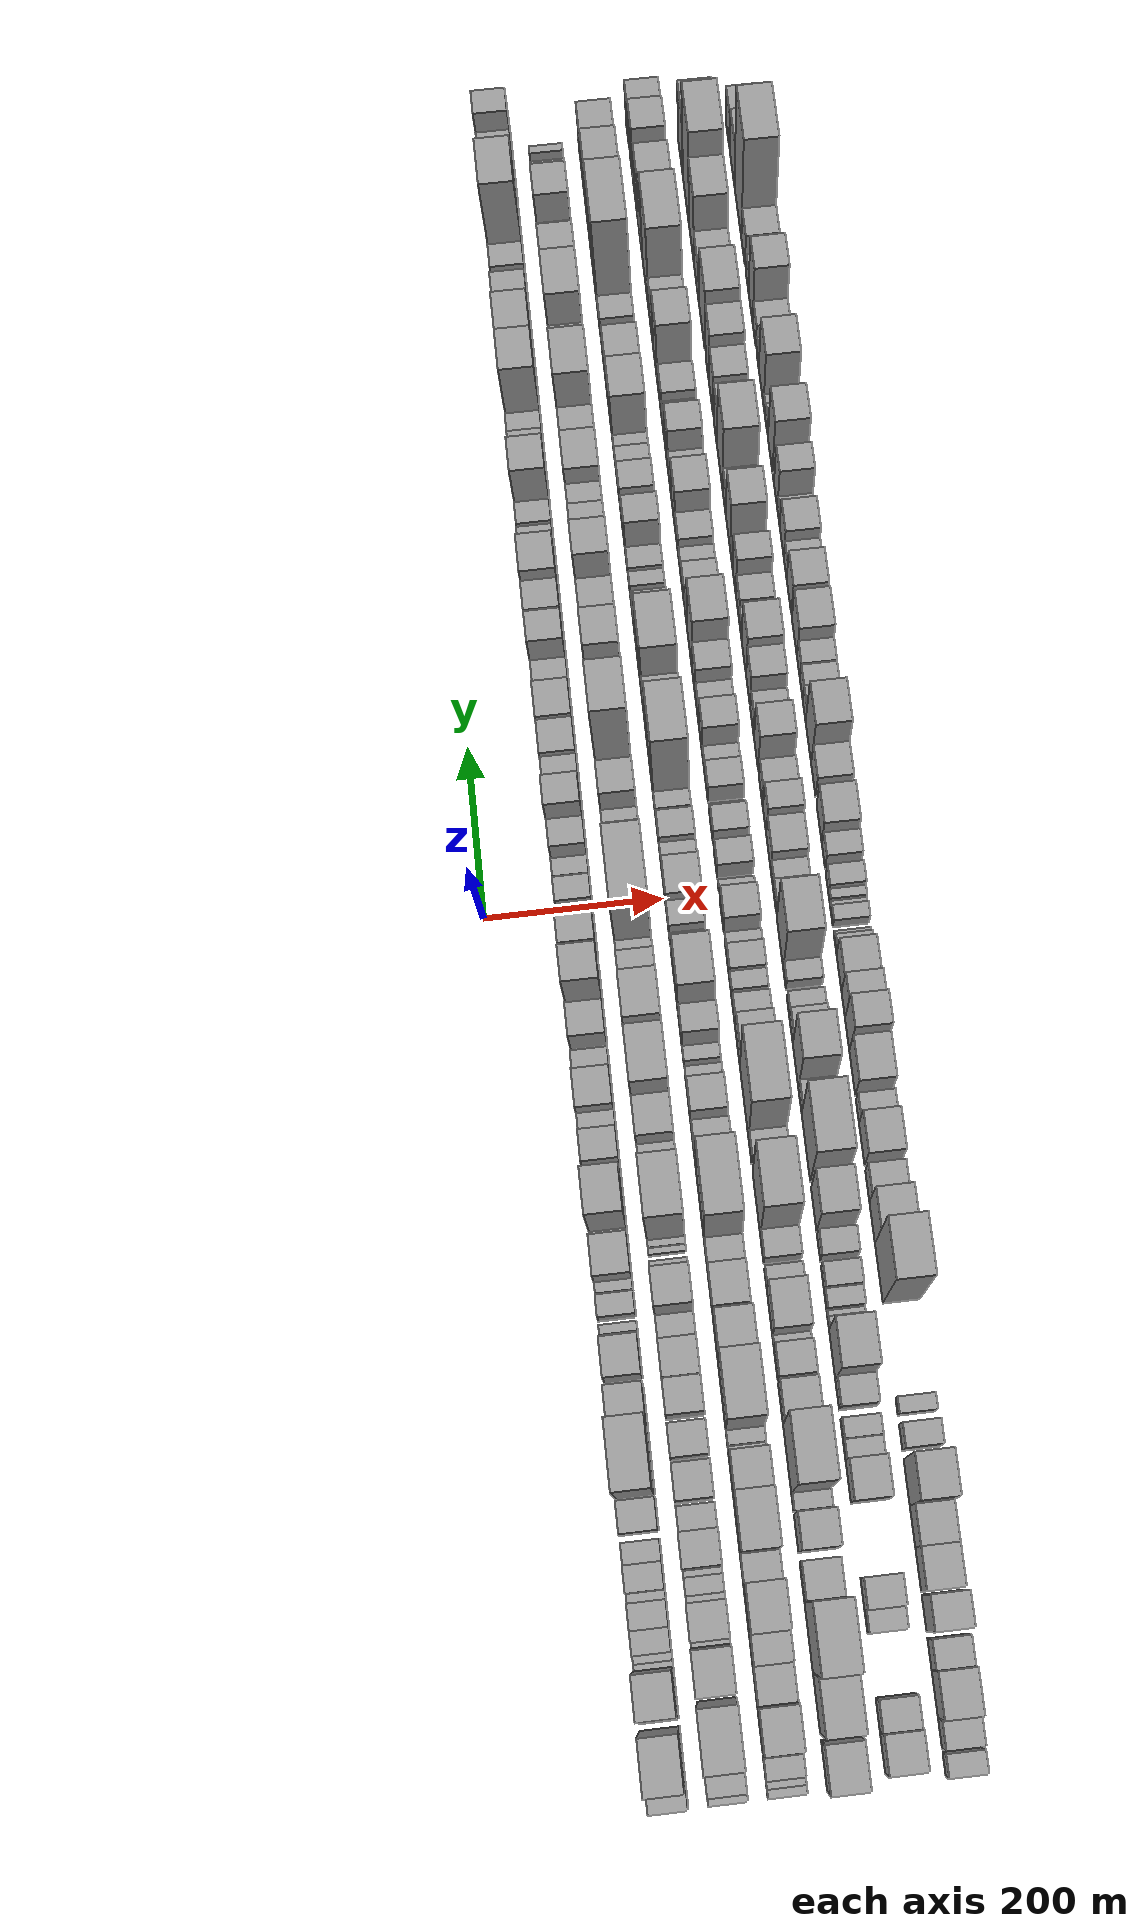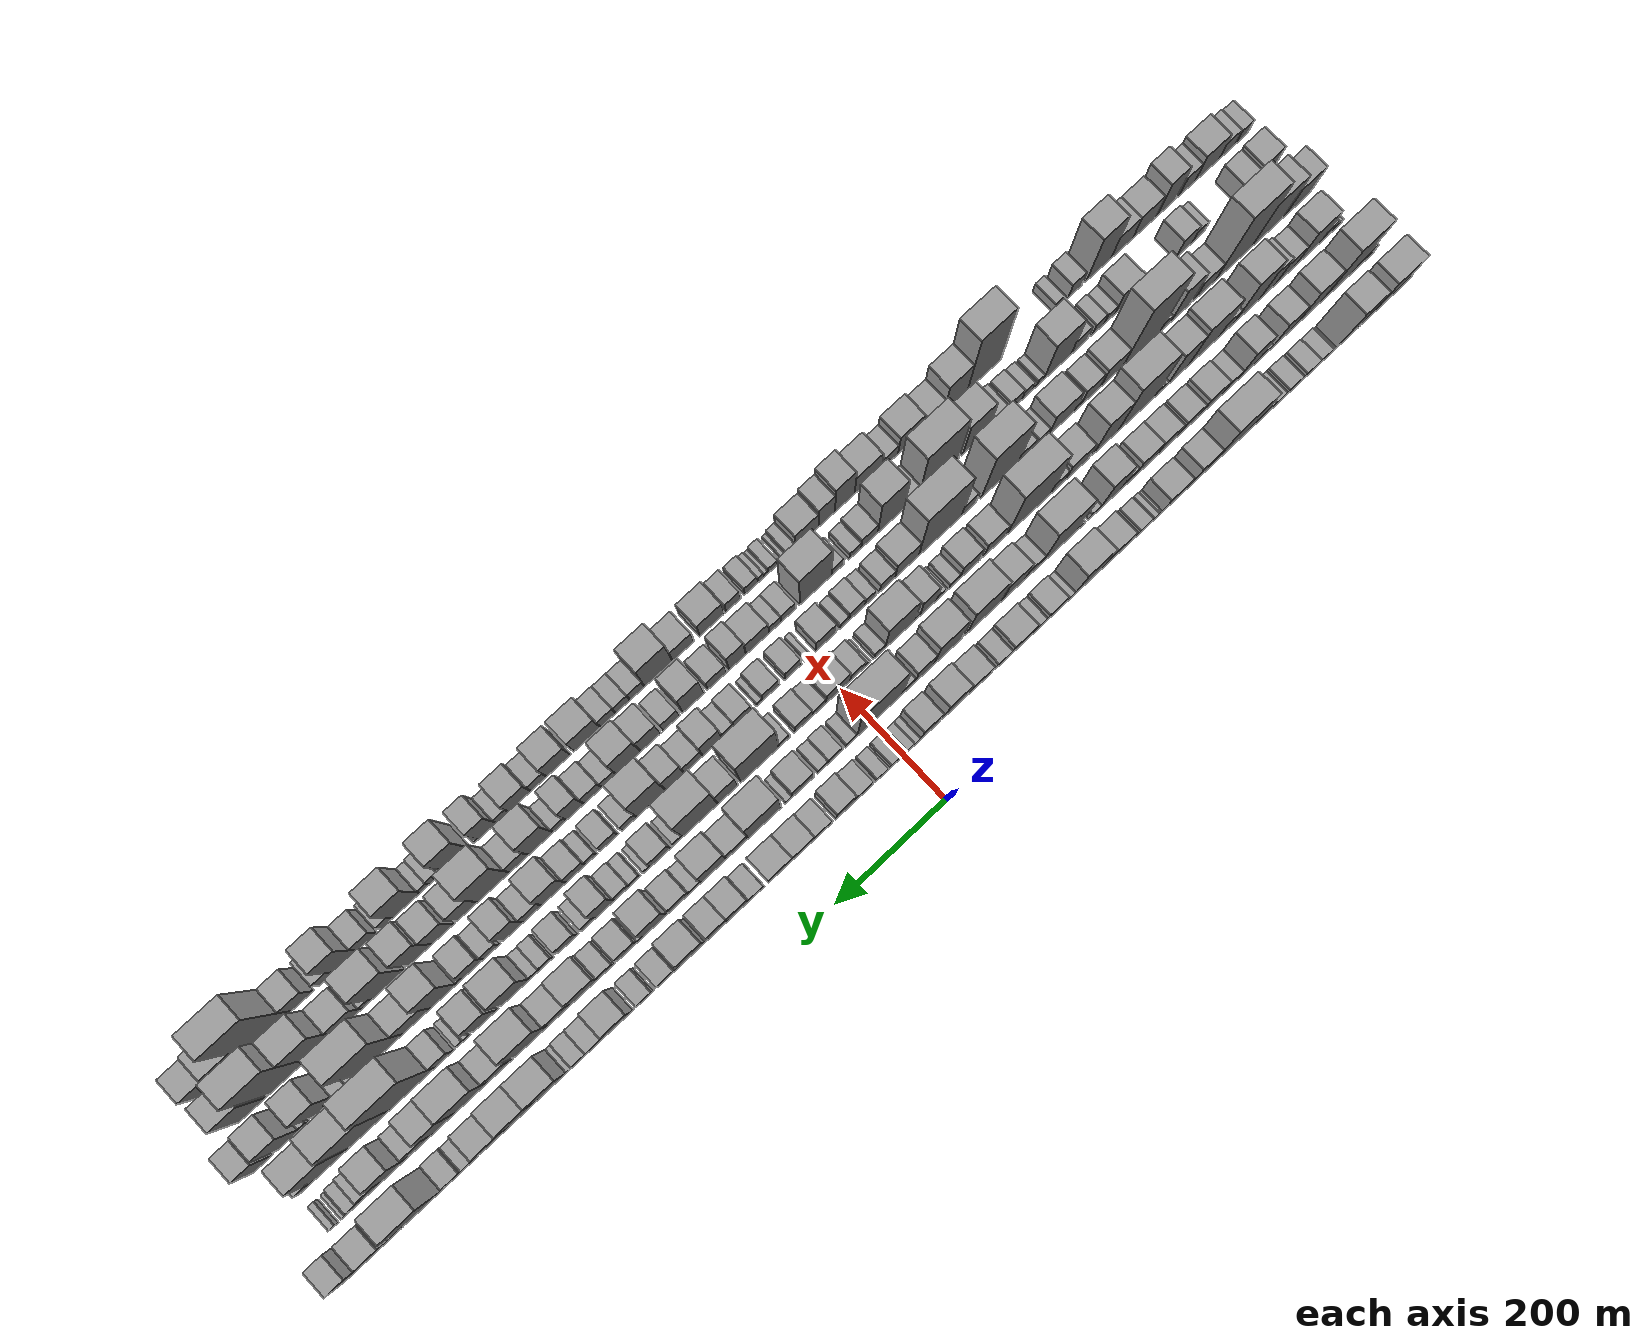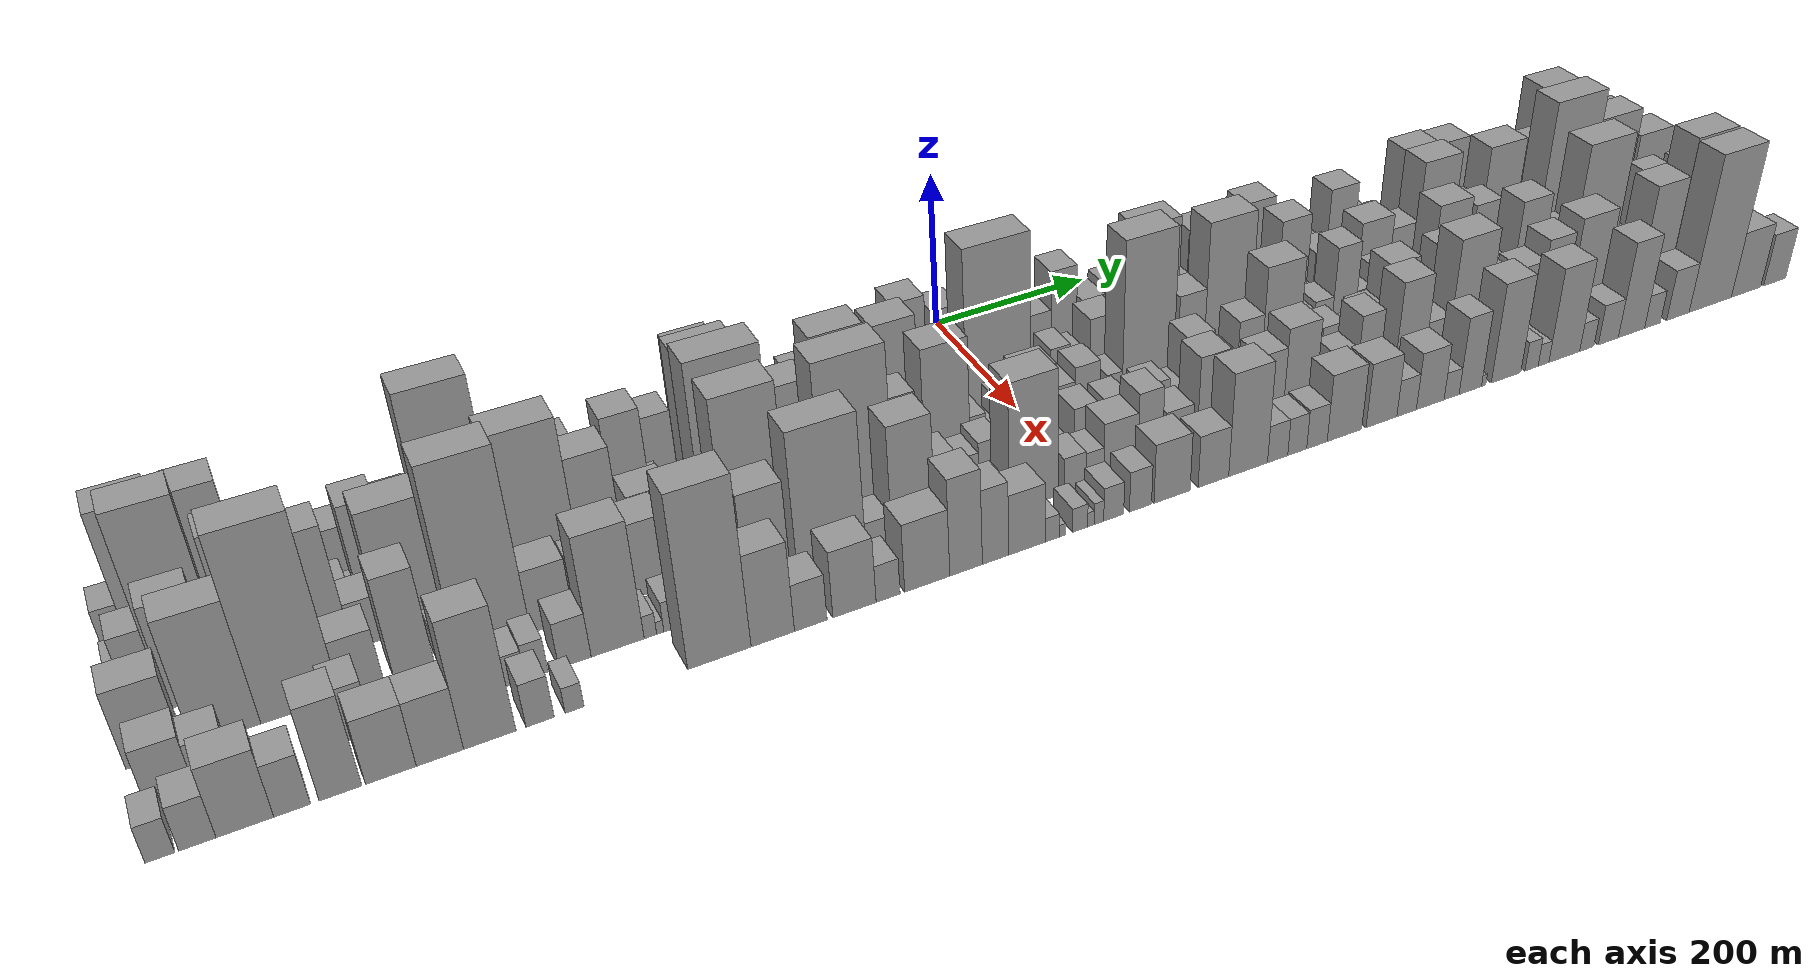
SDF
<sdf version="1.6">
 <world name="default">
  <scene>
   <sky><clouds><speed>12</speed></clouds></sky>
   <ambient>0.4 0.4 0.4 1</ambient>
   <background>0.7 0.7 0.7 1</background>
   <shadows>1</shadows>
  </scene>
  <gravity>0 0 -9.8066</gravity>
  <magnetic_field>6e-06 2.3e-05 -4.2e-05</magnetic_field>
  <physics default="0" name="default_physics" type="ode">
   <ode>
    <solver>
     <type>quick</type>
     <iters>10</iters>
     <sor>1.0</sor>
     <use_dynamic_moi_rescaling>0</use_dynamic_moi_rescaling>
    </solver>
    <constraints>
     <cfm>0</cfm>
     <erp>0.2</erp>
     <contact_max_correcting_vel>100</contact_max_correcting_vel>
     <contact_surface_layer>0.001</contact_surface_layer>
    </constraints>
   </ode>
   <max_step_size>0.004</max_step_size>
   <real_time_factor>1</real_time_factor>
   <real_time_update_rate>250</real_time_update_rate>
  </physics>
  <light name="sun" type="directional">
   <pose>0 0 10 0 0 0</pose>
   <diffuse>0.8 0.8 0.8 1</diffuse>
   <specular>0.2 0.2 0.2 1</specular>
   <attenuation>
    <range>1000</range>
    <constant>0.9</constant>
    <linear>0.01</linear>
    <quadratic>0.001</quadratic>
   </attenuation>
   <direction>-0.5 0.1 -0.9</direction>
  </light>
  <model name="building_1">
   <static>1</static>
   <pose>100.0000 -928.6294 0 0.000000 0.000000 0.000000</pose>
   <link name="link">
    <pose>0 0 21.00 0 0 0</pose>
    <collision name="collision"><geometry><box><size>40.0000 22.7412 42.0000</size></box></geometry></collision>
    <visual name="visual">
     <cast_shadows>0</cast_shadows>
     <geometry><box><size>40.0000 22.7412 42.0000</size></box></geometry>
     <material>
      <script>
       <uri>model://grey_wall/materials/scripts</uri>
       <uri>model://grey_wall/materials/textures</uri>
       <name>vrc/grey_wall</name>
      </script>
     </material>
    </visual>
   </link>
  </model>
  <model name="building_2">
   <static>1</static>
   <pose>100.0000 -889.6403 0 0.000000 0.000000 0.000000</pose>
   <link name="link">
    <pose>0 0 75.00 0 0 0</pose>
    <collision name="collision"><geometry><box><size>40.0000 55.2371 150.0000</size></box></geometry></collision>
    <visual name="visual">
     <cast_shadows>0</cast_shadows>
     <geometry><box><size>40.0000 55.2371 150.0000</size></box></geometry>
     <material>
      <script>
       <uri>model://grey_wall/materials/scripts</uri>
       <uri>model://grey_wall/materials/textures</uri>
       <name>vrc/grey_wall</name>
      </script>
     </material>
    </visual>
   </link>
  </model>
  <model name="building_3">
   <static>1</static>
   <pose>100.0000 -851.6356 0 0.000000 0.000000 0.000000</pose>
   <link name="link">
    <pose>0 0 7.50 0 0 0</pose>
    <collision name="collision"><geometry><box><size>40.0000 6.7722 15.0000</size></box></geometry></collision>
    <visual name="visual">
     <cast_shadows>0</cast_shadows>
     <geometry><box><size>40.0000 6.7722 15.0000</size></box></geometry>
     <material>
      <script>
       <uri>model://grey_wall/materials/scripts</uri>
       <uri>model://grey_wall/materials/textures</uri>
       <name>vrc/grey_wall</name>
      </script>
     </material>
    </visual>
   </link>
  </model>
  <model name="building_4">
   <static>1</static>
   <pose>100.0000 -826.1524 0 0.000000 0.000000 0.000000</pose>
   <link name="link">
    <pose>0 0 73.50 0 0 0</pose>
    <collision name="collision"><geometry><box><size>40.0000 44.1944 147.0000</size></box></geometry></collision>
    <visual name="visual">
     <cast_shadows>0</cast_shadows>
     <geometry><box><size>40.0000 44.1944 147.0000</size></box></geometry>
     <material>
      <script>
       <uri>model://grey_wall/materials/scripts</uri>
       <uri>model://grey_wall/materials/textures</uri>
       <name>vrc/grey_wall</name>
      </script>
     </material>
    </visual>
   </link>
  </model>
  <model name="building_5">
   <static>1</static>
   <pose>100.0000 -800.8621 0 0.000000 0.000000 0.000000</pose>
   <link name="link">
    <pose>0 0 7.50 0 0 0</pose>
    <collision name="collision"><geometry><box><size>40.0000 6.3861 15.0000</size></box></geometry></collision>
    <visual name="visual">
     <cast_shadows>0</cast_shadows>
     <geometry><box><size>40.0000 6.3861 15.0000</size></box></geometry>
     <material>
      <script>
       <uri>model://grey_wall/materials/scripts</uri>
       <uri>model://grey_wall/materials/textures</uri>
       <name>vrc/grey_wall</name>
      </script>
     </material>
    </visual>
   </link>
  </model>
  <model name="building_6">
   <static>1</static>
   <pose>100.0000 -793.3792 0 0.000000 0.000000 0.000000</pose>
   <link name="link">
    <pose>0 0 9.00 0 0 0</pose>
    <collision name="collision"><geometry><box><size>40.0000 8.5798 18.0000</size></box></geometry></collision>
    <visual name="visual">
     <cast_shadows>0</cast_shadows>
     <geometry><box><size>40.0000 8.5798 18.0000</size></box></geometry>
     <material>
      <script>
       <uri>model://grey_wall/materials/scripts</uri>
       <uri>model://grey_wall/materials/textures</uri>
       <name>vrc/grey_wall</name>
      </script>
     </material>
    </visual>
   </link>
  </model>
  <model name="building_7">
   <static>1</static>
   <pose>100.0000 -776.9503 0 0.000000 0.000000 0.000000</pose>
   <link name="link">
    <pose>0 0 21.00 0 0 0</pose>
    <collision name="collision"><geometry><box><size>40.0000 24.2779 42.0000</size></box></geometry></collision>
    <visual name="visual">
     <cast_shadows>0</cast_shadows>
     <geometry><box><size>40.0000 24.2779 42.0000</size></box></geometry>
     <material>
      <script>
       <uri>model://grey_wall/materials/scripts</uri>
       <uri>model://grey_wall/materials/textures</uri>
       <name>vrc/grey_wall</name>
      </script>
     </material>
    </visual>
   </link>
  </model>
  <model name="building_8">
   <static>1</static>
   <pose>100.0000 -751.3723 0 0.000000 0.000000 0.000000</pose>
   <link name="link">
    <pose>0 0 22.50 0 0 0</pose>
    <collision name="collision"><geometry><box><size>40.0000 26.8782 45.0000</size></box></geometry></collision>
    <visual name="visual">
     <cast_shadows>0</cast_shadows>
     <geometry><box><size>40.0000 26.8782 45.0000</size></box></geometry>
     <material>
      <script>
       <uri>model://grey_wall/materials/scripts</uri>
       <uri>model://grey_wall/materials/textures</uri>
       <name>vrc/grey_wall</name>
      </script>
     </material>
    </visual>
   </link>
  </model>
  <model name="building_9">
   <static>1</static>
   <pose>100.0000 -733.1726 0 0.000000 0.000000 0.000000</pose>
   <link name="link">
    <pose>0 0 10.50 0 0 0</pose>
    <collision name="collision"><geometry><box><size>40.0000 9.5210 21.0000</size></box></geometry></collision>
    <visual name="visual">
     <cast_shadows>0</cast_shadows>
     <geometry><box><size>40.0000 9.5210 21.0000</size></box></geometry>
     <material>
      <script>
       <uri>model://grey_wall/materials/scripts</uri>
       <uri>model://grey_wall/materials/textures</uri>
       <name>vrc/grey_wall</name>
      </script>
     </material>
    </visual>
   </link>
  </model>
  <model name="building_10">
   <static>1</static>
   <pose>100.0000 -714.5691 0 0.000000 0.000000 0.000000</pose>
   <link name="link">
    <pose>0 0 27.00 0 0 0</pose>
    <collision name="collision"><geometry><box><size>40.0000 27.6860 54.0000</size></box></geometry></collision>
    <visual name="visual">
     <cast_shadows>0</cast_shadows>
     <geometry><box><size>40.0000 27.6860 54.0000</size></box></geometry>
     <material>
      <script>
       <uri>model://grey_wall/materials/scripts</uri>
       <uri>model://grey_wall/materials/textures</uri>
       <name>vrc/grey_wall</name>
      </script>
     </material>
    </visual>
   </link>
  </model>
  <model name="building_11">
   <static>1</static>
   <pose>100.0000 -689.6385 0 0.000000 0.000000 0.000000</pose>
   <link name="link">
    <pose>0 0 21.00 0 0 0</pose>
    <collision name="collision"><geometry><box><size>40.0000 22.1752 42.0000</size></box></geometry></collision>
    <visual name="visual">
     <cast_shadows>0</cast_shadows>
     <geometry><box><size>40.0000 22.1752 42.0000</size></box></geometry>
     <material>
      <script>
       <uri>model://grey_wall/materials/scripts</uri>
       <uri>model://grey_wall/materials/textures</uri>
       <name>vrc/grey_wall</name>
      </script>
     </material>
    </visual>
   </link>
  </model>
  <model name="building_12">
   <static>1</static>
   <pose>100.0000 -654.0368 0 0.000000 0.000000 0.000000</pose>
   <link name="link">
    <pose>0 0 33.00 0 0 0</pose>
    <collision name="collision"><geometry><box><size>40.0000 33.0283 66.0000</size></box></geometry></collision>
    <visual name="visual">
     <cast_shadows>0</cast_shadows>
     <geometry><box><size>40.0000 33.0283 66.0000</size></box></geometry>
     <material>
      <script>
       <uri>model://grey_wall/materials/scripts</uri>
       <uri>model://grey_wall/materials/textures</uri>
       <name>vrc/grey_wall</name>
      </script>
     </material>
    </visual>
   </link>
  </model>
  <model name="building_13">
   <static>1</static>
   <pose>100.0000 -598.4503 0 0.000000 0.000000 0.000000</pose>
   <link name="link">
    <pose>0 0 93.00 0 0 0</pose>
    <collision name="collision"><geometry><box><size>40.0000 72.1446 186.0000</size></box></geometry></collision>
    <visual name="visual">
     <cast_shadows>0</cast_shadows>
     <geometry><box><size>40.0000 72.1446 186.0000</size></box></geometry>
     <material>
      <script>
       <uri>model://grey_wall/materials/scripts</uri>
       <uri>model://grey_wall/materials/textures</uri>
       <name>vrc/grey_wall</name>
      </script>
     </material>
    </visual>
   </link>
  </model>
  <model name="building_14">
   <static>1</static>
   <pose>100.0000 -543.6036 0 0.000000 0.000000 0.000000</pose>
   <link name="link">
    <pose>0 0 51.00 0 0 0</pose>
    <collision name="collision"><geometry><box><size>40.0000 37.5488 102.0000</size></box></geometry></collision>
    <visual name="visual">
     <cast_shadows>0</cast_shadows>
     <geometry><box><size>40.0000 37.5488 102.0000</size></box></geometry>
     <material>
      <script>
       <uri>model://grey_wall/materials/scripts</uri>
       <uri>model://grey_wall/materials/textures</uri>
       <name>vrc/grey_wall</name>
      </script>
     </material>
    </visual>
   </link>
  </model>
  <model name="building_15">
   <static>1</static>
   <pose>100.0000 -494.8130 0 0.000000 0.000000 0.000000</pose>
   <link name="link">
    <pose>0 0 39.00 0 0 0</pose>
    <collision name="collision"><geometry><box><size>40.0000 42.0324 78.0000</size></box></geometry></collision>
    <visual name="visual">
     <cast_shadows>0</cast_shadows>
     <geometry><box><size>40.0000 42.0324 78.0000</size></box></geometry>
     <material>
      <script>
       <uri>model://grey_wall/materials/scripts</uri>
       <uri>model://grey_wall/materials/textures</uri>
       <name>vrc/grey_wall</name>
      </script>
     </material>
    </visual>
   </link>
  </model>
  <model name="building_16">
   <static>1</static>
   <pose>100.0000 -470.3629 0 0.000000 0.000000 0.000000</pose>
   <link name="link">
    <pose>0 0 7.50 0 0 0</pose>
    <collision name="collision"><geometry><box><size>40.0000 6.8678 15.0000</size></box></geometry></collision>
    <visual name="visual">
     <cast_shadows>0</cast_shadows>
     <geometry><box><size>40.0000 6.8678 15.0000</size></box></geometry>
     <material>
      <script>
       <uri>model://grey_wall/materials/scripts</uri>
       <uri>model://grey_wall/materials/textures</uri>
       <name>vrc/grey_wall</name>
      </script>
     </material>
    </visual>
   </link>
  </model>
  <model name="building_17">
   <static>1</static>
   <pose>100.0000 -461.8193 0 0.000000 0.000000 0.000000</pose>
   <link name="link">
    <pose>0 0 12.00 0 0 0</pose>
    <collision name="collision"><geometry><box><size>40.0000 10.2193 24.0000</size></box></geometry></collision>
    <visual name="visual">
     <cast_shadows>0</cast_shadows>
     <geometry><box><size>40.0000 10.2193 24.0000</size></box></geometry>
     <material>
      <script>
       <uri>model://grey_wall/materials/scripts</uri>
       <uri>model://grey_wall/materials/textures</uri>
       <name>vrc/grey_wall</name>
      </script>
     </material>
    </visual>
   </link>
  </model>
  <model name="building_18">
   <static>1</static>
   <pose>100.0000 -438.7839 0 0.000000 0.000000 0.000000</pose>
   <link name="link">
    <pose>0 0 21.00 0 0 0</pose>
    <collision name="collision"><geometry><box><size>40.0000 23.8515 42.0000</size></box></geometry></collision>
    <visual name="visual">
     <cast_shadows>0</cast_shadows>
     <geometry><box><size>40.0000 23.8515 42.0000</size></box></geometry>
     <material>
      <script>
       <uri>model://grey_wall/materials/scripts</uri>
       <uri>model://grey_wall/materials/textures</uri>
       <name>vrc/grey_wall</name>
      </script>
     </material>
    </visual>
   </link>
  </model>
  <model name="building_19">
   <static>1</static>
   <pose>100.0000 -417.9926 0 0.000000 0.000000 0.000000</pose>
   <link name="link">
    <pose>0 0 12.00 0 0 0</pose>
    <collision name="collision"><geometry><box><size>40.0000 11.7311 24.0000</size></box></geometry></collision>
    <visual name="visual">
     <cast_shadows>0</cast_shadows>
     <geometry><box><size>40.0000 11.7311 24.0000</size></box></geometry>
     <material>
      <script>
       <uri>model://grey_wall/materials/scripts</uri>
       <uri>model://grey_wall/materials/textures</uri>
       <name>vrc/grey_wall</name>
      </script>
     </material>
    </visual>
   </link>
  </model>
  <model name="building_20">
   <static>1</static>
   <pose>100.0000 -390.3677 0 0.000000 0.000000 0.000000</pose>
   <link name="link">
    <pose>0 0 37.50 0 0 0</pose>
    <collision name="collision"><geometry><box><size>40.0000 43.5187 75.0000</size></box></geometry></collision>
    <visual name="visual">
     <cast_shadows>0</cast_shadows>
     <geometry><box><size>40.0000 43.5187 75.0000</size></box></geometry>
     <material>
      <script>
       <uri>model://grey_wall/materials/scripts</uri>
       <uri>model://grey_wall/materials/textures</uri>
       <name>vrc/grey_wall</name>
      </script>
     </material>
    </visual>
   </link>
  </model>
  <model name="building_21">
   <static>1</static>
   <pose>100.0000 -363.5932 0 0.000000 0.000000 0.000000</pose>
   <link name="link">
    <pose>0 0 10.50 0 0 0</pose>
    <collision name="collision"><geometry><box><size>40.0000 10.0303 21.0000</size></box></geometry></collision>
    <visual name="visual">
     <cast_shadows>0</cast_shadows>
     <geometry><box><size>40.0000 10.0303 21.0000</size></box></geometry>
     <material>
      <script>
       <uri>model://grey_wall/materials/scripts</uri>
       <uri>model://grey_wall/materials/textures</uri>
       <name>vrc/grey_wall</name>
      </script>
     </material>
    </visual>
   </link>
  </model>
  <model name="building_22">
   <static>1</static>
   <pose>100.0000 -333.5558 0 0.000000 0.000000 0.000000</pose>
   <link name="link">
    <pose>0 0 72.00 0 0 0</pose>
    <collision name="collision"><geometry><box><size>40.0000 50.0446 144.0000</size></box></geometry></collision>
    <visual name="visual">
     <cast_shadows>0</cast_shadows>
     <geometry><box><size>40.0000 50.0446 144.0000</size></box></geometry>
     <material>
      <script>
       <uri>model://grey_wall/materials/scripts</uri>
       <uri>model://grey_wall/materials/textures</uri>
       <name>vrc/grey_wall</name>
      </script>
     </material>
    </visual>
   </link>
  </model>
  <model name="building_23">
   <static>1</static>
   <pose>100.0000 -299.5866 0 0.000000 0.000000 0.000000</pose>
   <link name="link">
    <pose>0 0 16.50 0 0 0</pose>
    <collision name="collision"><geometry><box><size>40.0000 17.8937 33.0000</size></box></geometry></collision>
    <visual name="visual">
     <cast_shadows>0</cast_shadows>
     <geometry><box><size>40.0000 17.8937 33.0000</size></box></geometry>
     <material>
      <script>
       <uri>model://grey_wall/materials/scripts</uri>
       <uri>model://grey_wall/materials/textures</uri>
       <name>vrc/grey_wall</name>
      </script>
     </material>
    </visual>
   </link>
  </model>
  <model name="building_24">
   <static>1</static>
   <pose>100.0000 -273.4221 0 0.000000 0.000000 0.000000</pose>
   <link name="link">
    <pose>0 0 33.00 0 0 0</pose>
    <collision name="collision"><geometry><box><size>40.0000 34.4352 66.0000</size></box></geometry></collision>
    <visual name="visual">
     <cast_shadows>0</cast_shadows>
     <geometry><box><size>40.0000 34.4352 66.0000</size></box></geometry>
     <material>
      <script>
       <uri>model://grey_wall/materials/scripts</uri>
       <uri>model://grey_wall/materials/textures</uri>
       <name>vrc/grey_wall</name>
      </script>
     </material>
    </visual>
   </link>
  </model>
  <model name="building_25">
   <static>1</static>
   <pose>100.0000 -245.4888 0 0.000000 0.000000 0.000000</pose>
   <link name="link">
    <pose>0 0 21.00 0 0 0</pose>
    <collision name="collision"><geometry><box><size>40.0000 21.4315 42.0000</size></box></geometry></collision>
    <visual name="visual">
     <cast_shadows>0</cast_shadows>
     <geometry><box><size>40.0000 21.4315 42.0000</size></box></geometry>
     <material>
      <script>
       <uri>model://grey_wall/materials/scripts</uri>
       <uri>model://grey_wall/materials/textures</uri>
       <name>vrc/grey_wall</name>
      </script>
     </material>
    </visual>
   </link>
  </model>
  <model name="building_26">
   <static>1</static>
   <pose>100.0000 -213.7672 0 0.000000 0.000000 0.000000</pose>
   <link name="link">
    <pose>0 0 37.50 0 0 0</pose>
    <collision name="collision"><geometry><box><size>40.0000 42.0117 75.0000</size></box></geometry></collision>
    <visual name="visual">
     <cast_shadows>0</cast_shadows>
     <geometry><box><size>40.0000 42.0117 75.0000</size></box></geometry>
     <material>
      <script>
       <uri>model://grey_wall/materials/scripts</uri>
       <uri>model://grey_wall/materials/textures</uri>
       <name>vrc/grey_wall</name>
      </script>
     </material>
    </visual>
   </link>
  </model>
  <model name="building_27">
   <static>1</static>
   <pose>100.0000 -179.8913 0 0.000000 0.000000 0.000000</pose>
   <link name="link">
    <pose>0 0 22.50 0 0 0</pose>
    <collision name="collision"><geometry><box><size>40.0000 25.7401 45.0000</size></box></geometry></collision>
    <visual name="visual">
     <cast_shadows>0</cast_shadows>
     <geometry><box><size>40.0000 25.7401 45.0000</size></box></geometry>
     <material>
      <script>
       <uri>model://grey_wall/materials/scripts</uri>
       <uri>model://grey_wall/materials/textures</uri>
       <name>vrc/grey_wall</name>
      </script>
     </material>
    </visual>
   </link>
  </model>
  <model name="building_28">
   <static>1</static>
   <pose>100.0000 -138.4479 0 0.000000 0.000000 0.000000</pose>
   <link name="link">
    <pose>0 0 34.50 0 0 0</pose>
    <collision name="collision"><geometry><box><size>40.0000 37.1466 69.0000</size></box></geometry></collision>
    <visual name="visual">
     <cast_shadows>0</cast_shadows>
     <geometry><box><size>40.0000 37.1466 69.0000</size></box></geometry>
     <material>
      <script>
       <uri>model://grey_wall/materials/scripts</uri>
       <uri>model://grey_wall/materials/textures</uri>
       <name>vrc/grey_wall</name>
      </script>
     </material>
    </visual>
   </link>
  </model>
  <model name="building_29">
   <static>1</static>
   <pose>100.0000 -90.7545 0 0.000000 0.000000 0.000000</pose>
   <link name="link">
    <pose>0 0 63.00 0 0 0</pose>
    <collision name="collision"><geometry><box><size>40.0000 40.2401 126.0000</size></box></geometry></collision>
    <visual name="visual">
     <cast_shadows>0</cast_shadows>
     <geometry><box><size>40.0000 40.2401 126.0000</size></box></geometry>
     <material>
      <script>
       <uri>model://grey_wall/materials/scripts</uri>
       <uri>model://grey_wall/materials/textures</uri>
       <name>vrc/grey_wall</name>
      </script>
     </material>
    </visual>
   </link>
  </model>
  <model name="building_30">
   <static>1</static>
   <pose>100.0000 -45.3814 0 0.000000 0.000000 0.000000</pose>
   <link name="link">
    <pose>0 0 51.00 0 0 0</pose>
    <collision name="collision"><geometry><box><size>40.0000 34.5061 102.0000</size></box></geometry></collision>
    <visual name="visual">
     <cast_shadows>0</cast_shadows>
     <geometry><box><size>40.0000 34.5061 102.0000</size></box></geometry>
     <material>
      <script>
       <uri>model://grey_wall/materials/scripts</uri>
       <uri>model://grey_wall/materials/textures</uri>
       <name>vrc/grey_wall</name>
      </script>
     </material>
    </visual>
   </link>
  </model>
  <model name="building_31">
   <static>1</static>
   <pose>100.0000 -22.7238 0 0.000000 0.000000 0.000000</pose>
   <link name="link">
    <pose>0 0 13.50 0 0 0</pose>
    <collision name="collision"><geometry><box><size>40.0000 10.8093 27.0000</size></box></geometry></collision>
    <visual name="visual">
     <cast_shadows>0</cast_shadows>
     <geometry><box><size>40.0000 10.8093 27.0000</size></box></geometry>
     <material>
      <script>
       <uri>model://grey_wall/materials/scripts</uri>
       <uri>model://grey_wall/materials/textures</uri>
       <name>vrc/grey_wall</name>
      </script>
     </material>
    </visual>
   </link>
  </model>
  <model name="building_32">
   <static>1</static>
   <pose>100.0000 -9.4196 0 0.000000 0.000000 0.000000</pose>
   <link name="link">
    <pose>0 0 15.00 0 0 0</pose>
    <collision name="collision"><geometry><box><size>40.0000 15.7991 30.0000</size></box></geometry></collision>
    <visual name="visual">
     <cast_shadows>0</cast_shadows>
     <geometry><box><size>40.0000 15.7991 30.0000</size></box></geometry>
     <material>
      <script>
       <uri>model://grey_wall/materials/scripts</uri>
       <uri>model://grey_wall/materials/textures</uri>
       <name>vrc/grey_wall</name>
      </script>
     </material>
    </visual>
   </link>
  </model>
  <model name="building_33">
   <static>1</static>
   <pose>100.0000 12.1515 0 0.000000 0.000000 0.000000</pose>
   <link name="link">
    <pose>0 0 24.00 0 0 0</pose>
    <collision name="collision"><geometry><box><size>40.0000 27.3430 48.0000</size></box></geometry></collision>
    <visual name="visual">
     <cast_shadows>0</cast_shadows>
     <geometry><box><size>40.0000 27.3430 48.0000</size></box></geometry>
     <material>
      <script>
       <uri>model://grey_wall/materials/scripts</uri>
       <uri>model://grey_wall/materials/textures</uri>
       <name>vrc/grey_wall</name>
      </script>
     </material>
    </visual>
   </link>
  </model>
  <model name="building_34">
   <static>1</static>
   <pose>100.0000 40.2067 0 0.000000 0.000000 0.000000</pose>
   <link name="link">
    <pose>0 0 18.00 0 0 0</pose>
    <collision name="collision"><geometry><box><size>40.0000 20.7675 36.0000</size></box></geometry></collision>
    <visual name="visual">
     <cast_shadows>0</cast_shadows>
     <geometry><box><size>40.0000 20.7675 36.0000</size></box></geometry>
     <material>
      <script>
       <uri>model://grey_wall/materials/scripts</uri>
       <uri>model://grey_wall/materials/textures</uri>
       <name>vrc/grey_wall</name>
      </script>
     </material>
    </visual>
   </link>
  </model>
  <model name="building_35">
   <static>1</static>
   <pose>100.0000 73.3706 0 0.000000 0.000000 0.000000</pose>
   <link name="link">
    <pose>0 0 28.50 0 0 0</pose>
    <collision name="collision"><geometry><box><size>40.0000 31.5603 57.0000</size></box></geometry></collision>
    <visual name="visual">
     <cast_shadows>0</cast_shadows>
     <geometry><box><size>40.0000 31.5603 57.0000</size></box></geometry>
     <material>
      <script>
       <uri>model://grey_wall/materials/scripts</uri>
       <uri>model://grey_wall/materials/textures</uri>
       <name>vrc/grey_wall</name>
      </script>
     </material>
    </visual>
   </link>
  </model>
  <model name="building_36">
   <static>1</static>
   <pose>100.0000 106.2150 0 0.000000 0.000000 0.000000</pose>
   <link name="link">
    <pose>0 0 54.00 0 0 0</pose>
    <collision name="collision"><geometry><box><size>40.0000 34.1284 108.0000</size></box></geometry></collision>
    <visual name="visual">
     <cast_shadows>0</cast_shadows>
     <geometry><box><size>40.0000 34.1284 108.0000</size></box></geometry>
     <material>
      <script>
       <uri>model://grey_wall/materials/scripts</uri>
       <uri>model://grey_wall/materials/textures</uri>
       <name>vrc/grey_wall</name>
      </script>
     </material>
    </visual>
   </link>
  </model>
  <model name="building_37">
   <static>1</static>
   <pose>100.0000 145.7247 0 0.000000 0.000000 0.000000</pose>
   <link name="link">
    <pose>0 0 28.50 0 0 0</pose>
    <collision name="collision"><geometry><box><size>40.0000 30.8910 57.0000</size></box></geometry></collision>
    <visual name="visual">
     <cast_shadows>0</cast_shadows>
     <geometry><box><size>40.0000 30.8910 57.0000</size></box></geometry>
     <material>
      <script>
       <uri>model://grey_wall/materials/scripts</uri>
       <uri>model://grey_wall/materials/textures</uri>
       <name>vrc/grey_wall</name>
      </script>
     </material>
    </visual>
   </link>
  </model>
  <model name="building_38">
   <static>1</static>
   <pose>100.0000 180.6867 0 0.000000 0.000000 0.000000</pose>
   <link name="link">
    <pose>0 0 34.50 0 0 0</pose>
    <collision name="collision"><geometry><box><size>40.0000 39.0329 69.0000</size></box></geometry></collision>
    <visual name="visual">
     <cast_shadows>0</cast_shadows>
     <geometry><box><size>40.0000 39.0329 69.0000</size></box></geometry>
     <material>
      <script>
       <uri>model://grey_wall/materials/scripts</uri>
       <uri>model://grey_wall/materials/textures</uri>
       <name>vrc/grey_wall</name>
      </script>
     </material>
    </visual>
   </link>
  </model>
  <model name="building_39">
   <static>1</static>
   <pose>100.0000 221.3806 0 0.000000 0.000000 0.000000</pose>
   <link name="link">
    <pose>0 0 39.00 0 0 0</pose>
    <collision name="collision"><geometry><box><size>40.0000 42.3551 78.0000</size></box></geometry></collision>
    <visual name="visual">
     <cast_shadows>0</cast_shadows>
     <geometry><box><size>40.0000 42.3551 78.0000</size></box></geometry>
     <material>
      <script>
       <uri>model://grey_wall/materials/scripts</uri>
       <uri>model://grey_wall/materials/textures</uri>
       <name>vrc/grey_wall</name>
      </script>
     </material>
    </visual>
   </link>
  </model>
  <model name="building_40">
   <static>1</static>
   <pose>100.0000 263.8271 0 0.000000 0.000000 0.000000</pose>
   <link name="link">
    <pose>0 0 25.50 0 0 0</pose>
    <collision name="collision"><geometry><box><size>40.0000 26.5379 51.0000</size></box></geometry></collision>
    <visual name="visual">
     <cast_shadows>0</cast_shadows>
     <geometry><box><size>40.0000 26.5379 51.0000</size></box></geometry>
     <material>
      <script>
       <uri>model://grey_wall/materials/scripts</uri>
       <uri>model://grey_wall/materials/textures</uri>
       <name>vrc/grey_wall</name>
      </script>
     </material>
    </visual>
   </link>
  </model>
  <model name="building_41">
   <static>1</static>
   <pose>100.0000 295.0917 0 0.000000 0.000000 0.000000</pose>
   <link name="link">
    <pose>0 0 54.00 0 0 0</pose>
    <collision name="collision"><geometry><box><size>40.0000 35.9911 108.0000</size></box></geometry></collision>
    <visual name="visual">
     <cast_shadows>0</cast_shadows>
     <geometry><box><size>40.0000 35.9911 108.0000</size></box></geometry>
     <material>
      <script>
       <uri>model://grey_wall/materials/scripts</uri>
       <uri>model://grey_wall/materials/textures</uri>
       <name>vrc/grey_wall</name>
      </script>
     </material>
    </visual>
   </link>
  </model>
  <model name="building_42">
   <static>1</static>
   <pose>100.0000 330.3395 0 0.000000 0.000000 0.000000</pose>
   <link name="link">
    <pose>0 0 55.50 0 0 0</pose>
    <collision name="collision"><geometry><box><size>40.0000 34.5045 111.0000</size></box></geometry></collision>
    <visual name="visual">
     <cast_shadows>0</cast_shadows>
     <geometry><box><size>40.0000 34.5045 111.0000</size></box></geometry>
     <material>
      <script>
       <uri>model://grey_wall/materials/scripts</uri>
       <uri>model://grey_wall/materials/textures</uri>
       <name>vrc/grey_wall</name>
      </script>
     </material>
    </visual>
   </link>
  </model>
  <model name="building_43">
   <static>1</static>
   <pose>100.0000 350.6911 0 0.000000 0.000000 0.000000</pose>
   <link name="link">
    <pose>0 0 7.50 0 0 0</pose>
    <collision name="collision"><geometry><box><size>40.0000 6.1987 15.0000</size></box></geometry></collision>
    <visual name="visual">
     <cast_shadows>0</cast_shadows>
     <geometry><box><size>40.0000 6.1987 15.0000</size></box></geometry>
     <material>
      <script>
       <uri>model://grey_wall/materials/scripts</uri>
       <uri>model://grey_wall/materials/textures</uri>
       <name>vrc/grey_wall</name>
      </script>
     </material>
    </visual>
   </link>
  </model>
  <model name="building_44">
   <static>1</static>
   <pose>100.0000 376.0655 0 0.000000 0.000000 0.000000</pose>
   <link name="link">
    <pose>0 0 61.50 0 0 0</pose>
    <collision name="collision"><geometry><box><size>40.0000 44.5501 123.0000</size></box></geometry></collision>
    <visual name="visual">
     <cast_shadows>0</cast_shadows>
     <geometry><box><size>40.0000 44.5501 123.0000</size></box></geometry>
     <material>
      <script>
       <uri>model://grey_wall/materials/scripts</uri>
       <uri>model://grey_wall/materials/textures</uri>
       <name>vrc/grey_wall</name>
      </script>
     </material>
    </visual>
   </link>
  </model>
  <model name="building_45">
   <static>1</static>
   <pose>100.0000 401.9519 0 0.000000 0.000000 0.000000</pose>
   <link name="link">
    <pose>0 0 9.00 0 0 0</pose>
    <collision name="collision"><geometry><box><size>40.0000 7.2227 18.0000</size></box></geometry></collision>
    <visual name="visual">
     <cast_shadows>0</cast_shadows>
     <geometry><box><size>40.0000 7.2227 18.0000</size></box></geometry>
     <material>
      <script>
       <uri>model://grey_wall/materials/scripts</uri>
       <uri>model://grey_wall/materials/textures</uri>
       <name>vrc/grey_wall</name>
      </script>
     </material>
    </visual>
   </link>
  </model>
  <model name="building_46">
   <static>1</static>
   <pose>100.0000 420.9281 0 0.000000 0.000000 0.000000</pose>
   <link name="link">
    <pose>0 0 28.50 0 0 0</pose>
    <collision name="collision"><geometry><box><size>40.0000 30.7296 57.0000</size></box></geometry></collision>
    <visual name="visual">
     <cast_shadows>0</cast_shadows>
     <geometry><box><size>40.0000 30.7296 57.0000</size></box></geometry>
     <material>
      <script>
       <uri>model://grey_wall/materials/scripts</uri>
       <uri>model://grey_wall/materials/textures</uri>
       <name>vrc/grey_wall</name>
      </script>
     </material>
    </visual>
   </link>
  </model>
  <model name="building_47">
   <static>1</static>
   <pose>100.0000 458.7642 0 0.000000 0.000000 0.000000</pose>
   <link name="link">
    <pose>0 0 22.50 0 0 0</pose>
    <collision name="collision"><geometry><box><size>40.0000 26.9426 45.0000</size></box></geometry></collision>
    <visual name="visual">
     <cast_shadows>0</cast_shadows>
     <geometry><box><size>40.0000 26.9426 45.0000</size></box></geometry>
     <material>
      <script>
       <uri>model://grey_wall/materials/scripts</uri>
       <uri>model://grey_wall/materials/textures</uri>
       <name>vrc/grey_wall</name>
      </script>
     </material>
    </visual>
   </link>
  </model>
  <model name="building_48">
   <static>1</static>
   <pose>100.0000 502.2088 0 0.000000 0.000000 0.000000</pose>
   <link name="link">
    <pose>0 0 54.00 0 0 0</pose>
    <collision name="collision"><geometry><box><size>40.0000 41.9466 108.0000</size></box></geometry></collision>
    <visual name="visual">
     <cast_shadows>0</cast_shadows>
     <geometry><box><size>40.0000 41.9466 108.0000</size></box></geometry>
     <material>
      <script>
       <uri>model://grey_wall/materials/scripts</uri>
       <uri>model://grey_wall/materials/textures</uri>
       <name>vrc/grey_wall</name>
      </script>
     </material>
    </visual>
   </link>
  </model>
  <model name="building_49">
   <static>1</static>
   <pose>100.0000 541.9943 0 0.000000 0.000000 0.000000</pose>
   <link name="link">
    <pose>0 0 27.00 0 0 0</pose>
    <collision name="collision"><geometry><box><size>40.0000 29.6243 54.0000</size></box></geometry></collision>
    <visual name="visual">
     <cast_shadows>0</cast_shadows>
     <geometry><box><size>40.0000 29.6243 54.0000</size></box></geometry>
     <material>
      <script>
       <uri>model://grey_wall/materials/scripts</uri>
       <uri>model://grey_wall/materials/textures</uri>
       <name>vrc/grey_wall</name>
      </script>
     </material>
    </visual>
   </link>
  </model>
  <model name="building_50">
   <static>1</static>
   <pose>100.0000 569.3878 0 0.000000 0.000000 0.000000</pose>
   <link name="link">
    <pose>0 0 24.00 0 0 0</pose>
    <collision name="collision"><geometry><box><size>40.0000 25.1628 48.0000</size></box></geometry></collision>
    <visual name="visual">
     <cast_shadows>0</cast_shadows>
     <geometry><box><size>40.0000 25.1628 48.0000</size></box></geometry>
     <material>
      <script>
       <uri>model://grey_wall/materials/scripts</uri>
       <uri>model://grey_wall/materials/textures</uri>
       <name>vrc/grey_wall</name>
      </script>
     </material>
    </visual>
   </link>
  </model>
  <model name="building_51">
   <static>1</static>
   <pose>100.0000 587.8766 0 0.000000 0.000000 0.000000</pose>
   <link name="link">
    <pose>0 0 12.00 0 0 0</pose>
    <collision name="collision"><geometry><box><size>40.0000 11.8147 24.0000</size></box></geometry></collision>
    <visual name="visual">
     <cast_shadows>0</cast_shadows>
     <geometry><box><size>40.0000 11.8147 24.0000</size></box></geometry>
     <material>
      <script>
       <uri>model://grey_wall/materials/scripts</uri>
       <uri>model://grey_wall/materials/textures</uri>
       <name>vrc/grey_wall</name>
      </script>
     </material>
    </visual>
   </link>
  </model>
  <model name="building_52">
   <static>1</static>
   <pose>100.0000 619.3461 0 0.000000 0.000000 0.000000</pose>
   <link name="link">
    <pose>0 0 66.00 0 0 0</pose>
    <collision name="collision"><geometry><box><size>40.0000 51.1244 132.0000</size></box></geometry></collision>
    <visual name="visual">
     <cast_shadows>0</cast_shadows>
     <geometry><box><size>40.0000 51.1244 132.0000</size></box></geometry>
     <material>
      <script>
       <uri>model://grey_wall/materials/scripts</uri>
       <uri>model://grey_wall/materials/textures</uri>
       <name>vrc/grey_wall</name>
      </script>
     </material>
    </visual>
   </link>
  </model>
  <model name="building_53">
   <static>1</static>
   <pose>100.0000 669.0104 0 0.000000 0.000000 0.000000</pose>
   <link name="link">
    <pose>0 0 64.50 0 0 0</pose>
    <collision name="collision"><geometry><box><size>40.0000 48.2042 129.0000</size></box></geometry></collision>
    <visual name="visual">
     <cast_shadows>0</cast_shadows>
     <geometry><box><size>40.0000 48.2042 129.0000</size></box></geometry>
     <material>
      <script>
       <uri>model://grey_wall/materials/scripts</uri>
       <uri>model://grey_wall/materials/textures</uri>
       <name>vrc/grey_wall</name>
      </script>
     </material>
    </visual>
   </link>
  </model>
  <model name="building_54">
   <static>1</static>
   <pose>100.0000 716.7406 0 0.000000 0.000000 0.000000</pose>
   <link name="link">
    <pose>0 0 45.00 0 0 0</pose>
    <collision name="collision"><geometry><box><size>40.0000 47.2561 90.0000</size></box></geometry></collision>
    <visual name="visual">
     <cast_shadows>0</cast_shadows>
     <geometry><box><size>40.0000 47.2561 90.0000</size></box></geometry>
     <material>
      <script>
       <uri>model://grey_wall/materials/scripts</uri>
       <uri>model://grey_wall/materials/textures</uri>
       <name>vrc/grey_wall</name>
      </script>
     </material>
    </visual>
   </link>
  </model>
  <model name="building_55">
   <static>1</static>
   <pose>100.0000 758.7014 0 0.000000 0.000000 0.000000</pose>
   <link name="link">
    <pose>0 0 19.50 0 0 0</pose>
    <collision name="collision"><geometry><box><size>40.0000 20.6656 39.0000</size></box></geometry></collision>
    <visual name="visual">
     <cast_shadows>0</cast_shadows>
     <geometry><box><size>40.0000 20.6656 39.0000</size></box></geometry>
     <material>
      <script>
       <uri>model://grey_wall/materials/scripts</uri>
       <uri>model://grey_wall/materials/textures</uri>
       <name>vrc/grey_wall</name>
      </script>
     </material>
    </visual>
   </link>
  </model>
  <model name="building_56">
   <static>1</static>
   <pose>100.0000 783.9269 0 0.000000 0.000000 0.000000</pose>
   <link name="link">
    <pose>0 0 25.50 0 0 0</pose>
    <collision name="collision"><geometry><box><size>40.0000 29.7854 51.0000</size></box></geometry></collision>
    <visual name="visual">
     <cast_shadows>0</cast_shadows>
     <geometry><box><size>40.0000 29.7854 51.0000</size></box></geometry>
     <material>
      <script>
       <uri>model://grey_wall/materials/scripts</uri>
       <uri>model://grey_wall/materials/textures</uri>
       <name>vrc/grey_wall</name>
      </script>
     </material>
    </visual>
   </link>
  </model>
  <model name="building_57">
   <static>1</static>
   <pose>100.0000 836.3452 0 0.000000 0.000000 0.000000</pose>
   <link name="link">
    <pose>0 0 84.00 0 0 0</pose>
    <collision name="collision"><geometry><box><size>40.0000 59.0511 168.0000</size></box></geometry></collision>
    <visual name="visual">
     <cast_shadows>0</cast_shadows>
     <geometry><box><size>40.0000 59.0511 168.0000</size></box></geometry>
     <material>
      <script>
       <uri>model://grey_wall/materials/scripts</uri>
       <uri>model://grey_wall/materials/textures</uri>
       <name>vrc/grey_wall</name>
      </script>
     </material>
    </visual>
   </link>
  </model>
  <model name="building_58">
   <static>1</static>
   <pose>100.0000 881.3237 0 0.000000 0.000000 0.000000</pose>
   <link name="link">
    <pose>0 0 12.00 0 0 0</pose>
    <collision name="collision"><geometry><box><size>40.0000 10.9061 24.0000</size></box></geometry></collision>
    <visual name="visual">
     <cast_shadows>0</cast_shadows>
     <geometry><box><size>40.0000 10.9061 24.0000</size></box></geometry>
     <material>
      <script>
       <uri>model://grey_wall/materials/scripts</uri>
       <uri>model://grey_wall/materials/textures</uri>
       <name>vrc/grey_wall</name>
      </script>
     </material>
    </visual>
   </link>
  </model>
  <model name="building_59">
   <static>1</static>
   <pose>100.0000 891.0435 0 0.000000 0.000000 0.000000</pose>
   <link name="link">
    <pose>0 0 10.50 0 0 0</pose>
    <collision name="collision"><geometry><box><size>40.0000 8.5335 21.0000</size></box></geometry></collision>
    <visual name="visual">
     <cast_shadows>0</cast_shadows>
     <geometry><box><size>40.0000 8.5335 21.0000</size></box></geometry>
     <material>
      <script>
       <uri>model://grey_wall/materials/scripts</uri>
       <uri>model://grey_wall/materials/textures</uri>
       <name>vrc/grey_wall</name>
      </script>
     </material>
    </visual>
   </link>
  </model>
  <model name="building_60">
   <static>1</static>
   <pose>100.0000 917.4836 0 0.000000 0.000000 0.000000</pose>
   <link name="link">
    <pose>0 0 34.50 0 0 0</pose>
    <collision name="collision"><geometry><box><size>40.0000 38.3465 69.0000</size></box></geometry></collision>
    <visual name="visual">
     <cast_shadows>0</cast_shadows>
     <geometry><box><size>40.0000 38.3465 69.0000</size></box></geometry>
     <material>
      <script>
       <uri>model://grey_wall/materials/scripts</uri>
       <uri>model://grey_wall/materials/textures</uri>
       <name>vrc/grey_wall</name>
      </script>
     </material>
    </visual>
   </link>
  </model>
  <model name="building_61">
   <static>1</static>
   <pose>100.0000 956.0121 0 0.000000 0.000000 0.000000</pose>
   <link name="link">
    <pose>0 0 51.00 0 0 0</pose>
    <collision name="collision"><geometry><box><size>40.0000 30.7106 102.0000</size></box></geometry></collision>
    <visual name="visual">
     <cast_shadows>0</cast_shadows>
     <geometry><box><size>40.0000 30.7106 102.0000</size></box></geometry>
     <material>
      <script>
       <uri>model://grey_wall/materials/scripts</uri>
       <uri>model://grey_wall/materials/textures</uri>
       <name>vrc/grey_wall</name>
      </script>
     </material>
    </visual>
   </link>
  </model>
  <model name="building_62">
   <static>1</static>
   <pose>160.0000 -935.3581 0 0.000000 0.000000 0.000000</pose>
   <link name="link">
    <pose>0 0 10.50 0 0 0</pose>
    <collision name="collision"><geometry><box><size>40.0000 9.2838 21.0000</size></box></geometry></collision>
    <visual name="visual">
     <cast_shadows>0</cast_shadows>
     <geometry><box><size>40.0000 9.2838 21.0000</size></box></geometry>
     <material>
      <script>
       <uri>model://grey_wall/materials/scripts</uri>
       <uri>model://grey_wall/materials/textures</uri>
       <name>vrc/grey_wall</name>
      </script>
     </material>
    </visual>
   </link>
  </model>
  <model name="building_63">
   <static>1</static>
   <pose>160.0000 -916.2268 0 0.000000 0.000000 0.000000</pose>
   <link name="link">
    <pose>0 0 25.50 0 0 0</pose>
    <collision name="collision"><geometry><box><size>40.0000 28.9789 51.0000</size></box></geometry></collision>
    <visual name="visual">
     <cast_shadows>0</cast_shadows>
     <geometry><box><size>40.0000 28.9789 51.0000</size></box></geometry>
     <material>
      <script>
       <uri>model://grey_wall/materials/scripts</uri>
       <uri>model://grey_wall/materials/textures</uri>
       <name>vrc/grey_wall</name>
      </script>
     </material>
    </visual>
   </link>
  </model>
  <model name="building_64">
   <static>1</static>
   <pose>160.0000 -871.2117 0 0.000000 0.000000 0.000000</pose>
   <link name="link">
    <pose>0 0 93.00 0 0 0</pose>
    <collision name="collision"><geometry><box><size>40.0000 61.0512 186.0000</size></box></geometry></collision>
    <visual name="visual">
     <cast_shadows>0</cast_shadows>
     <geometry><box><size>40.0000 61.0512 186.0000</size></box></geometry>
     <material>
      <script>
       <uri>model://grey_wall/materials/scripts</uri>
       <uri>model://grey_wall/materials/textures</uri>
       <name>vrc/grey_wall</name>
      </script>
     </material>
    </visual>
   </link>
  </model>
  <model name="building_65">
   <static>1</static>
   <pose>160.0000 -811.0714 0 0.000000 0.000000 0.000000</pose>
   <link name="link">
    <pose>0 0 66.00 0 0 0</pose>
    <collision name="collision"><geometry><box><size>40.0000 45.2295 132.0000</size></box></geometry></collision>
    <visual name="visual">
     <cast_shadows>0</cast_shadows>
     <geometry><box><size>40.0000 45.2295 132.0000</size></box></geometry>
     <material>
      <script>
       <uri>model://grey_wall/materials/scripts</uri>
       <uri>model://grey_wall/materials/textures</uri>
       <name>vrc/grey_wall</name>
      </script>
     </material>
    </visual>
   </link>
  </model>
  <model name="building_66">
   <static>1</static>
   <pose>160.0000 -785.3472 0 0.000000 0.000000 0.000000</pose>
   <link name="link">
    <pose>0 0 7.50 0 0 0</pose>
    <collision name="collision"><geometry><box><size>40.0000 6.2188 15.0000</size></box></geometry></collision>
    <visual name="visual">
     <cast_shadows>0</cast_shadows>
     <geometry><box><size>40.0000 6.2188 15.0000</size></box></geometry>
     <material>
      <script>
       <uri>model://grey_wall/materials/scripts</uri>
       <uri>model://grey_wall/materials/textures</uri>
       <name>vrc/grey_wall</name>
      </script>
     </material>
    </visual>
   </link>
  </model>
  <model name="building_67">
   <static>1</static>
   <pose>160.0000 -763.3265 0 0.000000 0.000000 0.000000</pose>
   <link name="link">
    <pose>0 0 48.00 0 0 0</pose>
    <collision name="collision"><geometry><box><size>40.0000 37.8226 96.0000</size></box></geometry></collision>
    <visual name="visual">
     <cast_shadows>0</cast_shadows>
     <geometry><box><size>40.0000 37.8226 96.0000</size></box></geometry>
     <material>
      <script>
       <uri>model://grey_wall/materials/scripts</uri>
       <uri>model://grey_wall/materials/textures</uri>
       <name>vrc/grey_wall</name>
      </script>
     </material>
    </visual>
   </link>
  </model>
  <model name="building_68">
   <static>1</static>
   <pose>160.0000 -741.1229 0 0.000000 0.000000 0.000000</pose>
   <link name="link">
    <pose>0 0 7.50 0 0 0</pose>
    <collision name="collision"><geometry><box><size>40.0000 6.5846 15.0000</size></box></geometry></collision>
    <visual name="visual">
     <cast_shadows>0</cast_shadows>
     <geometry><box><size>40.0000 6.5846 15.0000</size></box></geometry>
     <material>
      <script>
       <uri>model://grey_wall/materials/scripts</uri>
       <uri>model://grey_wall/materials/textures</uri>
       <name>vrc/grey_wall</name>
      </script>
     </material>
    </visual>
   </link>
  </model>
  <model name="building_69">
   <static>1</static>
   <pose>160.0000 -728.6332 0 0.000000 0.000000 0.000000</pose>
   <link name="link">
    <pose>0 0 16.50 0 0 0</pose>
    <collision name="collision"><geometry><box><size>40.0000 18.3947 33.0000</size></box></geometry></collision>
    <visual name="visual">
     <cast_shadows>0</cast_shadows>
     <geometry><box><size>40.0000 18.3947 33.0000</size></box></geometry>
     <material>
      <script>
       <uri>model://grey_wall/materials/scripts</uri>
       <uri>model://grey_wall/materials/textures</uri>
       <name>vrc/grey_wall</name>
      </script>
     </material>
    </visual>
   </link>
  </model>
  <model name="building_70">
   <static>1</static>
   <pose>160.0000 -715.9429 0 0.000000 0.000000 0.000000</pose>
   <link name="link">
    <pose>0 0 7.50 0 0 0</pose>
    <collision name="collision"><geometry><box><size>40.0000 6.9858 15.0000</size></box></geometry></collision>
    <visual name="visual">
     <cast_shadows>0</cast_shadows>
     <geometry><box><size>40.0000 6.9858 15.0000</size></box></geometry>
     <material>
      <script>
       <uri>model://grey_wall/materials/scripts</uri>
       <uri>model://grey_wall/materials/textures</uri>
       <name>vrc/grey_wall</name>
      </script>
     </material>
    </visual>
   </link>
  </model>
  <model name="building_71">
   <static>1</static>
   <pose>160.0000 -694.3924 0 0.000000 0.000000 0.000000</pose>
   <link name="link">
    <pose>0 0 60.00 0 0 0</pose>
    <collision name="collision"><geometry><box><size>40.0000 36.1153 120.0000</size></box></geometry></collision>
    <visual name="visual">
     <cast_shadows>0</cast_shadows>
     <geometry><box><size>40.0000 36.1153 120.0000</size></box></geometry>
     <material>
      <script>
       <uri>model://grey_wall/materials/scripts</uri>
       <uri>model://grey_wall/materials/textures</uri>
       <name>vrc/grey_wall</name>
      </script>
     </material>
    </visual>
   </link>
  </model>
  <model name="building_72">
   <static>1</static>
   <pose>160.0000 -662.8366 0 0.000000 0.000000 0.000000</pose>
   <link name="link">
    <pose>0 0 25.50 0 0 0</pose>
    <collision name="collision"><geometry><box><size>40.0000 26.9964 51.0000</size></box></geometry></collision>
    <visual name="visual">
     <cast_shadows>0</cast_shadows>
     <geometry><box><size>40.0000 26.9964 51.0000</size></box></geometry>
     <material>
      <script>
       <uri>model://grey_wall/materials/scripts</uri>
       <uri>model://grey_wall/materials/textures</uri>
       <name>vrc/grey_wall</name>
      </script>
     </material>
    </visual>
   </link>
  </model>
  <model name="building_73">
   <static>1</static>
   <pose>160.0000 -626.2152 0 0.000000 0.000000 0.000000</pose>
   <link name="link">
    <pose>0 0 36.00 0 0 0</pose>
    <collision name="collision"><geometry><box><size>40.0000 38.2463 72.0000</size></box></geometry></collision>
    <visual name="visual">
     <cast_shadows>0</cast_shadows>
     <geometry><box><size>40.0000 38.2463 72.0000</size></box></geometry>
     <material>
      <script>
       <uri>model://grey_wall/materials/scripts</uri>
       <uri>model://grey_wall/materials/textures</uri>
       <name>vrc/grey_wall</name>
      </script>
     </material>
    </visual>
   </link>
  </model>
  <model name="building_74">
   <static>1</static>
   <pose>160.0000 -584.4956 0 0.000000 0.000000 0.000000</pose>
   <link name="link">
    <pose>0 0 33.00 0 0 0</pose>
    <collision name="collision"><geometry><box><size>40.0000 35.1929 66.0000</size></box></geometry></collision>
    <visual name="visual">
     <cast_shadows>0</cast_shadows>
     <geometry><box><size>40.0000 35.1929 66.0000</size></box></geometry>
     <material>
      <script>
       <uri>model://grey_wall/materials/scripts</uri>
       <uri>model://grey_wall/materials/textures</uri>
       <name>vrc/grey_wall</name>
      </script>
     </material>
    </visual>
   </link>
  </model>
  <model name="building_75">
   <static>1</static>
   <pose>160.0000 -540.9956 0 0.000000 0.000000 0.000000</pose>
   <link name="link">
    <pose>0 0 36.00 0 0 0</pose>
    <collision name="collision"><geometry><box><size>40.0000 37.8072 72.0000</size></box></geometry></collision>
    <visual name="visual">
     <cast_shadows>0</cast_shadows>
     <geometry><box><size>40.0000 37.8072 72.0000</size></box></geometry>
     <material>
      <script>
       <uri>model://grey_wall/materials/scripts</uri>
       <uri>model://grey_wall/materials/textures</uri>
       <name>vrc/grey_wall</name>
      </script>
     </material>
    </visual>
   </link>
  </model>
  <model name="building_76">
   <static>1</static>
   <pose>160.0000 -502.1628 0 0.000000 0.000000 0.000000</pose>
   <link name="link">
    <pose>0 0 37.50 0 0 0</pose>
    <collision name="collision"><geometry><box><size>40.0000 39.8583 75.0000</size></box></geometry></collision>
    <visual name="visual">
     <cast_shadows>0</cast_shadows>
     <geometry><box><size>40.0000 39.8583 75.0000</size></box></geometry>
     <material>
      <script>
       <uri>model://grey_wall/materials/scripts</uri>
       <uri>model://grey_wall/materials/textures</uri>
       <name>vrc/grey_wall</name>
      </script>
     </material>
    </visual>
   </link>
  </model>
  <model name="building_77">
   <static>1</static>
   <pose>160.0000 -469.2686 0 0.000000 0.000000 0.000000</pose>
   <link name="link">
    <pose>0 0 25.50 0 0 0</pose>
    <collision name="collision"><geometry><box><size>40.0000 25.9301 51.0000</size></box></geometry></collision>
    <visual name="visual">
     <cast_shadows>0</cast_shadows>
     <geometry><box><size>40.0000 25.9301 51.0000</size></box></geometry>
     <material>
      <script>
       <uri>model://grey_wall/materials/scripts</uri>
       <uri>model://grey_wall/materials/textures</uri>
       <name>vrc/grey_wall</name>
      </script>
     </material>
    </visual>
   </link>
  </model>
  <model name="building_78">
   <static>1</static>
   <pose>160.0000 -435.9990 0 0.000000 0.000000 0.000000</pose>
   <link name="link">
    <pose>0 0 66.00 0 0 0</pose>
    <collision name="collision"><geometry><box><size>40.0000 40.6092 132.0000</size></box></geometry></collision>
    <visual name="visual">
     <cast_shadows>0</cast_shadows>
     <geometry><box><size>40.0000 40.6092 132.0000</size></box></geometry>
     <material>
      <script>
       <uri>model://grey_wall/materials/scripts</uri>
       <uri>model://grey_wall/materials/textures</uri>
       <name>vrc/grey_wall</name>
      </script>
     </material>
    </visual>
   </link>
  </model>
  <model name="building_79">
   <static>1</static>
   <pose>160.0000 -406.8675 0 0.000000 0.000000 0.000000</pose>
   <link name="link">
    <pose>0 0 16.50 0 0 0</pose>
    <collision name="collision"><geometry><box><size>40.0000 17.6538 33.0000</size></box></geometry></collision>
    <visual name="visual">
     <cast_shadows>0</cast_shadows>
     <geometry><box><size>40.0000 17.6538 33.0000</size></box></geometry>
     <material>
      <script>
       <uri>model://grey_wall/materials/scripts</uri>
       <uri>model://grey_wall/materials/textures</uri>
       <name>vrc/grey_wall</name>
      </script>
     </material>
    </visual>
   </link>
  </model>
  <model name="building_80">
   <static>1</static>
   <pose>160.0000 -385.4229 0 0.000000 0.000000 0.000000</pose>
   <link name="link">
    <pose>0 0 7.50 0 0 0</pose>
    <collision name="collision"><geometry><box><size>40.0000 7.2354 15.0000</size></box></geometry></collision>
    <visual name="visual">
     <cast_shadows>0</cast_shadows>
     <geometry><box><size>40.0000 7.2354 15.0000</size></box></geometry>
     <material>
      <script>
       <uri>model://grey_wall/materials/scripts</uri>
       <uri>model://grey_wall/materials/textures</uri>
       <name>vrc/grey_wall</name>
      </script>
     </material>
    </visual>
   </link>
  </model>
  <model name="building_81">
   <static>1</static>
   <pose>160.0000 -377.8117 0 0.000000 0.000000 0.000000</pose>
   <link name="link">
    <pose>0 0 9.00 0 0 0</pose>
    <collision name="collision"><geometry><box><size>40.0000 7.9869 18.0000</size></box></geometry></collision>
    <visual name="visual">
     <cast_shadows>0</cast_shadows>
     <geometry><box><size>40.0000 7.9869 18.0000</size></box></geometry>
     <material>
      <script>
       <uri>model://grey_wall/materials/scripts</uri>
       <uri>model://grey_wall/materials/textures</uri>
       <name>vrc/grey_wall</name>
      </script>
     </material>
    </visual>
   </link>
  </model>
  <model name="building_82">
   <static>1</static>
   <pose>160.0000 -341.2182 0 0.000000 0.000000 0.000000</pose>
   <link name="link">
    <pose>0 0 90.00 0 0 0</pose>
    <collision name="collision"><geometry><box><size>40.0000 65.2001 180.0000</size></box></geometry></collision>
    <visual name="visual">
     <cast_shadows>0</cast_shadows>
     <geometry><box><size>40.0000 65.2001 180.0000</size></box></geometry>
     <material>
      <script>
       <uri>model://grey_wall/materials/scripts</uri>
       <uri>model://grey_wall/materials/textures</uri>
       <name>vrc/grey_wall</name>
      </script>
     </material>
    </visual>
   </link>
  </model>
  <model name="building_83">
   <static>1</static>
   <pose>160.0000 -293.2562 0 0.000000 0.000000 0.000000</pose>
   <link name="link">
    <pose>0 0 28.50 0 0 0</pose>
    <collision name="collision"><geometry><box><size>40.0000 30.7239 57.0000</size></box></geometry></collision>
    <visual name="visual">
     <cast_shadows>0</cast_shadows>
     <geometry><box><size>40.0000 30.7239 57.0000</size></box></geometry>
     <material>
      <script>
       <uri>model://grey_wall/materials/scripts</uri>
       <uri>model://grey_wall/materials/textures</uri>
       <name>vrc/grey_wall</name>
      </script>
     </material>
    </visual>
   </link>
  </model>
  <model name="building_84">
   <static>1</static>
   <pose>160.0000 -256.4339 0 0.000000 0.000000 0.000000</pose>
   <link name="link">
    <pose>0 0 54.00 0 0 0</pose>
    <collision name="collision"><geometry><box><size>40.0000 42.9209 108.0000</size></box></geometry></collision>
    <visual name="visual">
     <cast_shadows>0</cast_shadows>
     <geometry><box><size>40.0000 42.9209 108.0000</size></box></geometry>
     <material>
      <script>
       <uri>model://grey_wall/materials/scripts</uri>
       <uri>model://grey_wall/materials/textures</uri>
       <name>vrc/grey_wall</name>
      </script>
     </material>
    </visual>
   </link>
  </model>
  <model name="building_85">
   <static>1</static>
   <pose>160.0000 -200.3898 0 0.000000 0.000000 0.000000</pose>
   <link name="link">
    <pose>0 0 78.00 0 0 0</pose>
    <collision name="collision"><geometry><box><size>40.0000 61.1672 156.0000</size></box></geometry></collision>
    <visual name="visual">
     <cast_shadows>0</cast_shadows>
     <geometry><box><size>40.0000 61.1672 156.0000</size></box></geometry>
     <material>
      <script>
       <uri>model://grey_wall/materials/scripts</uri>
       <uri>model://grey_wall/materials/textures</uri>
       <name>vrc/grey_wall</name>
      </script>
     </material>
    </visual>
   </link>
  </model>
  <model name="building_86">
   <static>1</static>
   <pose>160.0000 -135.2525 0 0.000000 0.000000 0.000000</pose>
   <link name="link">
    <pose>0 0 73.50 0 0 0</pose>
    <collision name="collision"><geometry><box><size>40.0000 51.1075 147.0000</size></box></geometry></collision>
    <visual name="visual">
     <cast_shadows>0</cast_shadows>
     <geometry><box><size>40.0000 51.1075 147.0000</size></box></geometry>
     <material>
      <script>
       <uri>model://grey_wall/materials/scripts</uri>
       <uri>model://grey_wall/materials/textures</uri>
       <name>vrc/grey_wall</name>
      </script>
     </material>
    </visual>
   </link>
  </model>
  <model name="building_87">
   <static>1</static>
   <pose>160.0000 -92.5547 0 0.000000 0.000000 0.000000</pose>
   <link name="link">
    <pose>0 0 46.50 0 0 0</pose>
    <collision name="collision"><geometry><box><size>40.0000 34.2880 93.0000</size></box></geometry></collision>
    <visual name="visual">
     <cast_shadows>0</cast_shadows>
     <geometry><box><size>40.0000 34.2880 93.0000</size></box></geometry>
     <material>
      <script>
       <uri>model://grey_wall/materials/scripts</uri>
       <uri>model://grey_wall/materials/textures</uri>
       <name>vrc/grey_wall</name>
      </script>
     </material>
    </visual>
   </link>
  </model>
  <model name="building_88">
   <static>1</static>
   <pose>160.0000 -63.7799 0 0.000000 0.000000 0.000000</pose>
   <link name="link">
    <pose>0 0 22.50 0 0 0</pose>
    <collision name="collision"><geometry><box><size>40.0000 23.2616 45.0000</size></box></geometry></collision>
    <visual name="visual">
     <cast_shadows>0</cast_shadows>
     <geometry><box><size>40.0000 23.2616 45.0000</size></box></geometry>
     <material>
      <script>
       <uri>model://grey_wall/materials/scripts</uri>
       <uri>model://grey_wall/materials/textures</uri>
       <name>vrc/grey_wall</name>
      </script>
     </material>
    </visual>
   </link>
  </model>
  <model name="building_89">
   <static>1</static>
   <pose>160.0000 -11.2617 0 0.000000 0.000000 0.000000</pose>
   <link name="link">
    <pose>0 0 105.00 0 0 0</pose>
    <collision name="collision"><geometry><box><size>40.0000 81.7748 210.0000</size></box></geometry></collision>
    <visual name="visual">
     <cast_shadows>0</cast_shadows>
     <geometry><box><size>40.0000 81.7748 210.0000</size></box></geometry>
     <material>
      <script>
       <uri>model://grey_wall/materials/scripts</uri>
       <uri>model://grey_wall/materials/textures</uri>
       <name>vrc/grey_wall</name>
      </script>
     </material>
    </visual>
   </link>
  </model>
  <model name="building_90">
   <static>1</static>
   <pose>160.0000 39.0484 0 0.000000 0.000000 0.000000</pose>
   <link name="link">
    <pose>0 0 16.50 0 0 0</pose>
    <collision name="collision"><geometry><box><size>40.0000 18.8454 33.0000</size></box></geometry></collision>
    <visual name="visual">
     <cast_shadows>0</cast_shadows>
     <geometry><box><size>40.0000 18.8454 33.0000</size></box></geometry>
     <material>
      <script>
       <uri>model://grey_wall/materials/scripts</uri>
       <uri>model://grey_wall/materials/textures</uri>
       <name>vrc/grey_wall</name>
      </script>
     </material>
    </visual>
   </link>
  </model>
  <model name="building_91">
   <static>1</static>
   <pose>160.0000 68.0757 0 0.000000 0.000000 0.000000</pose>
   <link name="link">
    <pose>0 0 24.00 0 0 0</pose>
    <collision name="collision"><geometry><box><size>40.0000 25.2090 48.0000</size></box></geometry></collision>
    <visual name="visual">
     <cast_shadows>0</cast_shadows>
     <geometry><box><size>40.0000 25.2090 48.0000</size></box></geometry>
     <material>
      <script>
       <uri>model://grey_wall/materials/scripts</uri>
       <uri>model://grey_wall/materials/textures</uri>
       <name>vrc/grey_wall</name>
      </script>
     </material>
    </visual>
   </link>
  </model>
  <model name="building_92">
   <static>1</static>
   <pose>160.0000 90.0440 0 0.000000 0.000000 0.000000</pose>
   <link name="link">
    <pose>0 0 18.00 0 0 0</pose>
    <collision name="collision"><geometry><box><size>40.0000 18.7275 36.0000</size></box></geometry></collision>
    <visual name="visual">
     <cast_shadows>0</cast_shadows>
     <geometry><box><size>40.0000 18.7275 36.0000</size></box></geometry>
     <material>
      <script>
       <uri>model://grey_wall/materials/scripts</uri>
       <uri>model://grey_wall/materials/textures</uri>
       <name>vrc/grey_wall</name>
      </script>
     </material>
    </visual>
   </link>
  </model>
  <model name="building_93">
   <static>1</static>
   <pose>160.0000 125.8068 0 0.000000 0.000000 0.000000</pose>
   <link name="link">
    <pose>0 0 36.00 0 0 0</pose>
    <collision name="collision"><geometry><box><size>40.0000 38.7981 72.0000</size></box></geometry></collision>
    <visual name="visual">
     <cast_shadows>0</cast_shadows>
     <geometry><box><size>40.0000 38.7981 72.0000</size></box></geometry>
     <material>
      <script>
       <uri>model://grey_wall/materials/scripts</uri>
       <uri>model://grey_wall/materials/textures</uri>
       <name>vrc/grey_wall</name>
      </script>
     </material>
    </visual>
   </link>
  </model>
  <model name="building_94">
   <static>1</static>
   <pose>160.0000 151.0889 0 0.000000 0.000000 0.000000</pose>
   <link name="link">
    <pose>0 0 12.00 0 0 0</pose>
    <collision name="collision"><geometry><box><size>40.0000 11.7660 24.0000</size></box></geometry></collision>
    <visual name="visual">
     <cast_shadows>0</cast_shadows>
     <geometry><box><size>40.0000 11.7660 24.0000</size></box></geometry>
     <material>
      <script>
       <uri>model://grey_wall/materials/scripts</uri>
       <uri>model://grey_wall/materials/textures</uri>
       <name>vrc/grey_wall</name>
      </script>
     </material>
    </visual>
   </link>
  </model>
  <model name="building_95">
   <static>1</static>
   <pose>160.0000 194.3535 0 0.000000 0.000000 0.000000</pose>
   <link name="link">
    <pose>0 0 87.00 0 0 0</pose>
    <collision name="collision"><geometry><box><size>40.0000 58.7632 174.0000</size></box></geometry></collision>
    <visual name="visual">
     <cast_shadows>0</cast_shadows>
     <geometry><box><size>40.0000 58.7632 174.0000</size></box></geometry>
     <material>
      <script>
       <uri>model://grey_wall/materials/scripts</uri>
       <uri>model://grey_wall/materials/textures</uri>
       <name>vrc/grey_wall</name>
      </script>
     </material>
    </visual>
   </link>
  </model>
  <model name="building_96">
   <static>1</static>
   <pose>160.0000 242.5137 0 0.000000 0.000000 0.000000</pose>
   <link name="link">
    <pose>0 0 33.00 0 0 0</pose>
    <collision name="collision"><geometry><box><size>40.0000 37.5573 66.0000</size></box></geometry></collision>
    <visual name="visual">
     <cast_shadows>0</cast_shadows>
     <geometry><box><size>40.0000 37.5573 66.0000</size></box></geometry>
     <material>
      <script>
       <uri>model://grey_wall/materials/scripts</uri>
       <uri>model://grey_wall/materials/textures</uri>
       <name>vrc/grey_wall</name>
      </script>
     </material>
    </visual>
   </link>
  </model>
  <model name="building_97">
   <static>1</static>
   <pose>160.0000 283.4881 0 0.000000 0.000000 0.000000</pose>
   <link name="link">
    <pose>0 0 60.00 0 0 0</pose>
    <collision name="collision"><geometry><box><size>40.0000 44.3914 120.0000</size></box></geometry></collision>
    <visual name="visual">
     <cast_shadows>0</cast_shadows>
     <geometry><box><size>40.0000 44.3914 120.0000</size></box></geometry>
     <material>
      <script>
       <uri>model://grey_wall/materials/scripts</uri>
       <uri>model://grey_wall/materials/textures</uri>
       <name>vrc/grey_wall</name>
      </script>
     </material>
    </visual>
   </link>
  </model>
  <model name="building_98">
   <static>1</static>
   <pose>160.0000 316.4869 0 0.000000 0.000000 0.000000</pose>
   <link name="link">
    <pose>0 0 19.50 0 0 0</pose>
    <collision name="collision"><geometry><box><size>40.0000 21.6061 39.0000</size></box></geometry></collision>
    <visual name="visual">
     <cast_shadows>0</cast_shadows>
     <geometry><box><size>40.0000 21.6061 39.0000</size></box></geometry>
     <material>
      <script>
       <uri>model://grey_wall/materials/scripts</uri>
       <uri>model://grey_wall/materials/textures</uri>
       <name>vrc/grey_wall</name>
      </script>
     </material>
    </visual>
   </link>
  </model>
  <model name="building_99">
   <static>1</static>
   <pose>160.0000 344.7791 0 0.000000 0.000000 0.000000</pose>
   <link name="link">
    <pose>0 0 33.00 0 0 0</pose>
    <collision name="collision"><geometry><box><size>40.0000 34.9784 66.0000</size></box></geometry></collision>
    <visual name="visual">
     <cast_shadows>0</cast_shadows>
     <geometry><box><size>40.0000 34.9784 66.0000</size></box></geometry>
     <material>
      <script>
       <uri>model://grey_wall/materials/scripts</uri>
       <uri>model://grey_wall/materials/textures</uri>
       <name>vrc/grey_wall</name>
      </script>
     </material>
    </visual>
   </link>
  </model>
  <model name="building_100">
   <static>1</static>
   <pose>160.0000 386.2729 0 0.000000 0.000000 0.000000</pose>
   <link name="link">
    <pose>0 0 63.00 0 0 0</pose>
    <collision name="collision"><geometry><box><size>40.0000 42.0091 126.0000</size></box></geometry></collision>
    <visual name="visual">
     <cast_shadows>0</cast_shadows>
     <geometry><box><size>40.0000 42.0091 126.0000</size></box></geometry>
     <material>
      <script>
       <uri>model://grey_wall/materials/scripts</uri>
       <uri>model://grey_wall/materials/textures</uri>
       <name>vrc/grey_wall</name>
      </script>
     </material>
    </visual>
   </link>
  </model>
  <model name="building_101">
   <static>1</static>
   <pose>160.0000 412.4397 0 0.000000 0.000000 0.000000</pose>
   <link name="link">
    <pose>0 0 12.00 0 0 0</pose>
    <collision name="collision"><geometry><box><size>40.0000 10.3246 24.0000</size></box></geometry></collision>
    <visual name="visual">
     <cast_shadows>0</cast_shadows>
     <geometry><box><size>40.0000 10.3246 24.0000</size></box></geometry>
     <material>
      <script>
       <uri>model://grey_wall/materials/scripts</uri>
       <uri>model://grey_wall/materials/textures</uri>
       <name>vrc/grey_wall</name>
      </script>
     </material>
    </visual>
   </link>
  </model>
  <model name="building_102">
   <static>1</static>
   <pose>160.0000 435.0619 0 0.000000 0.000000 0.000000</pose>
   <link name="link">
    <pose>0 0 34.50 0 0 0</pose>
    <collision name="collision"><geometry><box><size>40.0000 34.9196 69.0000</size></box></geometry></collision>
    <visual name="visual">
     <cast_shadows>0</cast_shadows>
     <geometry><box><size>40.0000 34.9196 69.0000</size></box></geometry>
     <material>
      <script>
       <uri>model://grey_wall/materials/scripts</uri>
       <uri>model://grey_wall/materials/textures</uri>
       <name>vrc/grey_wall</name>
      </script>
     </material>
    </visual>
   </link>
  </model>
  <model name="building_103">
   <static>1</static>
   <pose>160.0000 471.7679 0 0.000000 0.000000 0.000000</pose>
   <link name="link">
    <pose>0 0 25.50 0 0 0</pose>
    <collision name="collision"><geometry><box><size>40.0000 26.4926 51.0000</size></box></geometry></collision>
    <visual name="visual">
     <cast_shadows>0</cast_shadows>
     <geometry><box><size>40.0000 26.4926 51.0000</size></box></geometry>
     <material>
      <script>
       <uri>model://grey_wall/materials/scripts</uri>
       <uri>model://grey_wall/materials/textures</uri>
       <name>vrc/grey_wall</name>
      </script>
     </material>
    </visual>
   </link>
  </model>
  <model name="building_104">
   <static>1</static>
   <pose>160.0000 509.1360 0 0.000000 0.000000 0.000000</pose>
   <link name="link">
    <pose>0 0 45.00 0 0 0</pose>
    <collision name="collision"><geometry><box><size>40.0000 48.2435 90.0000</size></box></geometry></collision>
    <visual name="visual">
     <cast_shadows>0</cast_shadows>
     <geometry><box><size>40.0000 48.2435 90.0000</size></box></geometry>
     <material>
      <script>
       <uri>model://grey_wall/materials/scripts</uri>
       <uri>model://grey_wall/materials/textures</uri>
       <name>vrc/grey_wall</name>
      </script>
     </material>
    </visual>
   </link>
  </model>
  <model name="building_105">
   <static>1</static>
   <pose>160.0000 552.6745 0 0.000000 0.000000 0.000000</pose>
   <link name="link">
    <pose>0 0 34.50 0 0 0</pose>
    <collision name="collision"><geometry><box><size>40.0000 38.8337 69.0000</size></box></geometry></collision>
    <visual name="visual">
     <cast_shadows>0</cast_shadows>
     <geometry><box><size>40.0000 38.8337 69.0000</size></box></geometry>
     <material>
      <script>
       <uri>model://grey_wall/materials/scripts</uri>
       <uri>model://grey_wall/materials/textures</uri>
       <name>vrc/grey_wall</name>
      </script>
     </material>
    </visual>
   </link>
  </model>
  <model name="building_106">
   <static>1</static>
   <pose>160.0000 600.6269 0 0.000000 0.000000 0.000000</pose>
   <link name="link">
    <pose>0 0 75.00 0 0 0</pose>
    <collision name="collision"><geometry><box><size>40.0000 57.0711 150.0000</size></box></geometry></collision>
    <visual name="visual">
     <cast_shadows>0</cast_shadows>
     <geometry><box><size>40.0000 57.0711 150.0000</size></box></geometry>
     <material>
      <script>
       <uri>model://grey_wall/materials/scripts</uri>
       <uri>model://grey_wall/materials/textures</uri>
       <name>vrc/grey_wall</name>
      </script>
     </material>
    </visual>
   </link>
  </model>
  <model name="building_107">
   <static>1</static>
   <pose>160.0000 655.2852 0 0.000000 0.000000 0.000000</pose>
   <link name="link">
    <pose>0 0 36.00 0 0 0</pose>
    <collision name="collision"><geometry><box><size>40.0000 38.2454 72.0000</size></box></geometry></collision>
    <visual name="visual">
     <cast_shadows>0</cast_shadows>
     <geometry><box><size>40.0000 38.2454 72.0000</size></box></geometry>
     <material>
      <script>
       <uri>model://grey_wall/materials/scripts</uri>
       <uri>model://grey_wall/materials/textures</uri>
       <name>vrc/grey_wall</name>
      </script>
     </material>
    </visual>
   </link>
  </model>
  <model name="building_108">
   <static>1</static>
   <pose>160.0000 702.9726 0 0.000000 0.000000 0.000000</pose>
   <link name="link">
    <pose>0 0 72.00 0 0 0</pose>
    <collision name="collision"><geometry><box><size>40.0000 57.1295 144.0000</size></box></geometry></collision>
    <visual name="visual">
     <cast_shadows>0</cast_shadows>
     <geometry><box><size>40.0000 57.1295 144.0000</size></box></geometry>
     <material>
      <script>
       <uri>model://grey_wall/materials/scripts</uri>
       <uri>model://grey_wall/materials/textures</uri>
       <name>vrc/grey_wall</name>
      </script>
     </material>
    </visual>
   </link>
  </model>
  <model name="building_109">
   <static>1</static>
   <pose>160.0000 751.3881 0 0.000000 0.000000 0.000000</pose>
   <link name="link">
    <pose>0 0 66.00 0 0 0</pose>
    <collision name="collision"><geometry><box><size>40.0000 39.7014 132.0000</size></box></geometry></collision>
    <visual name="visual">
     <cast_shadows>0</cast_shadows>
     <geometry><box><size>40.0000 39.7014 132.0000</size></box></geometry>
     <material>
      <script>
       <uri>model://grey_wall/materials/scripts</uri>
       <uri>model://grey_wall/materials/textures</uri>
       <name>vrc/grey_wall</name>
      </script>
     </material>
    </visual>
   </link>
  </model>
  <model name="building_110">
   <static>1</static>
   <pose>160.0000 789.3968 0 0.000000 0.000000 0.000000</pose>
   <link name="link">
    <pose>0 0 36.00 0 0 0</pose>
    <collision name="collision"><geometry><box><size>40.0000 36.3159 72.0000</size></box></geometry></collision>
    <visual name="visual">
     <cast_shadows>0</cast_shadows>
     <geometry><box><size>40.0000 36.3159 72.0000</size></box></geometry>
     <material>
      <script>
       <uri>model://grey_wall/materials/scripts</uri>
       <uri>model://grey_wall/materials/textures</uri>
       <name>vrc/grey_wall</name>
      </script>
     </material>
    </visual>
   </link>
  </model>
  <model name="building_111">
   <static>1</static>
   <pose>160.0000 833.9663 0 0.000000 0.000000 0.000000</pose>
   <link name="link">
    <pose>0 0 61.50 0 0 0</pose>
    <collision name="collision"><geometry><box><size>40.0000 40.8233 123.0000</size></box></geometry></collision>
    <visual name="visual">
     <cast_shadows>0</cast_shadows>
     <geometry><box><size>40.0000 40.8233 123.0000</size></box></geometry>
     <material>
      <script>
       <uri>model://grey_wall/materials/scripts</uri>
       <uri>model://grey_wall/materials/textures</uri>
       <name>vrc/grey_wall</name>
      </script>
     </material>
    </visual>
   </link>
  </model>
  <model name="building_112">
   <static>1</static>
   <pose>160.0000 869.8284 0 0.000000 0.000000 0.000000</pose>
   <link name="link">
    <pose>0 0 30.00 0 0 0</pose>
    <collision name="collision"><geometry><box><size>40.0000 30.9010 60.0000</size></box></geometry></collision>
    <visual name="visual">
     <cast_shadows>0</cast_shadows>
     <geometry><box><size>40.0000 30.9010 60.0000</size></box></geometry>
     <material>
      <script>
       <uri>model://grey_wall/materials/scripts</uri>
       <uri>model://grey_wall/materials/textures</uri>
       <name>vrc/grey_wall</name>
      </script>
     </material>
    </visual>
   </link>
  </model>
  <model name="building_113">
   <static>1</static>
   <pose>160.0000 896.4220 0 0.000000 0.000000 0.000000</pose>
   <link name="link">
    <pose>0 0 21.00 0 0 0</pose>
    <collision name="collision"><geometry><box><size>40.0000 22.2862 42.0000</size></box></geometry></collision>
    <visual name="visual">
     <cast_shadows>0</cast_shadows>
     <geometry><box><size>40.0000 22.2862 42.0000</size></box></geometry>
     <material>
      <script>
       <uri>model://grey_wall/materials/scripts</uri>
       <uri>model://grey_wall/materials/textures</uri>
       <name>vrc/grey_wall</name>
      </script>
     </material>
    </visual>
   </link>
  </model>
  <model name="building_114">
   <static>1</static>
   <pose>160.0000 919.6144 0 0.000000 0.000000 0.000000</pose>
   <link name="link">
    <pose>0 0 7.50 0 0 0</pose>
    <collision name="collision"><geometry><box><size>40.0000 6.0985 15.0000</size></box></geometry></collision>
    <visual name="visual">
     <cast_shadows>0</cast_shadows>
     <geometry><box><size>40.0000 6.0985 15.0000</size></box></geometry>
     <material>
      <script>
       <uri>model://grey_wall/materials/scripts</uri>
       <uri>model://grey_wall/materials/textures</uri>
       <name>vrc/grey_wall</name>
      </script>
     </material>
    </visual>
   </link>
  </model>
  <model name="building_115">
   <static>1</static>
   <pose>160.0000 936.6281 0 0.000000 0.000000 0.000000</pose>
   <link name="link">
    <pose>0 0 10.50 0 0 0</pose>
    <collision name="collision"><geometry><box><size>40.0000 9.9290 21.0000</size></box></geometry></collision>
    <visual name="visual">
     <cast_shadows>0</cast_shadows>
     <geometry><box><size>40.0000 9.9290 21.0000</size></box></geometry>
     <material>
      <script>
       <uri>model://grey_wall/materials/scripts</uri>
       <uri>model://grey_wall/materials/textures</uri>
       <name>vrc/grey_wall</name>
      </script>
     </material>
    </visual>
   </link>
  </model>
  <model name="building_116">
   <static>1</static>
   <pose>220.0000 -935.5177 0 0.000000 0.000000 0.000000</pose>
   <link name="link">
    <pose>0 0 9.00 0 0 0</pose>
    <collision name="collision"><geometry><box><size>40.0000 8.9646 18.0000</size></box></geometry></collision>
    <visual name="visual">
     <cast_shadows>0</cast_shadows>
     <geometry><box><size>40.0000 8.9646 18.0000</size></box></geometry>
     <material>
      <script>
       <uri>model://grey_wall/materials/scripts</uri>
       <uri>model://grey_wall/materials/textures</uri>
       <name>vrc/grey_wall</name>
      </script>
     </material>
    </visual>
   </link>
  </model>
  <model name="building_117">
   <static>1</static>
   <pose>220.0000 -926.5762 0 0.000000 0.000000 0.000000</pose>
   <link name="link">
    <pose>0 0 9.00 0 0 0</pose>
    <collision name="collision"><geometry><box><size>40.0000 8.9185 18.0000</size></box></geometry></collision>
    <visual name="visual">
     <cast_shadows>0</cast_shadows>
     <geometry><box><size>40.0000 8.9185 18.0000</size></box></geometry>
     <material>
      <script>
       <uri>model://grey_wall/materials/scripts</uri>
       <uri>model://grey_wall/materials/textures</uri>
       <name>vrc/grey_wall</name>
      </script>
     </material>
    </visual>
   </link>
  </model>
  <model name="building_118">
   <static>1</static>
   <pose>220.0000 -911.1146 0 0.000000 0.000000 0.000000</pose>
   <link name="link">
    <pose>0 0 21.00 0 0 0</pose>
    <collision name="collision"><geometry><box><size>40.0000 22.0046 42.0000</size></box></geometry></collision>
    <visual name="visual">
     <cast_shadows>0</cast_shadows>
     <geometry><box><size>40.0000 22.0046 42.0000</size></box></geometry>
     <material>
      <script>
       <uri>model://grey_wall/materials/scripts</uri>
       <uri>model://grey_wall/materials/textures</uri>
       <name>vrc/grey_wall</name>
      </script>
     </material>
    </visual>
   </link>
  </model>
  <model name="building_119">
   <static>1</static>
   <pose>220.0000 -872.4692 0 0.000000 0.000000 0.000000</pose>
   <link name="link">
    <pose>0 0 60.00 0 0 0</pose>
    <collision name="collision"><geometry><box><size>40.0000 45.2862 120.0000</size></box></geometry></collision>
    <visual name="visual">
     <cast_shadows>0</cast_shadows>
     <geometry><box><size>40.0000 45.2862 120.0000</size></box></geometry>
     <material>
      <script>
       <uri>model://grey_wall/materials/scripts</uri>
       <uri>model://grey_wall/materials/textures</uri>
       <name>vrc/grey_wall</name>
      </script>
     </material>
    </visual>
   </link>
  </model>
  <model name="building_120">
   <static>1</static>
   <pose>220.0000 -830.5207 0 0.000000 0.000000 0.000000</pose>
   <link name="link">
    <pose>0 0 37.50 0 0 0</pose>
    <collision name="collision"><geometry><box><size>40.0000 38.6109 75.0000</size></box></geometry></collision>
    <visual name="visual">
     <cast_shadows>0</cast_shadows>
     <geometry><box><size>40.0000 38.6109 75.0000</size></box></geometry>
     <material>
      <script>
       <uri>model://grey_wall/materials/scripts</uri>
       <uri>model://grey_wall/materials/textures</uri>
       <name>vrc/grey_wall</name>
      </script>
     </material>
    </visual>
   </link>
  </model>
  <model name="building_121">
   <static>1</static>
   <pose>220.0000 -795.8593 0 0.000000 0.000000 0.000000</pose>
   <link name="link">
    <pose>0 0 51.00 0 0 0</pose>
    <collision name="collision"><geometry><box><size>40.0000 30.7120 102.0000</size></box></geometry></collision>
    <visual name="visual">
     <cast_shadows>0</cast_shadows>
     <geometry><box><size>40.0000 30.7120 102.0000</size></box></geometry>
     <material>
      <script>
       <uri>model://grey_wall/materials/scripts</uri>
       <uri>model://grey_wall/materials/textures</uri>
       <name>vrc/grey_wall</name>
      </script>
     </material>
    </visual>
   </link>
  </model>
  <model name="building_122">
   <static>1</static>
   <pose>220.0000 -756.3538 0 0.000000 0.000000 0.000000</pose>
   <link name="link">
    <pose>0 0 75.00 0 0 0</pose>
    <collision name="collision"><geometry><box><size>40.0000 48.2990 150.0000</size></box></geometry></collision>
    <visual name="visual">
     <cast_shadows>0</cast_shadows>
     <geometry><box><size>40.0000 48.2990 150.0000</size></box></geometry>
     <material>
      <script>
       <uri>model://grey_wall/materials/scripts</uri>
       <uri>model://grey_wall/materials/textures</uri>
       <name>vrc/grey_wall</name>
      </script>
     </material>
    </visual>
   </link>
  </model>
  <model name="building_123">
   <static>1</static>
   <pose>220.0000 -717.5689 0 0.000000 0.000000 0.000000</pose>
   <link name="link">
    <pose>0 0 27.00 0 0 0</pose>
    <collision name="collision"><geometry><box><size>40.0000 29.2706 54.0000</size></box></geometry></collision>
    <visual name="visual">
     <cast_shadows>0</cast_shadows>
     <geometry><box><size>40.0000 29.2706 54.0000</size></box></geometry>
     <material>
      <script>
       <uri>model://grey_wall/materials/scripts</uri>
       <uri>model://grey_wall/materials/textures</uri>
       <name>vrc/grey_wall</name>
      </script>
     </material>
    </visual>
   </link>
  </model>
  <model name="building_124">
   <static>1</static>
   <pose>220.0000 -673.3654 0 0.000000 0.000000 0.000000</pose>
   <link name="link">
    <pose>0 0 75.00 0 0 0</pose>
    <collision name="collision"><geometry><box><size>40.0000 59.1364 150.0000</size></box></geometry></collision>
    <visual name="visual">
     <cast_shadows>0</cast_shadows>
     <geometry><box><size>40.0000 59.1364 150.0000</size></box></geometry>
     <material>
      <script>
       <uri>model://grey_wall/materials/scripts</uri>
       <uri>model://grey_wall/materials/textures</uri>
       <name>vrc/grey_wall</name>
      </script>
     </material>
    </visual>
   </link>
  </model>
  <model name="building_125">
   <static>1</static>
   <pose>220.0000 -623.8447 0 0.000000 0.000000 0.000000</pose>
   <link name="link">
    <pose>0 0 64.50 0 0 0</pose>
    <collision name="collision"><geometry><box><size>40.0000 39.9050 129.0000</size></box></geometry></collision>
    <visual name="visual">
     <cast_shadows>0</cast_shadows>
     <geometry><box><size>40.0000 39.9050 129.0000</size></box></geometry>
     <material>
      <script>
       <uri>model://grey_wall/materials/scripts</uri>
       <uri>model://grey_wall/materials/textures</uri>
       <name>vrc/grey_wall</name>
      </script>
     </material>
    </visual>
   </link>
  </model>
  <model name="building_126">
   <static>1</static>
   <pose>220.0000 -599.3163 0 0.000000 0.000000 0.000000</pose>
   <link name="link">
    <pose>0 0 10.50 0 0 0</pose>
    <collision name="collision"><geometry><box><size>40.0000 9.1518 21.0000</size></box></geometry></collision>
    <visual name="visual">
     <cast_shadows>0</cast_shadows>
     <geometry><box><size>40.0000 9.1518 21.0000</size></box></geometry>
     <material>
      <script>
       <uri>model://grey_wall/materials/scripts</uri>
       <uri>model://grey_wall/materials/textures</uri>
       <name>vrc/grey_wall</name>
      </script>
     </material>
    </visual>
   </link>
  </model>
  <model name="building_127">
   <static>1</static>
   <pose>220.0000 -586.8951 0 0.000000 0.000000 0.000000</pose>
   <link name="link">
    <pose>0 0 15.00 0 0 0</pose>
    <collision name="collision"><geometry><box><size>40.0000 15.6906 30.0000</size></box></geometry></collision>
    <visual name="visual">
     <cast_shadows>0</cast_shadows>
     <geometry><box><size>40.0000 15.6906 30.0000</size></box></geometry>
     <material>
      <script>
       <uri>model://grey_wall/materials/scripts</uri>
       <uri>model://grey_wall/materials/textures</uri>
       <name>vrc/grey_wall</name>
      </script>
     </material>
    </visual>
   </link>
  </model>
  <model name="building_128">
   <static>1</static>
   <pose>220.0000 -544.4309 0 0.000000 0.000000 0.000000</pose>
   <link name="link">
    <pose>0 0 96.00 0 0 0</pose>
    <collision name="collision"><geometry><box><size>40.0000 69.2378 192.0000</size></box></geometry></collision>
    <visual name="visual">
     <cast_shadows>0</cast_shadows>
     <geometry><box><size>40.0000 69.2378 192.0000</size></box></geometry>
     <material>
      <script>
       <uri>model://grey_wall/materials/scripts</uri>
       <uri>model://grey_wall/materials/textures</uri>
       <name>vrc/grey_wall</name>
      </script>
     </material>
    </visual>
   </link>
  </model>
  <model name="building_129">
   <static>1</static>
   <pose>220.0000 -487.5143 0 0.000000 0.000000 0.000000</pose>
   <link name="link">
    <pose>0 0 70.50 0 0 0</pose>
    <collision name="collision"><geometry><box><size>40.0000 44.5955 141.0000</size></box></geometry></collision>
    <visual name="visual">
     <cast_shadows>0</cast_shadows>
     <geometry><box><size>40.0000 44.5955 141.0000</size></box></geometry>
     <material>
      <script>
       <uri>model://grey_wall/materials/scripts</uri>
       <uri>model://grey_wall/materials/textures</uri>
       <name>vrc/grey_wall</name>
      </script>
     </material>
    </visual>
   </link>
  </model>
  <model name="building_130">
   <static>1</static>
   <pose>220.0000 -433.8266 0 0.000000 0.000000 0.000000</pose>
   <link name="link">
    <pose>0 0 37.50 0 0 0</pose>
    <collision name="collision"><geometry><box><size>40.0000 44.7798 75.0000</size></box></geometry></collision>
    <visual name="visual">
     <cast_shadows>0</cast_shadows>
     <geometry><box><size>40.0000 44.7798 75.0000</size></box></geometry>
     <material>
      <script>
       <uri>model://grey_wall/materials/scripts</uri>
       <uri>model://grey_wall/materials/textures</uri>
       <name>vrc/grey_wall</name>
      </script>
     </material>
    </visual>
   </link>
  </model>
  <model name="building_131">
   <static>1</static>
   <pose>220.0000 -397.1282 0 0.000000 0.000000 0.000000</pose>
   <link name="link">
    <pose>0 0 27.00 0 0 0</pose>
    <collision name="collision"><geometry><box><size>40.0000 28.6171 54.0000</size></box></geometry></collision>
    <visual name="visual">
     <cast_shadows>0</cast_shadows>
     <geometry><box><size>40.0000 28.6171 54.0000</size></box></geometry>
     <material>
      <script>
       <uri>model://grey_wall/materials/scripts</uri>
       <uri>model://grey_wall/materials/textures</uri>
       <name>vrc/grey_wall</name>
      </script>
     </material>
    </visual>
   </link>
  </model>
  <model name="building_132">
   <static>1</static>
   <pose>220.0000 -343.2334 0 0.000000 0.000000 0.000000</pose>
   <link name="link">
    <pose>0 0 105.00 0 0 0</pose>
    <collision name="collision"><geometry><box><size>40.0000 79.1724 210.0000</size></box></geometry></collision>
    <visual name="visual">
     <cast_shadows>0</cast_shadows>
     <geometry><box><size>40.0000 79.1724 210.0000</size></box></geometry>
     <material>
      <script>
       <uri>model://grey_wall/materials/scripts</uri>
       <uri>model://grey_wall/materials/textures</uri>
       <name>vrc/grey_wall</name>
      </script>
     </material>
    </visual>
   </link>
  </model>
  <model name="building_133">
   <static>1</static>
   <pose>220.0000 -280.1556 0 0.000000 0.000000 0.000000</pose>
   <link name="link">
    <pose>0 0 34.50 0 0 0</pose>
    <collision name="collision"><geometry><box><size>40.0000 38.9832 69.0000</size></box></geometry></collision>
    <visual name="visual">
     <cast_shadows>0</cast_shadows>
     <geometry><box><size>40.0000 38.9832 69.0000</size></box></geometry>
     <material>
      <script>
       <uri>model://grey_wall/materials/scripts</uri>
       <uri>model://grey_wall/materials/textures</uri>
       <name>vrc/grey_wall</name>
      </script>
     </material>
    </visual>
   </link>
  </model>
  <model name="building_134">
   <static>1</static>
   <pose>220.0000 -233.8857 0 0.000000 0.000000 0.000000</pose>
   <link name="link">
    <pose>0 0 37.50 0 0 0</pose>
    <collision name="collision"><geometry><box><size>40.0000 37.5566 75.0000</size></box></geometry></collision>
    <visual name="visual">
     <cast_shadows>0</cast_shadows>
     <geometry><box><size>40.0000 37.5566 75.0000</size></box></geometry>
     <material>
      <script>
       <uri>model://grey_wall/materials/scripts</uri>
       <uri>model://grey_wall/materials/textures</uri>
       <name>vrc/grey_wall</name>
      </script>
     </material>
    </visual>
   </link>
  </model>
  <model name="building_135">
   <static>1</static>
   <pose>220.0000 -205.3285 0 0.000000 0.000000 0.000000</pose>
   <link name="link">
    <pose>0 0 16.50 0 0 0</pose>
    <collision name="collision"><geometry><box><size>40.0000 19.5576 33.0000</size></box></geometry></collision>
    <visual name="visual">
     <cast_shadows>0</cast_shadows>
     <geometry><box><size>40.0000 19.5576 33.0000</size></box></geometry>
     <material>
      <script>
       <uri>model://grey_wall/materials/scripts</uri>
       <uri>model://grey_wall/materials/textures</uri>
       <name>vrc/grey_wall</name>
      </script>
     </material>
    </visual>
   </link>
  </model>
  <model name="building_136">
   <static>1</static>
   <pose>220.0000 -181.0834 0 0.000000 0.000000 0.000000</pose>
   <link name="link">
    <pose>0 0 15.00 0 0 0</pose>
    <collision name="collision"><geometry><box><size>40.0000 16.9326 30.0000</size></box></geometry></collision>
    <visual name="visual">
     <cast_shadows>0</cast_shadows>
     <geometry><box><size>40.0000 16.9326 30.0000</size></box></geometry>
     <material>
      <script>
       <uri>model://grey_wall/materials/scripts</uri>
       <uri>model://grey_wall/materials/textures</uri>
       <name>vrc/grey_wall</name>
      </script>
     </material>
    </visual>
   </link>
  </model>
  <model name="building_137">
   <static>1</static>
   <pose>220.0000 -157.0367 0 0.000000 0.000000 0.000000</pose>
   <link name="link">
    <pose>0 0 48.00 0 0 0</pose>
    <collision name="collision"><geometry><box><size>40.0000 31.1607 96.0000</size></box></geometry></collision>
    <visual name="visual">
     <cast_shadows>0</cast_shadows>
     <geometry><box><size>40.0000 31.1607 96.0000</size></box></geometry>
     <material>
      <script>
       <uri>model://grey_wall/materials/scripts</uri>
       <uri>model://grey_wall/materials/textures</uri>
       <name>vrc/grey_wall</name>
      </script>
     </material>
    </visual>
   </link>
  </model>
  <model name="building_138">
   <static>1</static>
   <pose>220.0000 -137.1860 0 0.000000 0.000000 0.000000</pose>
   <link name="link">
    <pose>0 0 10.50 0 0 0</pose>
    <collision name="collision"><geometry><box><size>40.0000 8.5408 21.0000</size></box></geometry></collision>
    <visual name="visual">
     <cast_shadows>0</cast_shadows>
     <geometry><box><size>40.0000 8.5408 21.0000</size></box></geometry>
     <material>
      <script>
       <uri>model://grey_wall/materials/scripts</uri>
       <uri>model://grey_wall/materials/textures</uri>
       <name>vrc/grey_wall</name>
      </script>
     </material>
    </visual>
   </link>
  </model>
  <model name="building_139">
   <static>1</static>
   <pose>220.0000 -105.5557 0 0.000000 0.000000 0.000000</pose>
   <link name="link">
    <pose>0 0 72.00 0 0 0</pose>
    <collision name="collision"><geometry><box><size>40.0000 54.7197 144.0000</size></box></geometry></collision>
    <visual name="visual">
     <cast_shadows>0</cast_shadows>
     <geometry><box><size>40.0000 54.7197 144.0000</size></box></geometry>
     <material>
      <script>
       <uri>model://grey_wall/materials/scripts</uri>
       <uri>model://grey_wall/materials/textures</uri>
       <name>vrc/grey_wall</name>
      </script>
     </material>
    </visual>
   </link>
  </model>
  <model name="building_140">
   <static>1</static>
   <pose>220.0000 -68.3398 0 0.000000 0.000000 0.000000</pose>
   <link name="link">
    <pose>0 0 19.50 0 0 0</pose>
    <collision name="collision"><geometry><box><size>40.0000 19.7121 39.0000</size></box></geometry></collision>
    <visual name="visual">
     <cast_shadows>0</cast_shadows>
     <geometry><box><size>40.0000 19.7121 39.0000</size></box></geometry>
     <material>
      <script>
       <uri>model://grey_wall/materials/scripts</uri>
       <uri>model://grey_wall/materials/textures</uri>
       <name>vrc/grey_wall</name>
      </script>
     </material>
    </visual>
   </link>
  </model>
  <model name="building_141">
   <static>1</static>
   <pose>220.0000 -47.3592 0 0.000000 0.000000 0.000000</pose>
   <link name="link">
    <pose>0 0 9.00 0 0 0</pose>
    <collision name="collision"><geometry><box><size>40.0000 8.2490 18.0000</size></box></geometry></collision>
    <visual name="visual">
     <cast_shadows>0</cast_shadows>
     <geometry><box><size>40.0000 8.2490 18.0000</size></box></geometry>
     <material>
      <script>
       <uri>model://grey_wall/materials/scripts</uri>
       <uri>model://grey_wall/materials/textures</uri>
       <name>vrc/grey_wall</name>
      </script>
     </material>
    </visual>
   </link>
  </model>
  <model name="building_142">
   <static>1</static>
   <pose>220.0000 -29.0411 0 0.000000 0.000000 0.000000</pose>
   <link name="link">
    <pose>0 0 24.00 0 0 0</pose>
    <collision name="collision"><geometry><box><size>40.0000 28.3872 48.0000</size></box></geometry></collision>
    <visual name="visual">
     <cast_shadows>0</cast_shadows>
     <geometry><box><size>40.0000 28.3872 48.0000</size></box></geometry>
     <material>
      <script>
       <uri>model://grey_wall/materials/scripts</uri>
       <uri>model://grey_wall/materials/textures</uri>
       <name>vrc/grey_wall</name>
      </script>
     </material>
    </visual>
   </link>
  </model>
  <model name="building_143">
   <static>1</static>
   <pose>220.0000 6.8665 0 0.000000 0.000000 0.000000</pose>
   <link name="link">
    <pose>0 0 37.50 0 0 0</pose>
    <collision name="collision"><geometry><box><size>40.0000 43.4281 75.0000</size></box></geometry></collision>
    <visual name="visual">
     <cast_shadows>0</cast_shadows>
     <geometry><box><size>40.0000 43.4281 75.0000</size></box></geometry>
     <material>
      <script>
       <uri>model://grey_wall/materials/scripts</uri>
       <uri>model://grey_wall/materials/textures</uri>
       <name>vrc/grey_wall</name>
      </script>
     </material>
    </visual>
   </link>
  </model>
  <model name="building_144">
   <static>1</static>
   <pose>220.0000 40.8309 0 0.000000 0.000000 0.000000</pose>
   <link name="link">
    <pose>0 0 21.00 0 0 0</pose>
    <collision name="collision"><geometry><box><size>40.0000 24.5007 42.0000</size></box></geometry></collision>
    <visual name="visual">
     <cast_shadows>0</cast_shadows>
     <geometry><box><size>40.0000 24.5007 42.0000</size></box></geometry>
     <material>
      <script>
       <uri>model://grey_wall/materials/scripts</uri>
       <uri>model://grey_wall/materials/textures</uri>
       <name>vrc/grey_wall</name>
      </script>
     </material>
    </visual>
   </link>
  </model>
  <model name="building_145">
   <static>1</static>
   <pose>220.0000 68.9555 0 0.000000 0.000000 0.000000</pose>
   <link name="link">
    <pose>0 0 30.00 0 0 0</pose>
    <collision name="collision"><geometry><box><size>40.0000 31.7485 60.0000</size></box></geometry></collision>
    <visual name="visual">
     <cast_shadows>0</cast_shadows>
     <geometry><box><size>40.0000 31.7485 60.0000</size></box></geometry>
     <material>
      <script>
       <uri>model://grey_wall/materials/scripts</uri>
       <uri>model://grey_wall/materials/textures</uri>
       <name>vrc/grey_wall</name>
      </script>
     </material>
    </visual>
   </link>
  </model>
  <model name="building_146">
   <static>1</static>
   <pose>220.0000 103.7662 0 0.000000 0.000000 0.000000</pose>
   <link name="link">
    <pose>0 0 18.00 0 0 0</pose>
    <collision name="collision"><geometry><box><size>40.0000 19.8728 36.0000</size></box></geometry></collision>
    <visual name="visual">
     <cast_shadows>0</cast_shadows>
     <geometry><box><size>40.0000 19.8728 36.0000</size></box></geometry>
     <material>
      <script>
       <uri>model://grey_wall/materials/scripts</uri>
       <uri>model://grey_wall/materials/textures</uri>
       <name>vrc/grey_wall</name>
      </script>
     </material>
    </visual>
   </link>
  </model>
  <model name="building_147">
   <static>1</static>
   <pose>220.0000 147.4147 0 0.000000 0.000000 0.000000</pose>
   <link name="link">
    <pose>0 0 102.00 0 0 0</pose>
    <collision name="collision"><geometry><box><size>40.0000 67.4244 204.0000</size></box></geometry></collision>
    <visual name="visual">
     <cast_shadows>0</cast_shadows>
     <geometry><box><size>40.0000 67.4244 204.0000</size></box></geometry>
     <material>
      <script>
       <uri>model://grey_wall/materials/scripts</uri>
       <uri>model://grey_wall/materials/textures</uri>
       <name>vrc/grey_wall</name>
      </script>
     </material>
    </visual>
   </link>
  </model>
  <model name="building_148">
   <static>1</static>
   <pose>220.0000 203.9189 0 0.000000 0.000000 0.000000</pose>
   <link name="link">
    <pose>0 0 55.50 0 0 0</pose>
    <collision name="collision"><geometry><box><size>40.0000 35.5840 111.0000</size></box></geometry></collision>
    <visual name="visual">
     <cast_shadows>0</cast_shadows>
     <geometry><box><size>40.0000 35.5840 111.0000</size></box></geometry>
     <material>
      <script>
       <uri>model://grey_wall/materials/scripts</uri>
       <uri>model://grey_wall/materials/textures</uri>
       <name>vrc/grey_wall</name>
      </script>
     </material>
    </visual>
   </link>
  </model>
  <model name="building_149">
   <static>1</static>
   <pose>220.0000 253.0381 0 0.000000 0.000000 0.000000</pose>
   <link name="link">
    <pose>0 0 97.50 0 0 0</pose>
    <collision name="collision"><geometry><box><size>40.0000 62.6543 195.0000</size></box></geometry></collision>
    <visual name="visual">
     <cast_shadows>0</cast_shadows>
     <geometry><box><size>40.0000 62.6543 195.0000</size></box></geometry>
     <material>
      <script>
       <uri>model://grey_wall/materials/scripts</uri>
       <uri>model://grey_wall/materials/textures</uri>
       <name>vrc/grey_wall</name>
      </script>
     </material>
    </visual>
   </link>
  </model>
  <model name="building_150">
   <static>1</static>
   <pose>220.0000 292.7173 0 0.000000 0.000000 0.000000</pose>
   <link name="link">
    <pose>0 0 15.00 0 0 0</pose>
    <collision name="collision"><geometry><box><size>40.0000 16.7041 30.0000</size></box></geometry></collision>
    <visual name="visual">
     <cast_shadows>0</cast_shadows>
     <geometry><box><size>40.0000 16.7041 30.0000</size></box></geometry>
     <material>
      <script>
       <uri>model://grey_wall/materials/scripts</uri>
       <uri>model://grey_wall/materials/textures</uri>
       <name>vrc/grey_wall</name>
      </script>
     </material>
    </visual>
   </link>
  </model>
  <model name="building_151">
   <static>1</static>
   <pose>220.0000 322.8908 0 0.000000 0.000000 0.000000</pose>
   <link name="link">
    <pose>0 0 33.00 0 0 0</pose>
    <collision name="collision"><geometry><box><size>40.0000 35.6428 66.0000</size></box></geometry></collision>
    <visual name="visual">
     <cast_shadows>0</cast_shadows>
     <geometry><box><size>40.0000 35.6428 66.0000</size></box></geometry>
     <material>
      <script>
       <uri>model://grey_wall/materials/scripts</uri>
       <uri>model://grey_wall/materials/textures</uri>
       <name>vrc/grey_wall</name>
      </script>
     </material>
    </visual>
   </link>
  </model>
  <model name="building_152">
   <static>1</static>
   <pose>220.0000 346.6887 0 0.000000 0.000000 0.000000</pose>
   <link name="link">
    <pose>0 0 13.50 0 0 0</pose>
    <collision name="collision"><geometry><box><size>40.0000 11.9531 27.0000</size></box></geometry></collision>
    <visual name="visual">
     <cast_shadows>0</cast_shadows>
     <geometry><box><size>40.0000 11.9531 27.0000</size></box></geometry>
     <material>
      <script>
       <uri>model://grey_wall/materials/scripts</uri>
       <uri>model://grey_wall/materials/textures</uri>
       <name>vrc/grey_wall</name>
      </script>
     </material>
    </visual>
   </link>
  </model>
  <model name="building_153">
   <static>1</static>
   <pose>220.0000 367.7406 0 0.000000 0.000000 0.000000</pose>
   <link name="link">
    <pose>0 0 18.00 0 0 0</pose>
    <collision name="collision"><geometry><box><size>40.0000 18.1506 36.0000</size></box></geometry></collision>
    <visual name="visual">
     <cast_shadows>0</cast_shadows>
     <geometry><box><size>40.0000 18.1506 36.0000</size></box></geometry>
     <material>
      <script>
       <uri>model://grey_wall/materials/scripts</uri>
       <uri>model://grey_wall/materials/textures</uri>
       <name>vrc/grey_wall</name>
      </script>
     </material>
    </visual>
   </link>
  </model>
  <model name="building_154">
   <static>1</static>
   <pose>220.0000 389.9345 0 0.000000 0.000000 0.000000</pose>
   <link name="link">
    <pose>0 0 22.50 0 0 0</pose>
    <collision name="collision"><geometry><box><size>40.0000 26.2372 45.0000</size></box></geometry></collision>
    <visual name="visual">
     <cast_shadows>0</cast_shadows>
     <geometry><box><size>40.0000 26.2372 45.0000</size></box></geometry>
     <material>
      <script>
       <uri>model://grey_wall/materials/scripts</uri>
       <uri>model://grey_wall/materials/textures</uri>
       <name>vrc/grey_wall</name>
      </script>
     </material>
    </visual>
   </link>
  </model>
  <model name="building_155">
   <static>1</static>
   <pose>220.0000 420.0247 0 0.000000 0.000000 0.000000</pose>
   <link name="link">
    <pose>0 0 55.50 0 0 0</pose>
    <collision name="collision"><geometry><box><size>40.0000 33.9432 111.0000</size></box></geometry></collision>
    <visual name="visual">
     <cast_shadows>0</cast_shadows>
     <geometry><box><size>40.0000 33.9432 111.0000</size></box></geometry>
     <material>
      <script>
       <uri>model://grey_wall/materials/scripts</uri>
       <uri>model://grey_wall/materials/textures</uri>
       <name>vrc/grey_wall</name>
      </script>
     </material>
    </visual>
   </link>
  </model>
  <model name="building_156">
   <static>1</static>
   <pose>220.0000 448.5313 0 0.000000 0.000000 0.000000</pose>
   <link name="link">
    <pose>0 0 21.00 0 0 0</pose>
    <collision name="collision"><geometry><box><size>40.0000 23.0702 42.0000</size></box></geometry></collision>
    <visual name="visual">
     <cast_shadows>0</cast_shadows>
     <geometry><box><size>40.0000 23.0702 42.0000</size></box></geometry>
     <material>
      <script>
       <uri>model://grey_wall/materials/scripts</uri>
       <uri>model://grey_wall/materials/textures</uri>
       <name>vrc/grey_wall</name>
      </script>
     </material>
    </visual>
   </link>
  </model>
  <model name="building_157">
   <static>1</static>
   <pose>220.0000 485.1778 0 0.000000 0.000000 0.000000</pose>
   <link name="link">
    <pose>0 0 30.00 0 0 0</pose>
    <collision name="collision"><geometry><box><size>40.0000 34.2228 60.0000</size></box></geometry></collision>
    <visual name="visual">
     <cast_shadows>0</cast_shadows>
     <geometry><box><size>40.0000 34.2228 60.0000</size></box></geometry>
     <material>
      <script>
       <uri>model://grey_wall/materials/scripts</uri>
       <uri>model://grey_wall/materials/textures</uri>
       <name>vrc/grey_wall</name>
      </script>
     </material>
    </visual>
   </link>
  </model>
  <model name="building_158">
   <static>1</static>
   <pose>220.0000 521.9402 0 0.000000 0.000000 0.000000</pose>
   <link name="link">
    <pose>0 0 18.00 0 0 0</pose>
    <collision name="collision"><geometry><box><size>40.0000 21.3019 36.0000</size></box></geometry></collision>
    <visual name="visual">
     <cast_shadows>0</cast_shadows>
     <geometry><box><size>40.0000 21.3019 36.0000</size></box></geometry>
     <material>
      <script>
       <uri>model://grey_wall/materials/scripts</uri>
       <uri>model://grey_wall/materials/textures</uri>
       <name>vrc/grey_wall</name>
      </script>
     </material>
    </visual>
   </link>
  </model>
  <model name="building_159">
   <static>1</static>
   <pose>220.0000 541.1956 0 0.000000 0.000000 0.000000</pose>
   <link name="link">
    <pose>0 0 15.00 0 0 0</pose>
    <collision name="collision"><geometry><box><size>40.0000 17.2089 30.0000</size></box></geometry></collision>
    <visual name="visual">
     <cast_shadows>0</cast_shadows>
     <geometry><box><size>40.0000 17.2089 30.0000</size></box></geometry>
     <material>
      <script>
       <uri>model://grey_wall/materials/scripts</uri>
       <uri>model://grey_wall/materials/textures</uri>
       <name>vrc/grey_wall</name>
      </script>
     </material>
    </visual>
   </link>
  </model>
  <model name="building_160">
   <static>1</static>
   <pose>220.0000 574.8858 0 0.000000 0.000000 0.000000</pose>
   <link name="link">
    <pose>0 0 63.00 0 0 0</pose>
    <collision name="collision"><geometry><box><size>40.0000 50.1714 126.0000</size></box></geometry></collision>
    <visual name="visual">
     <cast_shadows>0</cast_shadows>
     <geometry><box><size>40.0000 50.1714 126.0000</size></box></geometry>
     <material>
      <script>
       <uri>model://grey_wall/materials/scripts</uri>
       <uri>model://grey_wall/materials/textures</uri>
       <name>vrc/grey_wall</name>
      </script>
     </material>
    </visual>
   </link>
  </model>
  <model name="building_161">
   <static>1</static>
   <pose>220.0000 627.0878 0 0.000000 0.000000 0.000000</pose>
   <link name="link">
    <pose>0 0 55.50 0 0 0</pose>
    <collision name="collision"><geometry><box><size>40.0000 40.2326 111.0000</size></box></geometry></collision>
    <visual name="visual">
     <cast_shadows>0</cast_shadows>
     <geometry><box><size>40.0000 40.2326 111.0000</size></box></geometry>
     <material>
      <script>
       <uri>model://grey_wall/materials/scripts</uri>
       <uri>model://grey_wall/materials/textures</uri>
       <name>vrc/grey_wall</name>
      </script>
     </material>
    </visual>
   </link>
  </model>
  <model name="building_162">
   <static>1</static>
   <pose>220.0000 659.6000 0 0.000000 0.000000 0.000000</pose>
   <link name="link">
    <pose>0 0 9.00 0 0 0</pose>
    <collision name="collision"><geometry><box><size>40.0000 8.7918 18.0000</size></box></geometry></collision>
    <visual name="visual">
     <cast_shadows>0</cast_shadows>
     <geometry><box><size>40.0000 8.7918 18.0000</size></box></geometry>
     <material>
      <script>
       <uri>model://grey_wall/materials/scripts</uri>
       <uri>model://grey_wall/materials/textures</uri>
       <name>vrc/grey_wall</name>
      </script>
     </material>
    </visual>
   </link>
  </model>
  <model name="building_163">
   <static>1</static>
   <pose>220.0000 669.7903 0 0.000000 0.000000 0.000000</pose>
   <link name="link">
    <pose>0 0 13.50 0 0 0</pose>
    <collision name="collision"><geometry><box><size>40.0000 11.5890 27.0000</size></box></geometry></collision>
    <visual name="visual">
     <cast_shadows>0</cast_shadows>
     <geometry><box><size>40.0000 11.5890 27.0000</size></box></geometry>
     <material>
      <script>
       <uri>model://grey_wall/materials/scripts</uri>
       <uri>model://grey_wall/materials/textures</uri>
       <name>vrc/grey_wall</name>
      </script>
     </material>
    </visual>
   </link>
  </model>
  <model name="building_164">
   <static>1</static>
   <pose>220.0000 697.6209 0 0.000000 0.000000 0.000000</pose>
   <link name="link">
    <pose>0 0 30.00 0 0 0</pose>
    <collision name="collision"><geometry><box><size>40.0000 30.0722 60.0000</size></box></geometry></collision>
    <visual name="visual">
     <cast_shadows>0</cast_shadows>
     <geometry><box><size>40.0000 30.0722 60.0000</size></box></geometry>
     <material>
      <script>
       <uri>model://grey_wall/materials/scripts</uri>
       <uri>model://grey_wall/materials/textures</uri>
       <name>vrc/grey_wall</name>
      </script>
     </material>
    </visual>
   </link>
  </model>
  <model name="building_165">
   <static>1</static>
   <pose>220.0000 751.9782 0 0.000000 0.000000 0.000000</pose>
   <link name="link">
    <pose>0 0 111.00 0 0 0</pose>
    <collision name="collision"><geometry><box><size>40.0000 78.6422 222.0000</size></box></geometry></collision>
    <visual name="visual">
     <cast_shadows>0</cast_shadows>
     <geometry><box><size>40.0000 78.6422 222.0000</size></box></geometry>
     <material>
      <script>
       <uri>model://grey_wall/materials/scripts</uri>
       <uri>model://grey_wall/materials/textures</uri>
       <name>vrc/grey_wall</name>
      </script>
     </material>
    </visual>
   </link>
  </model>
  <model name="building_166">
   <static>1</static>
   <pose>220.0000 824.3027 0 0.000000 0.000000 0.000000</pose>
   <link name="link">
    <pose>0 0 90.00 0 0 0</pose>
    <collision name="collision"><geometry><box><size>40.0000 66.0068 180.0000</size></box></geometry></collision>
    <visual name="visual">
     <cast_shadows>0</cast_shadows>
     <geometry><box><size>40.0000 66.0068 180.0000</size></box></geometry>
     <material>
      <script>
       <uri>model://grey_wall/materials/scripts</uri>
       <uri>model://grey_wall/materials/textures</uri>
       <name>vrc/grey_wall</name>
      </script>
     </material>
    </visual>
   </link>
  </model>
  <model name="building_167">
   <static>1</static>
   <pose>220.0000 889.9372 0 0.000000 0.000000 0.000000</pose>
   <link name="link">
    <pose>0 0 70.50 0 0 0</pose>
    <collision name="collision"><geometry><box><size>40.0000 55.2624 141.0000</size></box></geometry></collision>
    <visual name="visual">
     <cast_shadows>0</cast_shadows>
     <geometry><box><size>40.0000 55.2624 141.0000</size></box></geometry>
     <material>
      <script>
       <uri>model://grey_wall/materials/scripts</uri>
       <uri>model://grey_wall/materials/textures</uri>
       <name>vrc/grey_wall</name>
      </script>
     </material>
    </visual>
   </link>
  </model>
  <model name="building_168">
   <static>1</static>
   <pose>220.0000 920.6614 0 0.000000 0.000000 0.000000</pose>
   <link name="link">
    <pose>0 0 7.50 0 0 0</pose>
    <collision name="collision"><geometry><box><size>40.0000 6.1858 15.0000</size></box></geometry></collision>
    <visual name="visual">
     <cast_shadows>0</cast_shadows>
     <geometry><box><size>40.0000 6.1858 15.0000</size></box></geometry>
     <material>
      <script>
       <uri>model://grey_wall/materials/scripts</uri>
       <uri>model://grey_wall/materials/textures</uri>
       <name>vrc/grey_wall</name>
      </script>
     </material>
    </visual>
   </link>
  </model>
  <model name="building_169">
   <static>1</static>
   <pose>220.0000 933.4754 0 0.000000 0.000000 0.000000</pose>
   <link name="link">
    <pose>0 0 18.00 0 0 0</pose>
    <collision name="collision"><geometry><box><size>40.0000 19.4423 36.0000</size></box></geometry></collision>
    <visual name="visual">
     <cast_shadows>0</cast_shadows>
     <geometry><box><size>40.0000 19.4423 36.0000</size></box></geometry>
     <material>
      <script>
       <uri>model://grey_wall/materials/scripts</uri>
       <uri>model://grey_wall/materials/textures</uri>
       <name>vrc/grey_wall</name>
      </script>
     </material>
    </visual>
   </link>
  </model>
  <model name="building_170">
   <static>1</static>
   <pose>280.0000 -915.8269 0 0.000000 0.000000 0.000000</pose>
   <link name="link">
    <pose>0 0 45.00 0 0 0</pose>
    <collision name="collision"><geometry><box><size>40.0000 48.3462 90.0000</size></box></geometry></collision>
    <visual name="visual">
     <cast_shadows>0</cast_shadows>
     <geometry><box><size>40.0000 48.3462 90.0000</size></box></geometry>
     <material>
      <script>
       <uri>model://grey_wall/materials/scripts</uri>
       <uri>model://grey_wall/materials/textures</uri>
       <name>vrc/grey_wall</name>
      </script>
     </material>
    </visual>
   </link>
  </model>
  <model name="building_171">
   <static>1</static>
   <pose>280.0000 -855.5516 0 0.000000 0.000000 0.000000</pose>
   <link name="link">
    <pose>0 0 73.50 0 0 0</pose>
    <collision name="collision"><geometry><box><size>40.0000 58.2044 147.0000</size></box></geometry></collision>
    <visual name="visual">
     <cast_shadows>0</cast_shadows>
     <geometry><box><size>40.0000 58.2044 147.0000</size></box></geometry>
     <material>
      <script>
       <uri>model://grey_wall/materials/scripts</uri>
       <uri>model://grey_wall/materials/textures</uri>
       <name>vrc/grey_wall</name>
      </script>
     </material>
    </visual>
   </link>
  </model>
  <model name="building_172">
   <static>1</static>
   <pose>280.0000 -791.4285 0 0.000000 0.000000 0.000000</pose>
   <link name="link">
    <pose>0 0 109.50 0 0 0</pose>
    <collision name="collision"><geometry><box><size>40.0000 70.0419 219.0000</size></box></geometry></collision>
    <visual name="visual">
     <cast_shadows>0</cast_shadows>
     <geometry><box><size>40.0000 70.0419 219.0000</size></box></geometry>
     <material>
      <script>
       <uri>model://grey_wall/materials/scripts</uri>
       <uri>model://grey_wall/materials/textures</uri>
       <name>vrc/grey_wall</name>
      </script>
     </material>
    </visual>
   </link>
  </model>
  <model name="building_173">
   <static>1</static>
   <pose>280.0000 -736.7995 0 0.000000 0.000000 0.000000</pose>
   <link name="link">
    <pose>0 0 33.00 0 0 0</pose>
    <collision name="collision"><geometry><box><size>40.0000 39.2161 66.0000</size></box></geometry></collision>
    <visual name="visual">
     <cast_shadows>0</cast_shadows>
     <geometry><box><size>40.0000 39.2161 66.0000</size></box></geometry>
     <material>
      <script>
       <uri>model://grey_wall/materials/scripts</uri>
       <uri>model://grey_wall/materials/textures</uri>
       <name>vrc/grey_wall</name>
      </script>
     </material>
    </visual>
   </link>
  </model>
  <model name="building_174">
   <static>1</static>
   <pose>280.0000 -689.3021 0 0.000000 0.000000 0.000000</pose>
   <link name="link">
    <pose>0 0 60.00 0 0 0</pose>
    <collision name="collision"><geometry><box><size>40.0000 37.7787 120.0000</size></box></geometry></collision>
    <visual name="visual">
     <cast_shadows>0</cast_shadows>
     <geometry><box><size>40.0000 37.7787 120.0000</size></box></geometry>
     <material>
      <script>
       <uri>model://grey_wall/materials/scripts</uri>
       <uri>model://grey_wall/materials/textures</uri>
       <name>vrc/grey_wall</name>
      </script>
     </material>
    </visual>
   </link>
  </model>
  <model name="building_175">
   <static>1</static>
   <pose>280.0000 -658.2865 0 0.000000 0.000000 0.000000</pose>
   <link name="link">
    <pose>0 0 18.00 0 0 0</pose>
    <collision name="collision"><geometry><box><size>40.0000 18.2526 36.0000</size></box></geometry></collision>
    <visual name="visual">
     <cast_shadows>0</cast_shadows>
     <geometry><box><size>40.0000 18.2526 36.0000</size></box></geometry>
     <material>
      <script>
       <uri>model://grey_wall/materials/scripts</uri>
       <uri>model://grey_wall/materials/textures</uri>
       <name>vrc/grey_wall</name>
      </script>
     </material>
    </visual>
   </link>
  </model>
  <model name="building_176">
   <static>1</static>
   <pose>280.0000 -614.2554 0 0.000000 0.000000 0.000000</pose>
   <link name="link">
    <pose>0 0 112.50 0 0 0</pose>
    <collision name="collision"><geometry><box><size>40.0000 69.8095 225.0000</size></box></geometry></collision>
    <visual name="visual">
     <cast_shadows>0</cast_shadows>
     <geometry><box><size>40.0000 69.8095 225.0000</size></box></geometry>
     <material>
      <script>
       <uri>model://grey_wall/materials/scripts</uri>
       <uri>model://grey_wall/materials/textures</uri>
       <name>vrc/grey_wall</name>
      </script>
     </material>
    </visual>
   </link>
  </model>
  <model name="building_177">
   <static>1</static>
   <pose>280.0000 -558.2097 0 0.000000 0.000000 0.000000</pose>
   <link name="link">
    <pose>0 0 37.50 0 0 0</pose>
    <collision name="collision"><geometry><box><size>40.0000 42.2820 75.0000</size></box></geometry></collision>
    <visual name="visual">
     <cast_shadows>0</cast_shadows>
     <geometry><box><size>40.0000 42.2820 75.0000</size></box></geometry>
     <material>
      <script>
       <uri>model://grey_wall/materials/scripts</uri>
       <uri>model://grey_wall/materials/textures</uri>
       <name>vrc/grey_wall</name>
      </script>
     </material>
    </visual>
   </link>
  </model>
  <model name="building_178">
   <static>1</static>
   <pose>280.0000 -516.5904 0 0.000000 0.000000 0.000000</pose>
   <link name="link">
    <pose>0 0 33.00 0 0 0</pose>
    <collision name="collision"><geometry><box><size>40.0000 34.9567 66.0000</size></box></geometry></collision>
    <visual name="visual">
     <cast_shadows>0</cast_shadows>
     <geometry><box><size>40.0000 34.9567 66.0000</size></box></geometry>
     <material>
      <script>
       <uri>model://grey_wall/materials/scripts</uri>
       <uri>model://grey_wall/materials/textures</uri>
       <name>vrc/grey_wall</name>
      </script>
     </material>
    </visual>
   </link>
  </model>
  <model name="building_179">
   <static>1</static>
   <pose>280.0000 -493.4835 0 0.000000 0.000000 0.000000</pose>
   <link name="link">
    <pose>0 0 12.00 0 0 0</pose>
    <collision name="collision"><geometry><box><size>40.0000 11.2572 24.0000</size></box></geometry></collision>
    <visual name="visual">
     <cast_shadows>0</cast_shadows>
     <geometry><box><size>40.0000 11.2572 24.0000</size></box></geometry>
     <material>
      <script>
       <uri>model://grey_wall/materials/scripts</uri>
       <uri>model://grey_wall/materials/textures</uri>
       <name>vrc/grey_wall</name>
      </script>
     </material>
    </visual>
   </link>
  </model>
  <model name="building_180">
   <static>1</static>
   <pose>280.0000 -462.8827 0 0.000000 0.000000 0.000000</pose>
   <link name="link">
    <pose>0 0 45.00 0 0 0</pose>
    <collision name="collision"><geometry><box><size>40.0000 49.9444 90.0000</size></box></geometry></collision>
    <visual name="visual">
     <cast_shadows>0</cast_shadows>
     <geometry><box><size>40.0000 49.9444 90.0000</size></box></geometry>
     <material>
      <script>
       <uri>model://grey_wall/materials/scripts</uri>
       <uri>model://grey_wall/materials/textures</uri>
       <name>vrc/grey_wall</name>
      </script>
     </material>
    </visual>
   </link>
  </model>
  <model name="building_181">
   <static>1</static>
   <pose>280.0000 -427.3814 0 0.000000 0.000000 0.000000</pose>
   <link name="link">
    <pose>0 0 19.50 0 0 0</pose>
    <collision name="collision"><geometry><box><size>40.0000 21.0582 39.0000</size></box></geometry></collision>
    <visual name="visual">
     <cast_shadows>0</cast_shadows>
     <geometry><box><size>40.0000 21.0582 39.0000</size></box></geometry>
     <material>
      <script>
       <uri>model://grey_wall/materials/scripts</uri>
       <uri>model://grey_wall/materials/textures</uri>
       <name>vrc/grey_wall</name>
      </script>
     </material>
    </visual>
   </link>
  </model>
  <model name="building_182">
   <static>1</static>
   <pose>280.0000 -395.6734 0 0.000000 0.000000 0.000000</pose>
   <link name="link">
    <pose>0 0 25.50 0 0 0</pose>
    <collision name="collision"><geometry><box><size>40.0000 30.3578 51.0000</size></box></geometry></collision>
    <visual name="visual">
     <cast_shadows>0</cast_shadows>
     <geometry><box><size>40.0000 30.3578 51.0000</size></box></geometry>
     <material>
      <script>
       <uri>model://grey_wall/materials/scripts</uri>
       <uri>model://grey_wall/materials/textures</uri>
       <name>vrc/grey_wall</name>
      </script>
     </material>
    </visual>
   </link>
  </model>
  <model name="building_183">
   <static>1</static>
   <pose>280.0000 -346.8152 0 0.000000 0.000000 0.000000</pose>
   <link name="link">
    <pose>0 0 102.00 0 0 0</pose>
    <collision name="collision"><geometry><box><size>40.0000 67.3586 204.0000</size></box></geometry></collision>
    <visual name="visual">
     <cast_shadows>0</cast_shadows>
     <geometry><box><size>40.0000 67.3586 204.0000</size></box></geometry>
     <material>
      <script>
       <uri>model://grey_wall/materials/scripts</uri>
       <uri>model://grey_wall/materials/textures</uri>
       <name>vrc/grey_wall</name>
      </script>
     </material>
    </visual>
   </link>
  </model>
  <model name="building_184">
   <static>1</static>
   <pose>280.0000 -289.5358 0 0.000000 0.000000 0.000000</pose>
   <link name="link">
    <pose>0 0 27.00 0 0 0</pose>
    <collision name="collision"><geometry><box><size>40.0000 27.2003 54.0000</size></box></geometry></collision>
    <visual name="visual">
     <cast_shadows>0</cast_shadows>
     <geometry><box><size>40.0000 27.2003 54.0000</size></box></geometry>
     <material>
      <script>
       <uri>model://grey_wall/materials/scripts</uri>
       <uri>model://grey_wall/materials/textures</uri>
       <name>vrc/grey_wall</name>
      </script>
     </material>
    </visual>
   </link>
  </model>
  <model name="building_185">
   <static>1</static>
   <pose>280.0000 -236.4714 0 0.000000 0.000000 0.000000</pose>
   <link name="link">
    <pose>0 0 105.00 0 0 0</pose>
    <collision name="collision"><geometry><box><size>40.0000 78.9284 210.0000</size></box></geometry></collision>
    <visual name="visual">
     <cast_shadows>0</cast_shadows>
     <geometry><box><size>40.0000 78.9284 210.0000</size></box></geometry>
     <material>
      <script>
       <uri>model://grey_wall/materials/scripts</uri>
       <uri>model://grey_wall/materials/textures</uri>
       <name>vrc/grey_wall</name>
      </script>
     </material>
    </visual>
   </link>
  </model>
  <model name="building_186">
   <static>1</static>
   <pose>280.0000 -175.3497 0 0.000000 0.000000 0.000000</pose>
   <link name="link">
    <pose>0 0 40.50 0 0 0</pose>
    <collision name="collision"><geometry><box><size>40.0000 43.3150 81.0000</size></box></geometry></collision>
    <visual name="visual">
     <cast_shadows>0</cast_shadows>
     <geometry><box><size>40.0000 43.3150 81.0000</size></box></geometry>
     <material>
      <script>
       <uri>model://grey_wall/materials/scripts</uri>
       <uri>model://grey_wall/materials/textures</uri>
       <name>vrc/grey_wall</name>
      </script>
     </material>
    </visual>
   </link>
  </model>
  <model name="building_187">
   <static>1</static>
   <pose>280.0000 -139.5482 0 0.000000 0.000000 0.000000</pose>
   <link name="link">
    <pose>0 0 25.50 0 0 0</pose>
    <collision name="collision"><geometry><box><size>40.0000 28.2880 51.0000</size></box></geometry></collision>
    <visual name="visual">
     <cast_shadows>0</cast_shadows>
     <geometry><box><size>40.0000 28.2880 51.0000</size></box></geometry>
     <material>
      <script>
       <uri>model://grey_wall/materials/scripts</uri>
       <uri>model://grey_wall/materials/textures</uri>
       <name>vrc/grey_wall</name>
      </script>
     </material>
    </visual>
   </link>
  </model>
  <model name="building_188">
   <static>1</static>
   <pose>280.0000 -109.0311 0 0.000000 0.000000 0.000000</pose>
   <link name="link">
    <pose>0 0 19.50 0 0 0</pose>
    <collision name="collision"><geometry><box><size>40.0000 20.7461 39.0000</size></box></geometry></collision>
    <visual name="visual">
     <cast_shadows>0</cast_shadows>
     <geometry><box><size>40.0000 20.7461 39.0000</size></box></geometry>
     <material>
      <script>
       <uri>model://grey_wall/materials/scripts</uri>
       <uri>model://grey_wall/materials/textures</uri>
       <name>vrc/grey_wall</name>
      </script>
     </material>
    </visual>
   </link>
  </model>
  <model name="building_189">
   <static>1</static>
   <pose>280.0000 -84.3676 0 0.000000 0.000000 0.000000</pose>
   <link name="link">
    <pose>0 0 25.50 0 0 0</pose>
    <collision name="collision"><geometry><box><size>40.0000 28.5811 51.0000</size></box></geometry></collision>
    <visual name="visual">
     <cast_shadows>0</cast_shadows>
     <geometry><box><size>40.0000 28.5811 51.0000</size></box></geometry>
     <material>
      <script>
       <uri>model://grey_wall/materials/scripts</uri>
       <uri>model://grey_wall/materials/textures</uri>
       <name>vrc/grey_wall</name>
      </script>
     </material>
    </visual>
   </link>
  </model>
  <model name="building_190">
   <static>1</static>
   <pose>280.0000 -61.6825 0 0.000000 0.000000 0.000000</pose>
   <link name="link">
    <pose>0 0 16.50 0 0 0</pose>
    <collision name="collision"><geometry><box><size>40.0000 16.7892 33.0000</size></box></geometry></collision>
    <visual name="visual">
     <cast_shadows>0</cast_shadows>
     <geometry><box><size>40.0000 16.7892 33.0000</size></box></geometry>
     <material>
      <script>
       <uri>model://grey_wall/materials/scripts</uri>
       <uri>model://grey_wall/materials/textures</uri>
       <name>vrc/grey_wall</name>
      </script>
     </material>
    </visual>
   </link>
  </model>
  <model name="building_191">
   <static>1</static>
   <pose>280.0000 -28.0726 0 0.000000 0.000000 0.000000</pose>
   <link name="link">
    <pose>0 0 33.00 0 0 0</pose>
    <collision name="collision"><geometry><box><size>40.0000 36.4304 66.0000</size></box></geometry></collision>
    <visual name="visual">
     <cast_shadows>0</cast_shadows>
     <geometry><box><size>40.0000 36.4304 66.0000</size></box></geometry>
     <material>
      <script>
       <uri>model://grey_wall/materials/scripts</uri>
       <uri>model://grey_wall/materials/textures</uri>
       <name>vrc/grey_wall</name>
      </script>
     </material>
    </visual>
   </link>
  </model>
  <model name="building_192">
   <static>1</static>
   <pose>280.0000 5.0324 0 0.000000 0.000000 0.000000</pose>
   <link name="link">
    <pose>0 0 10.50 0 0 0</pose>
    <collision name="collision"><geometry><box><size>40.0000 9.7797 21.0000</size></box></geometry></collision>
    <visual name="visual">
     <cast_shadows>0</cast_shadows>
     <geometry><box><size>40.0000 9.7797 21.0000</size></box></geometry>
     <material>
      <script>
       <uri>model://grey_wall/materials/scripts</uri>
       <uri>model://grey_wall/materials/textures</uri>
       <name>vrc/grey_wall</name>
      </script>
     </material>
    </visual>
   </link>
  </model>
  <model name="building_193">
   <static>1</static>
   <pose>280.0000 31.7453 0 0.000000 0.000000 0.000000</pose>
   <link name="link">
    <pose>0 0 27.00 0 0 0</pose>
    <collision name="collision"><geometry><box><size>40.0000 29.6462 54.0000</size></box></geometry></collision>
    <visual name="visual">
     <cast_shadows>0</cast_shadows>
     <geometry><box><size>40.0000 29.6462 54.0000</size></box></geometry>
     <material>
      <script>
       <uri>model://grey_wall/materials/scripts</uri>
       <uri>model://grey_wall/materials/textures</uri>
       <name>vrc/grey_wall</name>
      </script>
     </material>
    </visual>
   </link>
  </model>
  <model name="building_194">
   <static>1</static>
   <pose>280.0000 71.7087 0 0.000000 0.000000 0.000000</pose>
   <link name="link">
    <pose>0 0 25.50 0 0 0</pose>
    <collision name="collision"><geometry><box><size>40.0000 30.2806 51.0000</size></box></geometry></collision>
    <visual name="visual">
     <cast_shadows>0</cast_shadows>
     <geometry><box><size>40.0000 30.2806 51.0000</size></box></geometry>
     <material>
      <script>
       <uri>model://grey_wall/materials/scripts</uri>
       <uri>model://grey_wall/materials/textures</uri>
       <name>vrc/grey_wall</name>
      </script>
     </material>
    </visual>
   </link>
  </model>
  <model name="building_195">
   <static>1</static>
   <pose>280.0000 91.8121 0 0.000000 0.000000 0.000000</pose>
   <link name="link">
    <pose>0 0 12.00 0 0 0</pose>
    <collision name="collision"><geometry><box><size>40.0000 9.9261 24.0000</size></box></geometry></collision>
    <visual name="visual">
     <cast_shadows>0</cast_shadows>
     <geometry><box><size>40.0000 9.9261 24.0000</size></box></geometry>
     <material>
      <script>
       <uri>model://grey_wall/materials/scripts</uri>
       <uri>model://grey_wall/materials/textures</uri>
       <name>vrc/grey_wall</name>
      </script>
     </material>
    </visual>
   </link>
  </model>
  <model name="building_196">
   <static>1</static>
   <pose>280.0000 121.7684 0 0.000000 0.000000 0.000000</pose>
   <link name="link">
    <pose>0 0 27.00 0 0 0</pose>
    <collision name="collision"><geometry><box><size>40.0000 31.9866 54.0000</size></box></geometry></collision>
    <visual name="visual">
     <cast_shadows>0</cast_shadows>
     <geometry><box><size>40.0000 31.9866 54.0000</size></box></geometry>
     <material>
      <script>
       <uri>model://grey_wall/materials/scripts</uri>
       <uri>model://grey_wall/materials/textures</uri>
       <name>vrc/grey_wall</name>
      </script>
     </material>
    </visual>
   </link>
  </model>
  <model name="building_197">
   <static>1</static>
   <pose>280.0000 148.5309 0 0.000000 0.000000 0.000000</pose>
   <link name="link">
    <pose>0 0 19.50 0 0 0</pose>
    <collision name="collision"><geometry><box><size>40.0000 21.5385 39.0000</size></box></geometry></collision>
    <visual name="visual">
     <cast_shadows>0</cast_shadows>
     <geometry><box><size>40.0000 21.5385 39.0000</size></box></geometry>
     <material>
      <script>
       <uri>model://grey_wall/materials/scripts</uri>
       <uri>model://grey_wall/materials/textures</uri>
       <name>vrc/grey_wall</name>
      </script>
     </material>
    </visual>
   </link>
  </model>
  <model name="building_198">
   <static>1</static>
   <pose>280.0000 176.6526 0 0.000000 0.000000 0.000000</pose>
   <link name="link">
    <pose>0 0 49.50 0 0 0</pose>
    <collision name="collision"><geometry><box><size>40.0000 34.7049 99.0000</size></box></geometry></collision>
    <visual name="visual">
     <cast_shadows>0</cast_shadows>
     <geometry><box><size>40.0000 34.7049 99.0000</size></box></geometry>
     <material>
      <script>
       <uri>model://grey_wall/materials/scripts</uri>
       <uri>model://grey_wall/materials/textures</uri>
       <name>vrc/grey_wall</name>
      </script>
     </material>
    </visual>
   </link>
  </model>
  <model name="building_199">
   <static>1</static>
   <pose>280.0000 210.2119 0 0.000000 0.000000 0.000000</pose>
   <link name="link">
    <pose>0 0 30.00 0 0 0</pose>
    <collision name="collision"><geometry><box><size>40.0000 32.4136 60.0000</size></box></geometry></collision>
    <visual name="visual">
     <cast_shadows>0</cast_shadows>
     <geometry><box><size>40.0000 32.4136 60.0000</size></box></geometry>
     <material>
      <script>
       <uri>model://grey_wall/materials/scripts</uri>
       <uri>model://grey_wall/materials/textures</uri>
       <name>vrc/grey_wall</name>
      </script>
     </material>
    </visual>
   </link>
  </model>
  <model name="building_200">
   <static>1</static>
   <pose>280.0000 242.8507 0 0.000000 0.000000 0.000000</pose>
   <link name="link">
    <pose>0 0 49.50 0 0 0</pose>
    <collision name="collision"><geometry><box><size>40.0000 32.8638 99.0000</size></box></geometry></collision>
    <visual name="visual">
     <cast_shadows>0</cast_shadows>
     <geometry><box><size>40.0000 32.8638 99.0000</size></box></geometry>
     <material>
      <script>
       <uri>model://grey_wall/materials/scripts</uri>
       <uri>model://grey_wall/materials/textures</uri>
       <name>vrc/grey_wall</name>
      </script>
     </material>
    </visual>
   </link>
  </model>
  <model name="building_201">
   <static>1</static>
   <pose>280.0000 284.7451 0 0.000000 0.000000 0.000000</pose>
   <link name="link">
    <pose>0 0 79.50 0 0 0</pose>
    <collision name="collision"><geometry><box><size>40.0000 50.9250 159.0000</size></box></geometry></collision>
    <visual name="visual">
     <cast_shadows>0</cast_shadows>
     <geometry><box><size>40.0000 50.9250 159.0000</size></box></geometry>
     <material>
      <script>
       <uri>model://grey_wall/materials/scripts</uri>
       <uri>model://grey_wall/materials/textures</uri>
       <name>vrc/grey_wall</name>
      </script>
     </material>
    </visual>
   </link>
  </model>
  <model name="building_202">
   <static>1</static>
   <pose>280.0000 323.1229 0 0.000000 0.000000 0.000000</pose>
   <link name="link">
    <pose>0 0 25.50 0 0 0</pose>
    <collision name="collision"><geometry><box><size>40.0000 25.8307 51.0000</size></box></geometry></collision>
    <visual name="visual">
     <cast_shadows>0</cast_shadows>
     <geometry><box><size>40.0000 25.8307 51.0000</size></box></geometry>
     <material>
      <script>
       <uri>model://grey_wall/materials/scripts</uri>
       <uri>model://grey_wall/materials/textures</uri>
       <name>vrc/grey_wall</name>
      </script>
     </material>
    </visual>
   </link>
  </model>
  <model name="building_203">
   <static>1</static>
   <pose>280.0000 358.8118 0 0.000000 0.000000 0.000000</pose>
   <link name="link">
    <pose>0 0 27.00 0 0 0</pose>
    <collision name="collision"><geometry><box><size>40.0000 31.5470 54.0000</size></box></geometry></collision>
    <visual name="visual">
     <cast_shadows>0</cast_shadows>
     <geometry><box><size>40.0000 31.5470 54.0000</size></box></geometry>
     <material>
      <script>
       <uri>model://grey_wall/materials/scripts</uri>
       <uri>model://grey_wall/materials/textures</uri>
       <name>vrc/grey_wall</name>
      </script>
     </material>
    </visual>
   </link>
  </model>
  <model name="building_204">
   <static>1</static>
   <pose>280.0000 390.2404 0 0.000000 0.000000 0.000000</pose>
   <link name="link">
    <pose>0 0 18.00 0 0 0</pose>
    <collision name="collision"><geometry><box><size>40.0000 19.3102 36.0000</size></box></geometry></collision>
    <visual name="visual">
     <cast_shadows>0</cast_shadows>
     <geometry><box><size>40.0000 19.3102 36.0000</size></box></geometry>
     <material>
      <script>
       <uri>model://grey_wall/materials/scripts</uri>
       <uri>model://grey_wall/materials/textures</uri>
       <name>vrc/grey_wall</name>
      </script>
     </material>
    </visual>
   </link>
  </model>
  <model name="building_205">
   <static>1</static>
   <pose>280.0000 416.5583 0 0.000000 0.000000 0.000000</pose>
   <link name="link">
    <pose>0 0 28.50 0 0 0</pose>
    <collision name="collision"><geometry><box><size>40.0000 33.3257 57.0000</size></box></geometry></collision>
    <visual name="visual">
     <cast_shadows>0</cast_shadows>
     <geometry><box><size>40.0000 33.3257 57.0000</size></box></geometry>
     <material>
      <script>
       <uri>model://grey_wall/materials/scripts</uri>
       <uri>model://grey_wall/materials/textures</uri>
       <name>vrc/grey_wall</name>
      </script>
     </material>
    </visual>
   </link>
  </model>
  <model name="building_206">
   <static>1</static>
   <pose>280.0000 454.3594 0 0.000000 0.000000 0.000000</pose>
   <link name="link">
    <pose>0 0 55.50 0 0 0</pose>
    <collision name="collision"><geometry><box><size>40.0000 42.2766 111.0000</size></box></geometry></collision>
    <visual name="visual">
     <cast_shadows>0</cast_shadows>
     <geometry><box><size>40.0000 42.2766 111.0000</size></box></geometry>
     <material>
      <script>
       <uri>model://grey_wall/materials/scripts</uri>
       <uri>model://grey_wall/materials/textures</uri>
       <name>vrc/grey_wall</name>
      </script>
     </material>
    </visual>
   </link>
  </model>
  <model name="building_207">
   <static>1</static>
   <pose>280.0000 491.5989 0 0.000000 0.000000 0.000000</pose>
   <link name="link">
    <pose>0 0 30.00 0 0 0</pose>
    <collision name="collision"><geometry><box><size>40.0000 32.2023 60.0000</size></box></geometry></collision>
    <visual name="visual">
     <cast_shadows>0</cast_shadows>
     <geometry><box><size>40.0000 32.2023 60.0000</size></box></geometry>
     <material>
      <script>
       <uri>model://grey_wall/materials/scripts</uri>
       <uri>model://grey_wall/materials/textures</uri>
       <name>vrc/grey_wall</name>
      </script>
     </material>
    </visual>
   </link>
  </model>
  <model name="building_208">
   <static>1</static>
   <pose>280.0000 525.2257 0 0.000000 0.000000 0.000000</pose>
   <link name="link">
    <pose>0 0 55.50 0 0 0</pose>
    <collision name="collision"><geometry><box><size>40.0000 35.0512 111.0000</size></box></geometry></collision>
    <visual name="visual">
     <cast_shadows>0</cast_shadows>
     <geometry><box><size>40.0000 35.0512 111.0000</size></box></geometry>
     <material>
      <script>
       <uri>model://grey_wall/materials/scripts</uri>
       <uri>model://grey_wall/materials/textures</uri>
       <name>vrc/grey_wall</name>
      </script>
     </material>
    </visual>
   </link>
  </model>
  <model name="building_209">
   <static>1</static>
   <pose>280.0000 563.1591 0 0.000000 0.000000 0.000000</pose>
   <link name="link">
    <pose>0 0 24.00 0 0 0</pose>
    <collision name="collision"><geometry><box><size>40.0000 26.8155 48.0000</size></box></geometry></collision>
    <visual name="visual">
     <cast_shadows>0</cast_shadows>
     <geometry><box><size>40.0000 26.8155 48.0000</size></box></geometry>
     <material>
      <script>
       <uri>model://grey_wall/materials/scripts</uri>
       <uri>model://grey_wall/materials/textures</uri>
       <name>vrc/grey_wall</name>
      </script>
     </material>
    </visual>
   </link>
  </model>
  <model name="building_210">
   <static>1</static>
   <pose>280.0000 594.9593 0 0.000000 0.000000 0.000000</pose>
   <link name="link">
    <pose>0 0 34.50 0 0 0</pose>
    <collision name="collision"><geometry><box><size>40.0000 36.7851 69.0000</size></box></geometry></collision>
    <visual name="visual">
     <cast_shadows>0</cast_shadows>
     <geometry><box><size>40.0000 36.7851 69.0000</size></box></geometry>
     <material>
      <script>
       <uri>model://grey_wall/materials/scripts</uri>
       <uri>model://grey_wall/materials/textures</uri>
       <name>vrc/grey_wall</name>
      </script>
     </material>
    </visual>
   </link>
  </model>
  <model name="building_211">
   <static>1</static>
   <pose>280.0000 618.2281 0 0.000000 0.000000 0.000000</pose>
   <link name="link">
    <pose>0 0 10.50 0 0 0</pose>
    <collision name="collision"><geometry><box><size>40.0000 9.7525 21.0000</size></box></geometry></collision>
    <visual name="visual">
     <cast_shadows>0</cast_shadows>
     <geometry><box><size>40.0000 9.7525 21.0000</size></box></geometry>
     <material>
      <script>
       <uri>model://grey_wall/materials/scripts</uri>
       <uri>model://grey_wall/materials/textures</uri>
       <name>vrc/grey_wall</name>
      </script>
     </material>
    </visual>
   </link>
  </model>
  <model name="building_212">
   <static>1</static>
   <pose>280.0000 645.4189 0 0.000000 0.000000 0.000000</pose>
   <link name="link">
    <pose>0 0 70.50 0 0 0</pose>
    <collision name="collision"><geometry><box><size>40.0000 44.6291 141.0000</size></box></geometry></collision>
    <visual name="visual">
     <cast_shadows>0</cast_shadows>
     <geometry><box><size>40.0000 44.6291 141.0000</size></box></geometry>
     <material>
      <script>
       <uri>model://grey_wall/materials/scripts</uri>
       <uri>model://grey_wall/materials/textures</uri>
       <name>vrc/grey_wall</name>
      </script>
     </material>
    </visual>
   </link>
  </model>
  <model name="building_213">
   <static>1</static>
   <pose>280.0000 691.6787 0 0.000000 0.000000 0.000000</pose>
   <link name="link">
    <pose>0 0 42.00 0 0 0</pose>
    <collision name="collision"><geometry><box><size>40.0000 47.8906 84.0000</size></box></geometry></collision>
    <visual name="visual">
     <cast_shadows>0</cast_shadows>
     <geometry><box><size>40.0000 47.8906 84.0000</size></box></geometry>
     <material>
      <script>
       <uri>model://grey_wall/materials/scripts</uri>
       <uri>model://grey_wall/materials/textures</uri>
       <name>vrc/grey_wall</name>
      </script>
     </material>
    </visual>
   </link>
  </model>
  <model name="building_214">
   <static>1</static>
   <pose>280.0000 751.4048 0 0.000000 0.000000 0.000000</pose>
   <link name="link">
    <pose>0 0 96.00 0 0 0</pose>
    <collision name="collision"><geometry><box><size>40.0000 71.5616 192.0000</size></box></geometry></collision>
    <visual name="visual">
     <cast_shadows>0</cast_shadows>
     <geometry><box><size>40.0000 71.5616 192.0000</size></box></geometry>
     <material>
      <script>
       <uri>model://grey_wall/materials/scripts</uri>
       <uri>model://grey_wall/materials/textures</uri>
       <name>vrc/grey_wall</name>
      </script>
     </material>
    </visual>
   </link>
  </model>
  <model name="building_215">
   <static>1</static>
   <pose>280.0000 796.1193 0 0.000000 0.000000 0.000000</pose>
   <link name="link">
    <pose>0 0 16.50 0 0 0</pose>
    <collision name="collision"><geometry><box><size>40.0000 17.8673 33.0000</size></box></geometry></collision>
    <visual name="visual">
     <cast_shadows>0</cast_shadows>
     <geometry><box><size>40.0000 17.8673 33.0000</size></box></geometry>
     <material>
      <script>
       <uri>model://grey_wall/materials/scripts</uri>
       <uri>model://grey_wall/materials/textures</uri>
       <name>vrc/grey_wall</name>
      </script>
     </material>
    </visual>
   </link>
  </model>
  <model name="building_216">
   <static>1</static>
   <pose>280.0000 816.0858 0 0.000000 0.000000 0.000000</pose>
   <link name="link">
    <pose>0 0 19.50 0 0 0</pose>
    <collision name="collision"><geometry><box><size>40.0000 22.0657 39.0000</size></box></geometry></collision>
    <visual name="visual">
     <cast_shadows>0</cast_shadows>
     <geometry><box><size>40.0000 22.0657 39.0000</size></box></geometry>
     <material>
      <script>
       <uri>model://grey_wall/materials/scripts</uri>
       <uri>model://grey_wall/materials/textures</uri>
       <name>vrc/grey_wall</name>
      </script>
     </material>
    </visual>
   </link>
  </model>
  <model name="building_217">
   <static>1</static>
   <pose>280.0000 847.3900 0 0.000000 0.000000 0.000000</pose>
   <link name="link">
    <pose>0 0 61.50 0 0 0</pose>
    <collision name="collision"><geometry><box><size>40.0000 40.5428 123.0000</size></box></geometry></collision>
    <visual name="visual">
     <cast_shadows>0</cast_shadows>
     <geometry><box><size>40.0000 40.5428 123.0000</size></box></geometry>
     <material>
      <script>
       <uri>model://grey_wall/materials/scripts</uri>
       <uri>model://grey_wall/materials/textures</uri>
       <name>vrc/grey_wall</name>
      </script>
     </material>
    </visual>
   </link>
  </model>
  <model name="building_218">
   <static>1</static>
   <pose>280.0000 882.4092 0 0.000000 0.000000 0.000000</pose>
   <link name="link">
    <pose>0 0 12.00 0 0 0</pose>
    <collision name="collision"><geometry><box><size>40.0000 11.4954 24.0000</size></box></geometry></collision>
    <visual name="visual">
     <cast_shadows>0</cast_shadows>
     <geometry><box><size>40.0000 11.4954 24.0000</size></box></geometry>
     <material>
      <script>
       <uri>model://grey_wall/materials/scripts</uri>
       <uri>model://grey_wall/materials/textures</uri>
       <name>vrc/grey_wall</name>
      </script>
     </material>
    </visual>
   </link>
  </model>
  <model name="building_219">
   <static>1</static>
   <pose>280.0000 908.1779 0 0.000000 0.000000 0.000000</pose>
   <link name="link">
    <pose>0 0 60.00 0 0 0</pose>
    <collision name="collision"><geometry><box><size>40.0000 40.0420 120.0000</size></box></geometry></collision>
    <visual name="visual">
     <cast_shadows>0</cast_shadows>
     <geometry><box><size>40.0000 40.0420 120.0000</size></box></geometry>
     <material>
      <script>
       <uri>model://grey_wall/materials/scripts</uri>
       <uri>model://grey_wall/materials/textures</uri>
       <name>vrc/grey_wall</name>
      </script>
     </material>
    </visual>
   </link>
  </model>
  <model name="building_220">
   <static>1</static>
   <pose>280.0000 953.2019 0 0.000000 0.000000 0.000000</pose>
   <link name="link">
    <pose>0 0 48.00 0 0 0</pose>
    <collision name="collision"><geometry><box><size>40.0000 32.0060 96.0000</size></box></geometry></collision>
    <visual name="visual">
     <cast_shadows>0</cast_shadows>
     <geometry><box><size>40.0000 32.0060 96.0000</size></box></geometry>
     <material>
      <script>
       <uri>model://grey_wall/materials/scripts</uri>
       <uri>model://grey_wall/materials/textures</uri>
       <name>vrc/grey_wall</name>
      </script>
     </material>
    </visual>
   </link>
  </model>
  <model name="building_221">
   <static>1</static>
   <pose>340.0000 -910.0324 0 0.000000 0.000000 0.000000</pose>
   <link name="link">
    <pose>0 0 34.50 0 0 0</pose>
    <collision name="collision"><geometry><box><size>40.0000 39.9352 69.0000</size></box></geometry></collision>
    <visual name="visual">
     <cast_shadows>0</cast_shadows>
     <geometry><box><size>40.0000 39.9352 69.0000</size></box></geometry>
     <material>
      <script>
       <uri>model://grey_wall/materials/scripts</uri>
       <uri>model://grey_wall/materials/textures</uri>
       <name>vrc/grey_wall</name>
      </script>
     </material>
    </visual>
   </link>
  </model>
  <model name="building_222">
   <static>1</static>
   <pose>340.0000 -873.7670 0 0.000000 0.000000 0.000000</pose>
   <link name="link">
    <pose>0 0 28.50 0 0 0</pose>
    <collision name="collision"><geometry><box><size>40.0000 32.5957 57.0000</size></box></geometry></collision>
    <visual name="visual">
     <cast_shadows>0</cast_shadows>
     <geometry><box><size>40.0000 32.5957 57.0000</size></box></geometry>
     <material>
      <script>
       <uri>model://grey_wall/materials/scripts</uri>
       <uri>model://grey_wall/materials/textures</uri>
       <name>vrc/grey_wall</name>
      </script>
     </material>
    </visual>
   </link>
  </model>
  <model name="building_223">
   <static>1</static>
   <pose>340.0000 -783.3235 0 0.000000 0.000000 0.000000</pose>
   <link name="link">
    <pose>0 0 19.50 0 0 0</pose>
    <collision name="collision"><geometry><box><size>40.0000 22.7637 39.0000</size></box></geometry></collision>
    <visual name="visual">
     <cast_shadows>0</cast_shadows>
     <geometry><box><size>40.0000 22.7637 39.0000</size></box></geometry>
     <material>
      <script>
       <uri>model://grey_wall/materials/scripts</uri>
       <uri>model://grey_wall/materials/textures</uri>
       <name>vrc/grey_wall</name>
      </script>
     </material>
    </visual>
   </link>
  </model>
  <model name="building_224">
   <static>1</static>
   <pose>340.0000 -756.0043 0 0.000000 0.000000 0.000000</pose>
   <link name="link">
    <pose>0 0 31.50 0 0 0</pose>
    <collision name="collision"><geometry><box><size>40.0000 31.8747 63.0000</size></box></geometry></collision>
    <visual name="visual">
     <cast_shadows>0</cast_shadows>
     <geometry><box><size>40.0000 31.8747 63.0000</size></box></geometry>
     <material>
      <script>
       <uri>model://grey_wall/materials/scripts</uri>
       <uri>model://grey_wall/materials/textures</uri>
       <name>vrc/grey_wall</name>
      </script>
     </material>
    </visual>
   </link>
  </model>
  <model name="building_225">
   <static>1</static>
   <pose>340.0000 -644.3778 0 0.000000 0.000000 0.000000</pose>
   <link name="link">
    <pose>0 0 37.50 0 0 0</pose>
    <collision name="collision"><geometry><box><size>40.0000 42.4594 75.0000</size></box></geometry></collision>
    <visual name="visual">
     <cast_shadows>0</cast_shadows>
     <geometry><box><size>40.0000 42.4594 75.0000</size></box></geometry>
     <material>
      <script>
       <uri>model://grey_wall/materials/scripts</uri>
       <uri>model://grey_wall/materials/textures</uri>
       <name>vrc/grey_wall</name>
      </script>
     </material>
    </visual>
   </link>
  </model>
  <model name="building_226">
   <static>1</static>
   <pose>340.0000 -612.5559 0 0.000000 0.000000 0.000000</pose>
   <link name="link">
    <pose>0 0 18.00 0 0 0</pose>
    <collision name="collision"><geometry><box><size>40.0000 21.1843 36.0000</size></box></geometry></collision>
    <visual name="visual">
     <cast_shadows>0</cast_shadows>
     <geometry><box><size>40.0000 21.1843 36.0000</size></box></geometry>
     <material>
      <script>
       <uri>model://grey_wall/materials/scripts</uri>
       <uri>model://grey_wall/materials/textures</uri>
       <name>vrc/grey_wall</name>
      </script>
     </material>
    </visual>
   </link>
  </model>
  <model name="building_227">
   <static>1</static>
   <pose>340.0000 -591.2514 0 0.000000 0.000000 0.000000</pose>
   <link name="link">
    <pose>0 0 21.00 0 0 0</pose>
    <collision name="collision"><geometry><box><size>40.0000 21.4246 42.0000</size></box></geometry></collision>
    <visual name="visual">
     <cast_shadows>0</cast_shadows>
     <geometry><box><size>40.0000 21.4246 42.0000</size></box></geometry>
     <material>
      <script>
       <uri>model://grey_wall/materials/scripts</uri>
       <uri>model://grey_wall/materials/textures</uri>
       <name>vrc/grey_wall</name>
      </script>
     </material>
    </visual>
   </link>
  </model>
  <model name="building_228">
   <static>1</static>
   <pose>340.0000 -554.9639 0 0.000000 0.000000 0.000000</pose>
   <link name="link">
    <pose>0 0 27.00 0 0 0</pose>
    <collision name="collision"><geometry><box><size>40.0000 31.1503 54.0000</size></box></geometry></collision>
    <visual name="visual">
     <cast_shadows>0</cast_shadows>
     <geometry><box><size>40.0000 31.1503 54.0000</size></box></geometry>
     <material>
      <script>
       <uri>model://grey_wall/materials/scripts</uri>
       <uri>model://grey_wall/materials/textures</uri>
       <name>vrc/grey_wall</name>
      </script>
     </material>
    </visual>
   </link>
  </model>
  <model name="building_229">
   <static>1</static>
   <pose>340.0000 -513.4889 0 0.000000 0.000000 0.000000</pose>
   <link name="link">
    <pose>0 0 72.00 0 0 0</pose>
    <collision name="collision"><geometry><box><size>40.0000 51.7998 144.0000</size></box></geometry></collision>
    <visual name="visual">
     <cast_shadows>0</cast_shadows>
     <geometry><box><size>40.0000 51.7998 144.0000</size></box></geometry>
     <material>
      <script>
       <uri>model://grey_wall/materials/scripts</uri>
       <uri>model://grey_wall/materials/textures</uri>
       <name>vrc/grey_wall</name>
      </script>
     </material>
    </visual>
   </link>
  </model>
  <model name="building_230">
   <static>1</static>
   <pose>340.0000 -481.3833 0 0.000000 0.000000 0.000000</pose>
   <link name="link">
    <pose>0 0 13.50 0 0 0</pose>
    <collision name="collision"><geometry><box><size>40.0000 12.4114 27.0000</size></box></geometry></collision>
    <visual name="visual">
     <cast_shadows>0</cast_shadows>
     <geometry><box><size>40.0000 12.4114 27.0000</size></box></geometry>
     <material>
      <script>
       <uri>model://grey_wall/materials/scripts</uri>
       <uri>model://grey_wall/materials/textures</uri>
       <name>vrc/grey_wall</name>
      </script>
     </material>
    </visual>
   </link>
  </model>
  <model name="building_231">
   <static>1</static>
   <pose>340.0000 -471.5624 0 0.000000 0.000000 0.000000</pose>
   <link name="link">
    <pose>0 0 7.50 0 0 0</pose>
    <collision name="collision"><geometry><box><size>40.0000 7.2305 15.0000</size></box></geometry></collision>
    <visual name="visual">
     <cast_shadows>0</cast_shadows>
     <geometry><box><size>40.0000 7.2305 15.0000</size></box></geometry>
     <material>
      <script>
       <uri>model://grey_wall/materials/scripts</uri>
       <uri>model://grey_wall/materials/textures</uri>
       <name>vrc/grey_wall</name>
      </script>
     </material>
    </visual>
   </link>
  </model>
  <model name="building_232">
   <static>1</static>
   <pose>340.0000 -457.5339 0 0.000000 0.000000 0.000000</pose>
   <link name="link">
    <pose>0 0 18.00 0 0 0</pose>
    <collision name="collision"><geometry><box><size>40.0000 20.8266 36.0000</size></box></geometry></collision>
    <visual name="visual">
     <cast_shadows>0</cast_shadows>
     <geometry><box><size>40.0000 20.8266 36.0000</size></box></geometry>
     <material>
      <script>
       <uri>model://grey_wall/materials/scripts</uri>
       <uri>model://grey_wall/materials/textures</uri>
       <name>vrc/grey_wall</name>
      </script>
     </material>
    </visual>
   </link>
  </model>
  <model name="building_233">
   <static>1</static>
   <pose>340.0000 -434.0786 0 0.000000 0.000000 0.000000</pose>
   <link name="link">
    <pose>0 0 24.00 0 0 0</pose>
    <collision name="collision"><geometry><box><size>40.0000 26.0839 48.0000</size></box></geometry></collision>
    <visual name="visual">
     <cast_shadows>0</cast_shadows>
     <geometry><box><size>40.0000 26.0839 48.0000</size></box></geometry>
     <material>
      <script>
       <uri>model://grey_wall/materials/scripts</uri>
       <uri>model://grey_wall/materials/textures</uri>
       <name>vrc/grey_wall</name>
      </script>
     </material>
    </visual>
   </link>
  </model>
  <model name="building_234">
   <static>1</static>
   <pose>340.0000 -401.2151 0 0.000000 0.000000 0.000000</pose>
   <link name="link">
    <pose>0 0 27.00 0 0 0</pose>
    <collision name="collision"><geometry><box><size>40.0000 27.6432 54.0000</size></box></geometry></collision>
    <visual name="visual">
     <cast_shadows>0</cast_shadows>
     <geometry><box><size>40.0000 27.6432 54.0000</size></box></geometry>
     <material>
      <script>
       <uri>model://grey_wall/materials/scripts</uri>
       <uri>model://grey_wall/materials/textures</uri>
       <name>vrc/grey_wall</name>
      </script>
     </material>
    </visual>
   </link>
  </model>
  <model name="building_235">
   <static>1</static>
   <pose>340.0000 -359.8602 0 0.000000 0.000000 0.000000</pose>
   <link name="link">
    <pose>0 0 66.00 0 0 0</pose>
    <collision name="collision"><geometry><box><size>40.0000 47.0666 132.0000</size></box></geometry></collision>
    <visual name="visual">
     <cast_shadows>0</cast_shadows>
     <geometry><box><size>40.0000 47.0666 132.0000</size></box></geometry>
     <material>
      <script>
       <uri>model://grey_wall/materials/scripts</uri>
       <uri>model://grey_wall/materials/textures</uri>
       <name>vrc/grey_wall</name>
      </script>
     </material>
    </visual>
   </link>
  </model>
  <model name="building_236">
   <static>1</static>
   <pose>340.0000 -292.6126 0 0.000000 0.000000 0.000000</pose>
   <link name="link">
    <pose>0 0 93.00 0 0 0</pose>
    <collision name="collision"><geometry><box><size>40.0000 73.4285 186.0000</size></box></geometry></collision>
    <visual name="visual">
     <cast_shadows>0</cast_shadows>
     <geometry><box><size>40.0000 73.4285 186.0000</size></box></geometry>
     <material>
      <script>
       <uri>model://grey_wall/materials/scripts</uri>
       <uri>model://grey_wall/materials/textures</uri>
       <name>vrc/grey_wall</name>
      </script>
     </material>
    </visual>
   </link>
  </model>
  <model name="building_237">
   <static>1</static>
   <pose>340.0000 -241.5182 0 0.000000 0.000000 0.000000</pose>
   <link name="link">
    <pose>0 0 24.00 0 0 0</pose>
    <collision name="collision"><geometry><box><size>40.0000 28.7604 48.0000</size></box></geometry></collision>
    <visual name="visual">
     <cast_shadows>0</cast_shadows>
     <geometry><box><size>40.0000 28.7604 48.0000</size></box></geometry>
     <material>
      <script>
       <uri>model://grey_wall/materials/scripts</uri>
       <uri>model://grey_wall/materials/textures</uri>
       <name>vrc/grey_wall</name>
      </script>
     </material>
    </visual>
   </link>
  </model>
  <model name="building_238">
   <static>1</static>
   <pose>340.0000 -203.0333 0 0.000000 0.000000 0.000000</pose>
   <link name="link">
    <pose>0 0 78.00 0 0 0</pose>
    <collision name="collision"><geometry><box><size>40.0000 48.2094 156.0000</size></box></geometry></collision>
    <visual name="visual">
     <cast_shadows>0</cast_shadows>
     <geometry><box><size>40.0000 48.2094 156.0000</size></box></geometry>
     <material>
      <script>
       <uri>model://grey_wall/materials/scripts</uri>
       <uri>model://grey_wall/materials/textures</uri>
       <name>vrc/grey_wall</name>
      </script>
     </material>
    </visual>
   </link>
  </model>
  <model name="building_239">
   <static>1</static>
   <pose>340.0000 -163.6568 0 0.000000 0.000000 0.000000</pose>
   <link name="link">
    <pose>0 0 25.50 0 0 0</pose>
    <collision name="collision"><geometry><box><size>40.0000 30.5436 51.0000</size></box></geometry></collision>
    <visual name="visual">
     <cast_shadows>0</cast_shadows>
     <geometry><box><size>40.0000 30.5436 51.0000</size></box></geometry>
     <material>
      <script>
       <uri>model://grey_wall/materials/scripts</uri>
       <uri>model://grey_wall/materials/textures</uri>
       <name>vrc/grey_wall</name>
      </script>
     </material>
    </visual>
   </link>
  </model>
  <model name="building_240">
   <static>1</static>
   <pose>340.0000 -137.6462 0 0.000000 0.000000 0.000000</pose>
   <link name="link">
    <pose>0 0 18.00 0 0 0</pose>
    <collision name="collision"><geometry><box><size>40.0000 21.4775 36.0000</size></box></geometry></collision>
    <visual name="visual">
     <cast_shadows>0</cast_shadows>
     <geometry><box><size>40.0000 21.4775 36.0000</size></box></geometry>
     <material>
      <script>
       <uri>model://grey_wall/materials/scripts</uri>
       <uri>model://grey_wall/materials/textures</uri>
       <name>vrc/grey_wall</name>
      </script>
     </material>
    </visual>
   </link>
  </model>
  <model name="building_241">
   <static>1</static>
   <pose>340.0000 -105.4870 0 0.000000 0.000000 0.000000</pose>
   <link name="link">
    <pose>0 0 19.50 0 0 0</pose>
    <collision name="collision"><geometry><box><size>40.0000 22.8408 39.0000</size></box></geometry></collision>
    <visual name="visual">
     <cast_shadows>0</cast_shadows>
     <geometry><box><size>40.0000 22.8408 39.0000</size></box></geometry>
     <material>
      <script>
       <uri>model://grey_wall/materials/scripts</uri>
       <uri>model://grey_wall/materials/textures</uri>
       <name>vrc/grey_wall</name>
      </script>
     </material>
    </visual>
   </link>
  </model>
  <model name="building_242">
   <static>1</static>
   <pose>340.0000 -65.1874 0 0.000000 0.000000 0.000000</pose>
   <link name="link">
    <pose>0 0 81.00 0 0 0</pose>
    <collision name="collision"><geometry><box><size>40.0000 57.7582 162.0000</size></box></geometry></collision>
    <visual name="visual">
     <cast_shadows>0</cast_shadows>
     <geometry><box><size>40.0000 57.7582 162.0000</size></box></geometry>
     <material>
      <script>
       <uri>model://grey_wall/materials/scripts</uri>
       <uri>model://grey_wall/materials/textures</uri>
       <name>vrc/grey_wall</name>
      </script>
     </material>
    </visual>
   </link>
  </model>
  <model name="building_243">
   <static>1</static>
   <pose>340.0000 -16.0661 0 0.000000 0.000000 0.000000</pose>
   <link name="link">
    <pose>0 0 22.50 0 0 0</pose>
    <collision name="collision"><geometry><box><size>40.0000 26.4844 45.0000</size></box></geometry></collision>
    <visual name="visual">
     <cast_shadows>0</cast_shadows>
     <geometry><box><size>40.0000 26.4844 45.0000</size></box></geometry>
     <material>
      <script>
       <uri>model://grey_wall/materials/scripts</uri>
       <uri>model://grey_wall/materials/textures</uri>
       <name>vrc/grey_wall</name>
      </script>
     </material>
    </visual>
   </link>
  </model>
  <model name="building_244">
   <static>1</static>
   <pose>340.0000 8.1431 0 0.000000 0.000000 0.000000</pose>
   <link name="link">
    <pose>0 0 21.00 0 0 0</pose>
    <collision name="collision"><geometry><box><size>40.0000 21.9340 42.0000</size></box></geometry></collision>
    <visual name="visual">
     <cast_shadows>0</cast_shadows>
     <geometry><box><size>40.0000 21.9340 42.0000</size></box></geometry>
     <material>
      <script>
       <uri>model://grey_wall/materials/scripts</uri>
       <uri>model://grey_wall/materials/textures</uri>
       <name>vrc/grey_wall</name>
      </script>
     </material>
    </visual>
   </link>
  </model>
  <model name="building_245">
   <static>1</static>
   <pose>340.0000 40.0120 0 0.000000 0.000000 0.000000</pose>
   <link name="link">
    <pose>0 0 36.00 0 0 0</pose>
    <collision name="collision"><geometry><box><size>40.0000 41.8036 72.0000</size></box></geometry></collision>
    <visual name="visual">
     <cast_shadows>0</cast_shadows>
     <geometry><box><size>40.0000 41.8036 72.0000</size></box></geometry>
     <material>
      <script>
       <uri>model://grey_wall/materials/scripts</uri>
       <uri>model://grey_wall/materials/textures</uri>
       <name>vrc/grey_wall</name>
      </script>
     </material>
    </visual>
   </link>
  </model>
  <model name="building_246">
   <static>1</static>
   <pose>340.0000 76.1446 0 0.000000 0.000000 0.000000</pose>
   <link name="link">
    <pose>0 0 48.00 0 0 0</pose>
    <collision name="collision"><geometry><box><size>40.0000 30.4616 96.0000</size></box></geometry></collision>
    <visual name="visual">
     <cast_shadows>0</cast_shadows>
     <geometry><box><size>40.0000 30.4616 96.0000</size></box></geometry>
     <material>
      <script>
       <uri>model://grey_wall/materials/scripts</uri>
       <uri>model://grey_wall/materials/textures</uri>
       <name>vrc/grey_wall</name>
      </script>
     </material>
    </visual>
   </link>
  </model>
  <model name="building_247">
   <static>1</static>
   <pose>340.0000 112.6431 0 0.000000 0.000000 0.000000</pose>
   <link name="link">
    <pose>0 0 30.00 0 0 0</pose>
    <collision name="collision"><geometry><box><size>40.0000 34.5355 60.0000</size></box></geometry></collision>
    <visual name="visual">
     <cast_shadows>0</cast_shadows>
     <geometry><box><size>40.0000 34.5355 60.0000</size></box></geometry>
     <material>
      <script>
       <uri>model://grey_wall/materials/scripts</uri>
       <uri>model://grey_wall/materials/textures</uri>
       <name>vrc/grey_wall</name>
      </script>
     </material>
    </visual>
   </link>
  </model>
  <model name="building_248">
   <static>1</static>
   <pose>340.0000 155.1214 0 0.000000 0.000000 0.000000</pose>
   <link name="link">
    <pose>0 0 58.50 0 0 0</pose>
    <collision name="collision"><geometry><box><size>40.0000 38.4211 117.0000</size></box></geometry></collision>
    <visual name="visual">
     <cast_shadows>0</cast_shadows>
     <geometry><box><size>40.0000 38.4211 117.0000</size></box></geometry>
     <material>
      <script>
       <uri>model://grey_wall/materials/scripts</uri>
       <uri>model://grey_wall/materials/textures</uri>
       <name>vrc/grey_wall</name>
      </script>
     </material>
    </visual>
   </link>
  </model>
  <model name="building_249">
   <static>1</static>
   <pose>340.0000 194.3852 0 0.000000 0.000000 0.000000</pose>
   <link name="link">
    <pose>0 0 30.00 0 0 0</pose>
    <collision name="collision"><geometry><box><size>40.0000 30.1065 60.0000</size></box></geometry></collision>
    <visual name="visual">
     <cast_shadows>0</cast_shadows>
     <geometry><box><size>40.0000 30.1065 60.0000</size></box></geometry>
     <material>
      <script>
       <uri>model://grey_wall/materials/scripts</uri>
       <uri>model://grey_wall/materials/textures</uri>
       <name>vrc/grey_wall</name>
      </script>
     </material>
    </visual>
   </link>
  </model>
  <model name="building_250">
   <static>1</static>
   <pose>340.0000 231.2719 0 0.000000 0.000000 0.000000</pose>
   <link name="link">
    <pose>0 0 46.50 0 0 0</pose>
    <collision name="collision"><geometry><box><size>40.0000 35.6670 93.0000</size></box></geometry></collision>
    <visual name="visual">
     <cast_shadows>0</cast_shadows>
     <geometry><box><size>40.0000 35.6670 93.0000</size></box></geometry>
     <material>
      <script>
       <uri>model://grey_wall/materials/scripts</uri>
       <uri>model://grey_wall/materials/textures</uri>
       <name>vrc/grey_wall</name>
      </script>
     </material>
    </visual>
   </link>
  </model>
  <model name="building_251">
   <static>1</static>
   <pose>340.0000 270.7932 0 0.000000 0.000000 0.000000</pose>
   <link name="link">
    <pose>0 0 58.50 0 0 0</pose>
    <collision name="collision"><geometry><box><size>40.0000 43.3755 117.0000</size></box></geometry></collision>
    <visual name="visual">
     <cast_shadows>0</cast_shadows>
     <geometry><box><size>40.0000 43.3755 117.0000</size></box></geometry>
     <material>
      <script>
       <uri>model://grey_wall/materials/scripts</uri>
       <uri>model://grey_wall/materials/textures</uri>
       <name>vrc/grey_wall</name>
      </script>
     </material>
    </visual>
   </link>
  </model>
  <model name="building_252">
   <static>1</static>
   <pose>340.0000 305.0345 0 0.000000 0.000000 0.000000</pose>
   <link name="link">
    <pose>0 0 21.00 0 0 0</pose>
    <collision name="collision"><geometry><box><size>40.0000 25.1072 42.0000</size></box></geometry></collision>
    <visual name="visual">
     <cast_shadows>0</cast_shadows>
     <geometry><box><size>40.0000 25.1072 42.0000</size></box></geometry>
     <material>
      <script>
       <uri>model://grey_wall/materials/scripts</uri>
       <uri>model://grey_wall/materials/textures</uri>
       <name>vrc/grey_wall</name>
      </script>
     </material>
    </visual>
   </link>
  </model>
  <model name="building_253">
   <static>1</static>
   <pose>340.0000 332.9777 0 0.000000 0.000000 0.000000</pose>
   <link name="link">
    <pose>0 0 30.00 0 0 0</pose>
    <collision name="collision"><geometry><box><size>40.0000 30.7793 60.0000</size></box></geometry></collision>
    <visual name="visual">
     <cast_shadows>0</cast_shadows>
     <geometry><box><size>40.0000 30.7793 60.0000</size></box></geometry>
     <material>
      <script>
       <uri>model://grey_wall/materials/scripts</uri>
       <uri>model://grey_wall/materials/textures</uri>
       <name>vrc/grey_wall</name>
      </script>
     </material>
    </visual>
   </link>
  </model>
  <model name="building_254">
   <static>1</static>
   <pose>340.0000 364.1140 0 0.000000 0.000000 0.000000</pose>
   <link name="link">
    <pose>0 0 51.00 0 0 0</pose>
    <collision name="collision"><geometry><box><size>40.0000 31.4933 102.0000</size></box></geometry></collision>
    <visual name="visual">
     <cast_shadows>0</cast_shadows>
     <geometry><box><size>40.0000 31.4933 102.0000</size></box></geometry>
     <material>
      <script>
       <uri>model://grey_wall/materials/scripts</uri>
       <uri>model://grey_wall/materials/textures</uri>
       <name>vrc/grey_wall</name>
      </script>
     </material>
    </visual>
   </link>
  </model>
  <model name="building_255">
   <static>1</static>
   <pose>340.0000 391.2340 0 0.000000 0.000000 0.000000</pose>
   <link name="link">
    <pose>0 0 19.50 0 0 0</pose>
    <collision name="collision"><geometry><box><size>40.0000 22.7467 39.0000</size></box></geometry></collision>
    <visual name="visual">
     <cast_shadows>0</cast_shadows>
     <geometry><box><size>40.0000 22.7467 39.0000</size></box></geometry>
     <material>
      <script>
       <uri>model://grey_wall/materials/scripts</uri>
       <uri>model://grey_wall/materials/textures</uri>
       <name>vrc/grey_wall</name>
      </script>
     </material>
    </visual>
   </link>
  </model>
  <model name="building_256">
   <static>1</static>
   <pose>340.0000 424.1078 0 0.000000 0.000000 0.000000</pose>
   <link name="link">
    <pose>0 0 64.50 0 0 0</pose>
    <collision name="collision"><geometry><box><size>40.0000 43.0009 129.0000</size></box></geometry></collision>
    <visual name="visual">
     <cast_shadows>0</cast_shadows>
     <geometry><box><size>40.0000 43.0009 129.0000</size></box></geometry>
     <material>
      <script>
       <uri>model://grey_wall/materials/scripts</uri>
       <uri>model://grey_wall/materials/textures</uri>
       <name>vrc/grey_wall</name>
      </script>
     </material>
    </visual>
   </link>
  </model>
  <model name="building_257">
   <static>1</static>
   <pose>340.0000 461.9500 0 0.000000 0.000000 0.000000</pose>
   <link name="link">
    <pose>0 0 31.50 0 0 0</pose>
    <collision name="collision"><geometry><box><size>40.0000 32.6835 63.0000</size></box></geometry></collision>
    <visual name="visual">
     <cast_shadows>0</cast_shadows>
     <geometry><box><size>40.0000 32.6835 63.0000</size></box></geometry>
     <material>
      <script>
       <uri>model://grey_wall/materials/scripts</uri>
       <uri>model://grey_wall/materials/textures</uri>
       <name>vrc/grey_wall</name>
      </script>
     </material>
    </visual>
   </link>
  </model>
  <model name="building_258">
   <static>1</static>
   <pose>340.0000 506.1660 0 0.000000 0.000000 0.000000</pose>
   <link name="link">
    <pose>0 0 81.00 0 0 0</pose>
    <collision name="collision"><geometry><box><size>40.0000 55.7484 162.0000</size></box></geometry></collision>
    <visual name="visual">
     <cast_shadows>0</cast_shadows>
     <geometry><box><size>40.0000 55.7484 162.0000</size></box></geometry>
     <material>
      <script>
       <uri>model://grey_wall/materials/scripts</uri>
       <uri>model://grey_wall/materials/textures</uri>
       <name>vrc/grey_wall</name>
      </script>
     </material>
    </visual>
   </link>
  </model>
  <model name="building_259">
   <static>1</static>
   <pose>340.0000 551.8700 0 0.000000 0.000000 0.000000</pose>
   <link name="link">
    <pose>0 0 46.50 0 0 0</pose>
    <collision name="collision"><geometry><box><size>40.0000 35.6597 93.0000</size></box></geometry></collision>
    <visual name="visual">
     <cast_shadows>0</cast_shadows>
     <geometry><box><size>40.0000 35.6597 93.0000</size></box></geometry>
     <material>
      <script>
       <uri>model://grey_wall/materials/scripts</uri>
       <uri>model://grey_wall/materials/textures</uri>
       <name>vrc/grey_wall</name>
      </script>
     </material>
    </visual>
   </link>
  </model>
  <model name="building_260">
   <static>1</static>
   <pose>340.0000 594.5265 0 0.000000 0.000000 0.000000</pose>
   <link name="link">
    <pose>0 0 48.00 0 0 0</pose>
    <collision name="collision"><geometry><box><size>40.0000 37.6532 96.0000</size></box></geometry></collision>
    <visual name="visual">
     <cast_shadows>0</cast_shadows>
     <geometry><box><size>40.0000 37.6532 96.0000</size></box></geometry>
     <material>
      <script>
       <uri>model://grey_wall/materials/scripts</uri>
       <uri>model://grey_wall/materials/textures</uri>
       <name>vrc/grey_wall</name>
      </script>
     </material>
    </visual>
   </link>
  </model>
  <model name="building_261">
   <static>1</static>
   <pose>340.0000 633.2509 0 0.000000 0.000000 0.000000</pose>
   <link name="link">
    <pose>0 0 61.50 0 0 0</pose>
    <collision name="collision"><geometry><box><size>40.0000 39.7957 123.0000</size></box></geometry></collision>
    <visual name="visual">
     <cast_shadows>0</cast_shadows>
     <geometry><box><size>40.0000 39.7957 123.0000</size></box></geometry>
     <material>
      <script>
       <uri>model://grey_wall/materials/scripts</uri>
       <uri>model://grey_wall/materials/textures</uri>
       <name>vrc/grey_wall</name>
      </script>
     </material>
    </visual>
   </link>
  </model>
  <model name="building_262">
   <static>1</static>
   <pose>340.0000 688.4518 0 0.000000 0.000000 0.000000</pose>
   <link name="link">
    <pose>0 0 69.00 0 0 0</pose>
    <collision name="collision"><geometry><box><size>40.0000 54.6061 138.0000</size></box></geometry></collision>
    <visual name="visual">
     <cast_shadows>0</cast_shadows>
     <geometry><box><size>40.0000 54.6061 138.0000</size></box></geometry>
     <material>
      <script>
       <uri>model://grey_wall/materials/scripts</uri>
       <uri>model://grey_wall/materials/textures</uri>
       <name>vrc/grey_wall</name>
      </script>
     </material>
    </visual>
   </link>
  </model>
  <model name="building_263">
   <static>1</static>
   <pose>340.0000 724.2581 0 0.000000 0.000000 0.000000</pose>
   <link name="link">
    <pose>0 0 15.00 0 0 0</pose>
    <collision name="collision"><geometry><box><size>40.0000 17.0064 30.0000</size></box></geometry></collision>
    <visual name="visual">
     <cast_shadows>0</cast_shadows>
     <geometry><box><size>40.0000 17.0064 30.0000</size></box></geometry>
     <material>
      <script>
       <uri>model://grey_wall/materials/scripts</uri>
       <uri>model://grey_wall/materials/textures</uri>
       <name>vrc/grey_wall</name>
      </script>
     </material>
    </visual>
   </link>
  </model>
  <model name="building_264">
   <static>1</static>
   <pose>340.0000 753.6052 0 0.000000 0.000000 0.000000</pose>
   <link name="link">
    <pose>0 0 37.50 0 0 0</pose>
    <collision name="collision"><geometry><box><size>40.0000 41.6880 75.0000</size></box></geometry></collision>
    <visual name="visual">
     <cast_shadows>0</cast_shadows>
     <geometry><box><size>40.0000 41.6880 75.0000</size></box></geometry>
     <material>
      <script>
       <uri>model://grey_wall/materials/scripts</uri>
       <uri>model://grey_wall/materials/textures</uri>
       <name>vrc/grey_wall</name>
      </script>
     </material>
    </visual>
   </link>
  </model>
  <model name="building_265">
   <static>1</static>
   <pose>340.0000 799.7187 0 0.000000 0.000000 0.000000</pose>
   <link name="link">
    <pose>0 0 75.00 0 0 0</pose>
    <collision name="collision"><geometry><box><size>40.0000 50.5390 150.0000</size></box></geometry></collision>
    <visual name="visual">
     <cast_shadows>0</cast_shadows>
     <geometry><box><size>40.0000 50.5390 150.0000</size></box></geometry>
     <material>
      <script>
       <uri>model://grey_wall/materials/scripts</uri>
       <uri>model://grey_wall/materials/textures</uri>
       <name>vrc/grey_wall</name>
      </script>
     </material>
    </visual>
   </link>
  </model>
  <model name="building_266">
   <static>1</static>
   <pose>340.0000 857.7779 0 0.000000 0.000000 0.000000</pose>
   <link name="link">
    <pose>0 0 100.50 0 0 0</pose>
    <collision name="collision"><geometry><box><size>40.0000 65.5795 201.0000</size></box></geometry></collision>
    <visual name="visual">
     <cast_shadows>0</cast_shadows>
     <geometry><box><size>40.0000 65.5795 201.0000</size></box></geometry>
     <material>
      <script>
       <uri>model://grey_wall/materials/scripts</uri>
       <uri>model://grey_wall/materials/textures</uri>
       <name>vrc/grey_wall</name>
      </script>
     </material>
    </visual>
   </link>
  </model>
  <model name="building_267">
   <static>1</static>
   <pose>340.0000 919.1476 0 0.000000 0.000000 0.000000</pose>
   <link name="link">
    <pose>0 0 63.00 0 0 0</pose>
    <collision name="collision"><geometry><box><size>40.0000 45.1597 126.0000</size></box></geometry></collision>
    <visual name="visual">
     <cast_shadows>0</cast_shadows>
     <geometry><box><size>40.0000 45.1597 126.0000</size></box></geometry>
     <material>
      <script>
       <uri>model://grey_wall/materials/scripts</uri>
       <uri>model://grey_wall/materials/textures</uri>
       <name>vrc/grey_wall</name>
      </script>
     </material>
    </visual>
   </link>
  </model>
  <model name="building_268">
   <static>1</static>
   <pose>400.0000 -928.2726 0 0.000000 0.000000 0.000000</pose>
   <link name="link">
    <pose>0 0 21.00 0 0 0</pose>
    <collision name="collision"><geometry><box><size>40.0000 23.4548 42.0000</size></box></geometry></collision>
    <visual name="visual">
     <cast_shadows>0</cast_shadows>
     <geometry><box><size>40.0000 23.4548 42.0000</size></box></geometry>
     <material>
      <script>
       <uri>model://grey_wall/materials/scripts</uri>
       <uri>model://grey_wall/materials/textures</uri>
       <name>vrc/grey_wall</name>
      </script>
     </material>
    </visual>
   </link>
  </model>
  <model name="building_269">
   <static>1</static>
   <pose>400.0000 -898.6901 0 0.000000 0.000000 0.000000</pose>
   <link name="link">
    <pose>0 0 25.50 0 0 0</pose>
    <collision name="collision"><geometry><box><size>40.0000 29.7101 51.0000</size></box></geometry></collision>
    <visual name="visual">
     <cast_shadows>0</cast_shadows>
     <geometry><box><size>40.0000 29.7101 51.0000</size></box></geometry>
     <material>
      <script>
       <uri>model://grey_wall/materials/scripts</uri>
       <uri>model://grey_wall/materials/textures</uri>
       <name>vrc/grey_wall</name>
      </script>
     </material>
    </visual>
   </link>
  </model>
  <model name="building_270">
   <static>1</static>
   <pose>400.0000 -860.3945 0 0.000000 0.000000 0.000000</pose>
   <link name="link">
    <pose>0 0 40.50 0 0 0</pose>
    <collision name="collision"><geometry><box><size>40.0000 46.8812 81.0000</size></box></geometry></collision>
    <visual name="visual">
     <cast_shadows>0</cast_shadows>
     <geometry><box><size>40.0000 46.8812 81.0000</size></box></geometry>
     <material>
      <script>
       <uri>model://grey_wall/materials/scripts</uri>
       <uri>model://grey_wall/materials/textures</uri>
       <name>vrc/grey_wall</name>
      </script>
     </material>
    </visual>
   </link>
  </model>
  <model name="building_271">
   <static>1</static>
   <pose>400.0000 -821.7471 0 0.000000 0.000000 0.000000</pose>
   <link name="link">
    <pose>0 0 30.00 0 0 0</pose>
    <collision name="collision"><geometry><box><size>40.0000 30.4137 60.0000</size></box></geometry></collision>
    <visual name="visual">
     <cast_shadows>0</cast_shadows>
     <geometry><box><size>40.0000 30.4137 60.0000</size></box></geometry>
     <material>
      <script>
       <uri>model://grey_wall/materials/scripts</uri>
       <uri>model://grey_wall/materials/textures</uri>
       <name>vrc/grey_wall</name>
      </script>
     </material>
    </visual>
   </link>
  </model>
  <model name="building_272">
   <static>1</static>
   <pose>400.0000 -781.4960 0 0.000000 0.000000 0.000000</pose>
   <link name="link">
    <pose>0 0 54.00 0 0 0</pose>
    <collision name="collision"><geometry><box><size>40.0000 36.0885 108.0000</size></box></geometry></collision>
    <visual name="visual">
     <cast_shadows>0</cast_shadows>
     <geometry><box><size>40.0000 36.0885 108.0000</size></box></geometry>
     <material>
      <script>
       <uri>model://grey_wall/materials/scripts</uri>
       <uri>model://grey_wall/materials/textures</uri>
       <name>vrc/grey_wall</name>
      </script>
     </material>
    </visual>
   </link>
  </model>
  <model name="building_273">
   <static>1</static>
   <pose>400.0000 -738.5698 0 0.000000 0.000000 0.000000</pose>
   <link name="link">
    <pose>0 0 37.50 0 0 0</pose>
    <collision name="collision"><geometry><box><size>40.0000 43.7638 75.0000</size></box></geometry></collision>
    <visual name="visual">
     <cast_shadows>0</cast_shadows>
     <geometry><box><size>40.0000 43.7638 75.0000</size></box></geometry>
     <material>
      <script>
       <uri>model://grey_wall/materials/scripts</uri>
       <uri>model://grey_wall/materials/textures</uri>
       <name>vrc/grey_wall</name>
      </script>
     </material>
    </visual>
   </link>
  </model>
  <model name="building_274">
   <static>1</static>
   <pose>400.0000 -695.8755 0 0.000000 0.000000 0.000000</pose>
   <link name="link">
    <pose>0 0 37.50 0 0 0</pose>
    <collision name="collision"><geometry><box><size>40.0000 41.6247 75.0000</size></box></geometry></collision>
    <visual name="visual">
     <cast_shadows>0</cast_shadows>
     <geometry><box><size>40.0000 41.6247 75.0000</size></box></geometry>
     <material>
      <script>
       <uri>model://grey_wall/materials/scripts</uri>
       <uri>model://grey_wall/materials/textures</uri>
       <name>vrc/grey_wall</name>
      </script>
     </material>
    </visual>
   </link>
  </model>
  <model name="building_275">
   <static>1</static>
   <pose>400.0000 -651.5137 0 0.000000 0.000000 0.000000</pose>
   <link name="link">
    <pose>0 0 75.00 0 0 0</pose>
    <collision name="collision"><geometry><box><size>40.0000 47.0989 150.0000</size></box></geometry></collision>
    <visual name="visual">
     <cast_shadows>0</cast_shadows>
     <geometry><box><size>40.0000 47.0989 150.0000</size></box></geometry>
     <material>
      <script>
       <uri>model://grey_wall/materials/scripts</uri>
       <uri>model://grey_wall/materials/textures</uri>
       <name>vrc/grey_wall</name>
      </script>
     </material>
    </visual>
   </link>
  </model>
  <model name="building_276">
   <static>1</static>
   <pose>400.0000 -605.9544 0 0.000000 0.000000 0.000000</pose>
   <link name="link">
    <pose>0 0 25.50 0 0 0</pose>
    <collision name="collision"><geometry><box><size>40.0000 26.0197 51.0000</size></box></geometry></collision>
    <visual name="visual">
     <cast_shadows>0</cast_shadows>
     <geometry><box><size>40.0000 26.0197 51.0000</size></box></geometry>
     <material>
      <script>
       <uri>model://grey_wall/materials/scripts</uri>
       <uri>model://grey_wall/materials/textures</uri>
       <name>vrc/grey_wall</name>
      </script>
     </material>
    </visual>
   </link>
  </model>
  <model name="building_277">
   <static>1</static>
   <pose>400.0000 -574.1223 0 0.000000 0.000000 0.000000</pose>
   <link name="link">
    <pose>0 0 15.00 0 0 0</pose>
    <collision name="collision"><geometry><box><size>40.0000 17.6445 30.0000</size></box></geometry></collision>
    <visual name="visual">
     <cast_shadows>0</cast_shadows>
     <geometry><box><size>40.0000 17.6445 30.0000</size></box></geometry>
     <material>
      <script>
       <uri>model://grey_wall/materials/scripts</uri>
       <uri>model://grey_wall/materials/textures</uri>
       <name>vrc/grey_wall</name>
      </script>
     </material>
    </visual>
   </link>
  </model>
  <model name="building_278">
   <static>1</static>
   <pose>400.0000 -434.5248 0 0.000000 0.000000 0.000000</pose>
   <link name="link">
    <pose>0 0 103.50 0 0 0</pose>
    <collision name="collision"><geometry><box><size>40.0000 63.1835 207.0000</size></box></geometry></collision>
    <visual name="visual">
     <cast_shadows>0</cast_shadows>
     <geometry><box><size>40.0000 63.1835 207.0000</size></box></geometry>
     <material>
      <script>
       <uri>model://grey_wall/materials/scripts</uri>
       <uri>model://grey_wall/materials/textures</uri>
       <name>vrc/grey_wall</name>
      </script>
     </material>
    </visual>
   </link>
  </model>
  <model name="building_279">
   <static>1</static>
   <pose>400.0000 -380.8620 0 0.000000 0.000000 0.000000</pose>
   <link name="link">
    <pose>0 0 55.50 0 0 0</pose>
    <collision name="collision"><geometry><box><size>40.0000 44.1421 111.0000</size></box></geometry></collision>
    <visual name="visual">
     <cast_shadows>0</cast_shadows>
     <geometry><box><size>40.0000 44.1421 111.0000</size></box></geometry>
     <material>
      <script>
       <uri>model://grey_wall/materials/scripts</uri>
       <uri>model://grey_wall/materials/textures</uri>
       <name>vrc/grey_wall</name>
      </script>
     </material>
    </visual>
   </link>
  </model>
  <model name="building_280">
   <static>1</static>
   <pose>400.0000 -341.8771 0 0.000000 0.000000 0.000000</pose>
   <link name="link">
    <pose>0 0 28.50 0 0 0</pose>
    <collision name="collision"><geometry><box><size>40.0000 33.8277 57.0000</size></box></geometry></collision>
    <visual name="visual">
     <cast_shadows>0</cast_shadows>
     <geometry><box><size>40.0000 33.8277 57.0000</size></box></geometry>
     <material>
      <script>
       <uri>model://grey_wall/materials/scripts</uri>
       <uri>model://grey_wall/materials/textures</uri>
       <name>vrc/grey_wall</name>
      </script>
     </material>
    </visual>
   </link>
  </model>
  <model name="building_281">
   <static>1</static>
   <pose>400.0000 -296.0934 0 0.000000 0.000000 0.000000</pose>
   <link name="link">
    <pose>0 0 40.50 0 0 0</pose>
    <collision name="collision"><geometry><box><size>40.0000 45.7397 81.0000</size></box></geometry></collision>
    <visual name="visual">
     <cast_shadows>0</cast_shadows>
     <geometry><box><size>40.0000 45.7397 81.0000</size></box></geometry>
     <material>
      <script>
       <uri>model://grey_wall/materials/scripts</uri>
       <uri>model://grey_wall/materials/textures</uri>
       <name>vrc/grey_wall</name>
      </script>
     </material>
    </visual>
   </link>
  </model>
  <model name="building_282">
   <static>1</static>
   <pose>400.0000 -260.3560 0 0.000000 0.000000 0.000000</pose>
   <link name="link">
    <pose>0 0 22.50 0 0 0</pose>
    <collision name="collision"><geometry><box><size>40.0000 25.7353 45.0000</size></box></geometry></collision>
    <visual name="visual">
     <cast_shadows>0</cast_shadows>
     <geometry><box><size>40.0000 25.7353 45.0000</size></box></geometry>
     <material>
      <script>
       <uri>model://grey_wall/materials/scripts</uri>
       <uri>model://grey_wall/materials/textures</uri>
       <name>vrc/grey_wall</name>
      </script>
     </material>
    </visual>
   </link>
  </model>
  <model name="building_283">
   <static>1</static>
   <pose>400.0000 -217.7740 0 0.000000 0.000000 0.000000</pose>
   <link name="link">
    <pose>0 0 42.00 0 0 0</pose>
    <collision name="collision"><geometry><box><size>40.0000 49.4287 84.0000</size></box></geometry></collision>
    <visual name="visual">
     <cast_shadows>0</cast_shadows>
     <geometry><box><size>40.0000 49.4287 84.0000</size></box></geometry>
     <material>
      <script>
       <uri>model://grey_wall/materials/scripts</uri>
       <uri>model://grey_wall/materials/textures</uri>
       <name>vrc/grey_wall</name>
      </script>
     </material>
    </visual>
   </link>
  </model>
  <model name="building_284">
   <static>1</static>
   <pose>400.0000 -174.8945 0 0.000000 0.000000 0.000000</pose>
   <link name="link">
    <pose>0 0 60.00 0 0 0</pose>
    <collision name="collision"><geometry><box><size>40.0000 36.3303 120.0000</size></box></geometry></collision>
    <visual name="visual">
     <cast_shadows>0</cast_shadows>
     <geometry><box><size>40.0000 36.3303 120.0000</size></box></geometry>
     <material>
      <script>
       <uri>model://grey_wall/materials/scripts</uri>
       <uri>model://grey_wall/materials/textures</uri>
       <name>vrc/grey_wall</name>
      </script>
     </material>
    </visual>
   </link>
  </model>
  <model name="building_285">
   <static>1</static>
   <pose>400.0000 -141.7787 0 0.000000 0.000000 0.000000</pose>
   <link name="link">
    <pose>0 0 46.50 0 0 0</pose>
    <collision name="collision"><geometry><box><size>40.0000 29.9011 93.0000</size></box></geometry></collision>
    <visual name="visual">
     <cast_shadows>0</cast_shadows>
     <geometry><box><size>40.0000 29.9011 93.0000</size></box></geometry>
     <material>
      <script>
       <uri>model://grey_wall/materials/scripts</uri>
       <uri>model://grey_wall/materials/textures</uri>
       <name>vrc/grey_wall</name>
      </script>
     </material>
    </visual>
   </link>
  </model>
  <model name="building_286">
   <static>1</static>
   <pose>400.0000 -105.6823 0 0.000000 0.000000 0.000000</pose>
   <link name="link">
    <pose>0 0 37.50 0 0 0</pose>
    <collision name="collision"><geometry><box><size>40.0000 42.2918 75.0000</size></box></geometry></collision>
    <visual name="visual">
     <cast_shadows>0</cast_shadows>
     <geometry><box><size>40.0000 42.2918 75.0000</size></box></geometry>
     <material>
      <script>
       <uri>model://grey_wall/materials/scripts</uri>
       <uri>model://grey_wall/materials/textures</uri>
       <name>vrc/grey_wall</name>
      </script>
     </material>
    </visual>
   </link>
  </model>
  <model name="building_287">
   <static>1</static>
   <pose>400.0000 -76.3337 0 0.000000 0.000000 0.000000</pose>
   <link name="link">
    <pose>0 0 15.00 0 0 0</pose>
    <collision name="collision"><geometry><box><size>40.0000 16.4054 30.0000</size></box></geometry></collision>
    <visual name="visual">
     <cast_shadows>0</cast_shadows>
     <geometry><box><size>40.0000 16.4054 30.0000</size></box></geometry>
     <material>
      <script>
       <uri>model://grey_wall/materials/scripts</uri>
       <uri>model://grey_wall/materials/textures</uri>
       <name>vrc/grey_wall</name>
      </script>
     </material>
    </visual>
   </link>
  </model>
  <model name="building_288">
   <static>1</static>
   <pose>400.0000 -64.5480 0 0.000000 0.000000 0.000000</pose>
   <link name="link">
    <pose>0 0 7.50 0 0 0</pose>
    <collision name="collision"><geometry><box><size>40.0000 7.1660 15.0000</size></box></geometry></collision>
    <visual name="visual">
     <cast_shadows>0</cast_shadows>
     <geometry><box><size>40.0000 7.1660 15.0000</size></box></geometry>
     <material>
      <script>
       <uri>model://grey_wall/materials/scripts</uri>
       <uri>model://grey_wall/materials/textures</uri>
       <name>vrc/grey_wall</name>
      </script>
     </material>
    </visual>
   </link>
  </model>
  <model name="building_289">
   <static>1</static>
   <pose>400.0000 -44.1342 0 0.000000 0.000000 0.000000</pose>
   <link name="link">
    <pose>0 0 15.00 0 0 0</pose>
    <collision name="collision"><geometry><box><size>40.0000 17.6616 30.0000</size></box></geometry></collision>
    <visual name="visual">
     <cast_shadows>0</cast_shadows>
     <geometry><box><size>40.0000 17.6616 30.0000</size></box></geometry>
     <material>
      <script>
       <uri>model://grey_wall/materials/scripts</uri>
       <uri>model://grey_wall/materials/textures</uri>
       <name>vrc/grey_wall</name>
      </script>
     </material>
    </visual>
   </link>
  </model>
  <model name="building_290">
   <static>1</static>
   <pose>400.0000 -31.4032 0 0.000000 0.000000 0.000000</pose>
   <link name="link">
    <pose>0 0 9.00 0 0 0</pose>
    <collision name="collision"><geometry><box><size>40.0000 7.8005 18.0000</size></box></geometry></collision>
    <visual name="visual">
     <cast_shadows>0</cast_shadows>
     <geometry><box><size>40.0000 7.8005 18.0000</size></box></geometry>
     <material>
      <script>
       <uri>model://grey_wall/materials/scripts</uri>
       <uri>model://grey_wall/materials/textures</uri>
       <name>vrc/grey_wall</name>
      </script>
     </material>
    </visual>
   </link>
  </model>
  <model name="building_291">
   <static>1</static>
   <pose>400.0000 -21.8766 0 0.000000 0.000000 0.000000</pose>
   <link name="link">
    <pose>0 0 13.50 0 0 0</pose>
    <collision name="collision"><geometry><box><size>40.0000 11.2526 27.0000</size></box></geometry></collision>
    <visual name="visual">
     <cast_shadows>0</cast_shadows>
     <geometry><box><size>40.0000 11.2526 27.0000</size></box></geometry>
     <material>
      <script>
       <uri>model://grey_wall/materials/scripts</uri>
       <uri>model://grey_wall/materials/textures</uri>
       <name>vrc/grey_wall</name>
      </script>
     </material>
    </visual>
   </link>
  </model>
  <model name="building_292">
   <static>1</static>
   <pose>400.0000 -4.3041 0 0.000000 0.000000 0.000000</pose>
   <link name="link">
    <pose>0 0 21.00 0 0 0</pose>
    <collision name="collision"><geometry><box><size>40.0000 23.8924 42.0000</size></box></geometry></collision>
    <visual name="visual">
     <cast_shadows>0</cast_shadows>
     <geometry><box><size>40.0000 23.8924 42.0000</size></box></geometry>
     <material>
      <script>
       <uri>model://grey_wall/materials/scripts</uri>
       <uri>model://grey_wall/materials/textures</uri>
       <name>vrc/grey_wall</name>
      </script>
     </material>
    </visual>
   </link>
  </model>
  <model name="building_293">
   <static>1</static>
   <pose>400.0000 28.0477 0 0.000000 0.000000 0.000000</pose>
   <link name="link">
    <pose>0 0 25.50 0 0 0</pose>
    <collision name="collision"><geometry><box><size>40.0000 26.8113 51.0000</size></box></geometry></collision>
    <visual name="visual">
     <cast_shadows>0</cast_shadows>
     <geometry><box><size>40.0000 26.8113 51.0000</size></box></geometry>
     <material>
      <script>
       <uri>model://grey_wall/materials/scripts</uri>
       <uri>model://grey_wall/materials/textures</uri>
       <name>vrc/grey_wall</name>
      </script>
     </material>
    </visual>
   </link>
  </model>
  <model name="building_294">
   <static>1</static>
   <pose>400.0000 66.7169 0 0.000000 0.000000 0.000000</pose>
   <link name="link">
    <pose>0 0 37.50 0 0 0</pose>
    <collision name="collision"><geometry><box><size>40.0000 44.5271 75.0000</size></box></geometry></collision>
    <visual name="visual">
     <cast_shadows>0</cast_shadows>
     <geometry><box><size>40.0000 44.5271 75.0000</size></box></geometry>
     <material>
      <script>
       <uri>model://grey_wall/materials/scripts</uri>
       <uri>model://grey_wall/materials/textures</uri>
       <name>vrc/grey_wall</name>
      </script>
     </material>
    </visual>
   </link>
  </model>
  <model name="building_295">
   <static>1</static>
   <pose>400.0000 118.2791 0 0.000000 0.000000 0.000000</pose>
   <link name="link">
    <pose>0 0 33.00 0 0 0</pose>
    <collision name="collision"><geometry><box><size>40.0000 38.5973 66.0000</size></box></geometry></collision>
    <visual name="visual">
     <cast_shadows>0</cast_shadows>
     <geometry><box><size>40.0000 38.5973 66.0000</size></box></geometry>
     <material>
      <script>
       <uri>model://grey_wall/materials/scripts</uri>
       <uri>model://grey_wall/materials/textures</uri>
       <name>vrc/grey_wall</name>
      </script>
     </material>
    </visual>
   </link>
  </model>
  <model name="building_296">
   <static>1</static>
   <pose>400.0000 162.5048 0 0.000000 0.000000 0.000000</pose>
   <link name="link">
    <pose>0 0 66.00 0 0 0</pose>
    <collision name="collision"><geometry><box><size>40.0000 49.8541 132.0000</size></box></geometry></collision>
    <visual name="visual">
     <cast_shadows>0</cast_shadows>
     <geometry><box><size>40.0000 49.8541 132.0000</size></box></geometry>
     <material>
      <script>
       <uri>model://grey_wall/materials/scripts</uri>
       <uri>model://grey_wall/materials/textures</uri>
       <name>vrc/grey_wall</name>
      </script>
     </material>
    </visual>
   </link>
  </model>
  <model name="building_297">
   <static>1</static>
   <pose>400.0000 200.5763 0 0.000000 0.000000 0.000000</pose>
   <link name="link">
    <pose>0 0 24.00 0 0 0</pose>
    <collision name="collision"><geometry><box><size>40.0000 26.2889 48.0000</size></box></geometry></collision>
    <visual name="visual">
     <cast_shadows>0</cast_shadows>
     <geometry><box><size>40.0000 26.2889 48.0000</size></box></geometry>
     <material>
      <script>
       <uri>model://grey_wall/materials/scripts</uri>
       <uri>model://grey_wall/materials/textures</uri>
       <name>vrc/grey_wall</name>
      </script>
     </material>
    </visual>
   </link>
  </model>
  <model name="building_298">
   <static>1</static>
   <pose>400.0000 226.2095 0 0.000000 0.000000 0.000000</pose>
   <link name="link">
    <pose>0 0 24.00 0 0 0</pose>
    <collision name="collision"><geometry><box><size>40.0000 24.9774 48.0000</size></box></geometry></collision>
    <visual name="visual">
     <cast_shadows>0</cast_shadows>
     <geometry><box><size>40.0000 24.9774 48.0000</size></box></geometry>
     <material>
      <script>
       <uri>model://grey_wall/materials/scripts</uri>
       <uri>model://grey_wall/materials/textures</uri>
       <name>vrc/grey_wall</name>
      </script>
     </material>
    </visual>
   </link>
  </model>
  <model name="building_299">
   <static>1</static>
   <pose>400.0000 252.3513 0 0.000000 0.000000 0.000000</pose>
   <link name="link">
    <pose>0 0 25.50 0 0 0</pose>
    <collision name="collision"><geometry><box><size>40.0000 27.3063 51.0000</size></box></geometry></collision>
    <visual name="visual">
     <cast_shadows>0</cast_shadows>
     <geometry><box><size>40.0000 27.3063 51.0000</size></box></geometry>
     <material>
      <script>
       <uri>model://grey_wall/materials/scripts</uri>
       <uri>model://grey_wall/materials/textures</uri>
       <name>vrc/grey_wall</name>
      </script>
     </material>
    </visual>
   </link>
  </model>
  <model name="building_300">
   <static>1</static>
   <pose>400.0000 289.2814 0 0.000000 0.000000 0.000000</pose>
   <link name="link">
    <pose>0 0 43.50 0 0 0</pose>
    <collision name="collision"><geometry><box><size>40.0000 46.5539 87.0000</size></box></geometry></collision>
    <visual name="visual">
     <cast_shadows>0</cast_shadows>
     <geometry><box><size>40.0000 46.5539 87.0000</size></box></geometry>
     <material>
      <script>
       <uri>model://grey_wall/materials/scripts</uri>
       <uri>model://grey_wall/materials/textures</uri>
       <name>vrc/grey_wall</name>
      </script>
     </material>
    </visual>
   </link>
  </model>
  <model name="building_301">
   <static>1</static>
   <pose>400.0000 339.7513 0 0.000000 0.000000 0.000000</pose>
   <link name="link">
    <pose>0 0 42.00 0 0 0</pose>
    <collision name="collision"><geometry><box><size>40.0000 42.3859 84.0000</size></box></geometry></collision>
    <visual name="visual">
     <cast_shadows>0</cast_shadows>
     <geometry><box><size>40.0000 42.3859 84.0000</size></box></geometry>
     <material>
      <script>
       <uri>model://grey_wall/materials/scripts</uri>
       <uri>model://grey_wall/materials/textures</uri>
       <name>vrc/grey_wall</name>
      </script>
     </material>
    </visual>
   </link>
  </model>
  <model name="building_302">
   <static>1</static>
   <pose>400.0000 374.5378 0 0.000000 0.000000 0.000000</pose>
   <link name="link">
    <pose>0 0 24.00 0 0 0</pose>
    <collision name="collision"><geometry><box><size>40.0000 27.1870 48.0000</size></box></geometry></collision>
    <visual name="visual">
     <cast_shadows>0</cast_shadows>
     <geometry><box><size>40.0000 27.1870 48.0000</size></box></geometry>
     <material>
      <script>
       <uri>model://grey_wall/materials/scripts</uri>
       <uri>model://grey_wall/materials/textures</uri>
       <name>vrc/grey_wall</name>
      </script>
     </material>
    </visual>
   </link>
  </model>
  <model name="building_303">
   <static>1</static>
   <pose>400.0000 407.7341 0 0.000000 0.000000 0.000000</pose>
   <link name="link">
    <pose>0 0 37.50 0 0 0</pose>
    <collision name="collision"><geometry><box><size>40.0000 39.2056 75.0000</size></box></geometry></collision>
    <visual name="visual">
     <cast_shadows>0</cast_shadows>
     <geometry><box><size>40.0000 39.2056 75.0000</size></box></geometry>
     <material>
      <script>
       <uri>model://grey_wall/materials/scripts</uri>
       <uri>model://grey_wall/materials/textures</uri>
       <name>vrc/grey_wall</name>
      </script>
     </material>
    </visual>
   </link>
  </model>
  <model name="building_304">
   <static>1</static>
   <pose>400.0000 438.0412 0 0.000000 0.000000 0.000000</pose>
   <link name="link">
    <pose>0 0 18.00 0 0 0</pose>
    <collision name="collision"><geometry><box><size>40.0000 21.4087 36.0000</size></box></geometry></collision>
    <visual name="visual">
     <cast_shadows>0</cast_shadows>
     <geometry><box><size>40.0000 21.4087 36.0000</size></box></geometry>
     <material>
      <script>
       <uri>model://grey_wall/materials/scripts</uri>
       <uri>model://grey_wall/materials/textures</uri>
       <name>vrc/grey_wall</name>
      </script>
     </material>
    </visual>
   </link>
  </model>
  <model name="building_305">
   <static>1</static>
   <pose>400.0000 464.9259 0 0.000000 0.000000 0.000000</pose>
   <link name="link">
    <pose>0 0 51.00 0 0 0</pose>
    <collision name="collision"><geometry><box><size>40.0000 32.3607 102.0000</size></box></geometry></collision>
    <visual name="visual">
     <cast_shadows>0</cast_shadows>
     <geometry><box><size>40.0000 32.3607 102.0000</size></box></geometry>
     <material>
      <script>
       <uri>model://grey_wall/materials/scripts</uri>
       <uri>model://grey_wall/materials/textures</uri>
       <name>vrc/grey_wall</name>
      </script>
     </material>
    </visual>
   </link>
  </model>
  <model name="building_306">
   <static>1</static>
   <pose>400.0000 484.3099 0 0.000000 0.000000 0.000000</pose>
   <link name="link">
    <pose>0 0 7.50 0 0 0</pose>
    <collision name="collision"><geometry><box><size>40.0000 6.4074 15.0000</size></box></geometry></collision>
    <visual name="visual">
     <cast_shadows>0</cast_shadows>
     <geometry><box><size>40.0000 6.4074 15.0000</size></box></geometry>
     <material>
      <script>
       <uri>model://grey_wall/materials/scripts</uri>
       <uri>model://grey_wall/materials/textures</uri>
       <name>vrc/grey_wall</name>
      </script>
     </material>
    </visual>
   </link>
  </model>
  <model name="building_307">
   <static>1</static>
   <pose>400.0000 517.2201 0 0.000000 0.000000 0.000000</pose>
   <link name="link">
    <pose>0 0 66.00 0 0 0</pose>
    <collision name="collision"><geometry><box><size>40.0000 43.4129 132.0000</size></box></geometry></collision>
    <visual name="visual">
     <cast_shadows>0</cast_shadows>
     <geometry><box><size>40.0000 43.4129 132.0000</size></box></geometry>
     <material>
      <script>
       <uri>model://grey_wall/materials/scripts</uri>
       <uri>model://grey_wall/materials/textures</uri>
       <name>vrc/grey_wall</name>
      </script>
     </material>
    </visual>
   </link>
  </model>
  <model name="building_308">
   <static>1</static>
   <pose>400.0000 554.8026 0 0.000000 0.000000 0.000000</pose>
   <link name="link">
    <pose>0 0 19.50 0 0 0</pose>
    <collision name="collision"><geometry><box><size>40.0000 19.7521 39.0000</size></box></geometry></collision>
    <visual name="visual">
     <cast_shadows>0</cast_shadows>
     <geometry><box><size>40.0000 19.7521 39.0000</size></box></geometry>
     <material>
      <script>
       <uri>model://grey_wall/materials/scripts</uri>
       <uri>model://grey_wall/materials/textures</uri>
       <name>vrc/grey_wall</name>
      </script>
     </material>
    </visual>
   </link>
  </model>
  <model name="building_309">
   <static>1</static>
   <pose>400.0000 572.7688 0 0.000000 0.000000 0.000000</pose>
   <link name="link">
    <pose>0 0 15.00 0 0 0</pose>
    <collision name="collision"><geometry><box><size>40.0000 16.1803 30.0000</size></box></geometry></collision>
    <visual name="visual">
     <cast_shadows>0</cast_shadows>
     <geometry><box><size>40.0000 16.1803 30.0000</size></box></geometry>
     <material>
      <script>
       <uri>model://grey_wall/materials/scripts</uri>
       <uri>model://grey_wall/materials/textures</uri>
       <name>vrc/grey_wall</name>
      </script>
     </material>
    </visual>
   </link>
  </model>
  <model name="building_310">
   <static>1</static>
   <pose>400.0000 604.3179 0 0.000000 0.000000 0.000000</pose>
   <link name="link">
    <pose>0 0 63.00 0 0 0</pose>
    <collision name="collision"><geometry><box><size>40.0000 46.9178 126.0000</size></box></geometry></collision>
    <visual name="visual">
     <cast_shadows>0</cast_shadows>
     <geometry><box><size>40.0000 46.9178 126.0000</size></box></geometry>
     <material>
      <script>
       <uri>model://grey_wall/materials/scripts</uri>
       <uri>model://grey_wall/materials/textures</uri>
       <name>vrc/grey_wall</name>
      </script>
     </material>
    </visual>
   </link>
  </model>
  <model name="building_311">
   <static>1</static>
   <pose>400.0000 638.6739 0 0.000000 0.000000 0.000000</pose>
   <link name="link">
    <pose>0 0 19.50 0 0 0</pose>
    <collision name="collision"><geometry><box><size>40.0000 21.7942 39.0000</size></box></geometry></collision>
    <visual name="visual">
     <cast_shadows>0</cast_shadows>
     <geometry><box><size>40.0000 21.7942 39.0000</size></box></geometry>
     <material>
      <script>
       <uri>model://grey_wall/materials/scripts</uri>
       <uri>model://grey_wall/materials/textures</uri>
       <name>vrc/grey_wall</name>
      </script>
     </material>
    </visual>
   </link>
  </model>
  <model name="building_312">
   <static>1</static>
   <pose>400.0000 672.2091 0 0.000000 0.000000 0.000000</pose>
   <link name="link">
    <pose>0 0 27.00 0 0 0</pose>
    <collision name="collision"><geometry><box><size>40.0000 31.2762 54.0000</size></box></geometry></collision>
    <visual name="visual">
     <cast_shadows>0</cast_shadows>
     <geometry><box><size>40.0000 31.2762 54.0000</size></box></geometry>
     <material>
      <script>
       <uri>model://grey_wall/materials/scripts</uri>
       <uri>model://grey_wall/materials/textures</uri>
       <name>vrc/grey_wall</name>
      </script>
     </material>
    </visual>
   </link>
  </model>
  <model name="building_313">
   <static>1</static>
   <pose>400.0000 708.5561 0 0.000000 0.000000 0.000000</pose>
   <link name="link">
    <pose>0 0 64.50 0 0 0</pose>
    <collision name="collision"><geometry><box><size>40.0000 41.4180 129.0000</size></box></geometry></collision>
    <visual name="visual">
     <cast_shadows>0</cast_shadows>
     <geometry><box><size>40.0000 41.4180 129.0000</size></box></geometry>
     <material>
      <script>
       <uri>model://grey_wall/materials/scripts</uri>
       <uri>model://grey_wall/materials/textures</uri>
       <name>vrc/grey_wall</name>
      </script>
     </material>
    </visual>
   </link>
  </model>
  <model name="building_314">
   <static>1</static>
   <pose>400.0000 741.9159 0 0.000000 0.000000 0.000000</pose>
   <link name="link">
    <pose>0 0 22.50 0 0 0</pose>
    <collision name="collision"><geometry><box><size>40.0000 25.3016 45.0000</size></box></geometry></collision>
    <visual name="visual">
     <cast_shadows>0</cast_shadows>
     <geometry><box><size>40.0000 25.3016 45.0000</size></box></geometry>
     <material>
      <script>
       <uri>model://grey_wall/materials/scripts</uri>
       <uri>model://grey_wall/materials/textures</uri>
       <name>vrc/grey_wall</name>
      </script>
     </material>
    </visual>
   </link>
  </model>
  <model name="building_315">
   <static>1</static>
   <pose>400.0000 782.8417 0 0.000000 0.000000 0.000000</pose>
   <link name="link">
    <pose>0 0 34.50 0 0 0</pose>
    <collision name="collision"><geometry><box><size>40.0000 36.5500 69.0000</size></box></geometry></collision>
    <visual name="visual">
     <cast_shadows>0</cast_shadows>
     <geometry><box><size>40.0000 36.5500 69.0000</size></box></geometry>
     <material>
      <script>
       <uri>model://grey_wall/materials/scripts</uri>
       <uri>model://grey_wall/materials/textures</uri>
       <name>vrc/grey_wall</name>
      </script>
     </material>
    </visual>
   </link>
  </model>
  <model name="building_316">
   <static>1</static>
   <pose>400.0000 836.0640 0 0.000000 0.000000 0.000000</pose>
   <link name="link">
    <pose>0 0 106.50 0 0 0</pose>
    <collision name="collision"><geometry><box><size>40.0000 69.8947 213.0000</size></box></geometry></collision>
    <visual name="visual">
     <cast_shadows>0</cast_shadows>
     <geometry><box><size>40.0000 69.8947 213.0000</size></box></geometry>
     <material>
      <script>
       <uri>model://grey_wall/materials/scripts</uri>
       <uri>model://grey_wall/materials/textures</uri>
       <name>vrc/grey_wall</name>
      </script>
     </material>
    </visual>
   </link>
  </model>
  <model name="building_317">
   <static>1</static>
   <pose>400.0000 895.8332 0 0.000000 0.000000 0.000000</pose>
   <link name="link">
    <pose>0 0 45.00 0 0 0</pose>
    <collision name="collision"><geometry><box><size>40.0000 49.6437 90.0000</size></box></geometry></collision>
    <visual name="visual">
     <cast_shadows>0</cast_shadows>
     <geometry><box><size>40.0000 49.6437 90.0000</size></box></geometry>
     <material>
      <script>
       <uri>model://grey_wall/materials/scripts</uri>
       <uri>model://grey_wall/materials/textures</uri>
       <name>vrc/grey_wall</name>
      </script>
     </material>
    </visual>
   </link>
  </model>
  <model name="building_318">
   <static>1</static>
   <pose>400.0000 944.4630 0 0.000000 0.000000 0.000000</pose>
   <link name="link">
    <pose>0 0 36.00 0 0 0</pose>
    <collision name="collision"><geometry><box><size>40.0000 37.6157 72.0000</size></box></geometry></collision>
    <visual name="visual">
     <cast_shadows>0</cast_shadows>
     <geometry><box><size>40.0000 37.6157 72.0000</size></box></geometry>
     <material>
      <script>
       <uri>model://grey_wall/materials/scripts</uri>
       <uri>model://grey_wall/materials/textures</uri>
       <name>vrc/grey_wall</name>
      </script>
     </material>
    </visual>
   </link>
  </model>
 </world>
</sdf>
